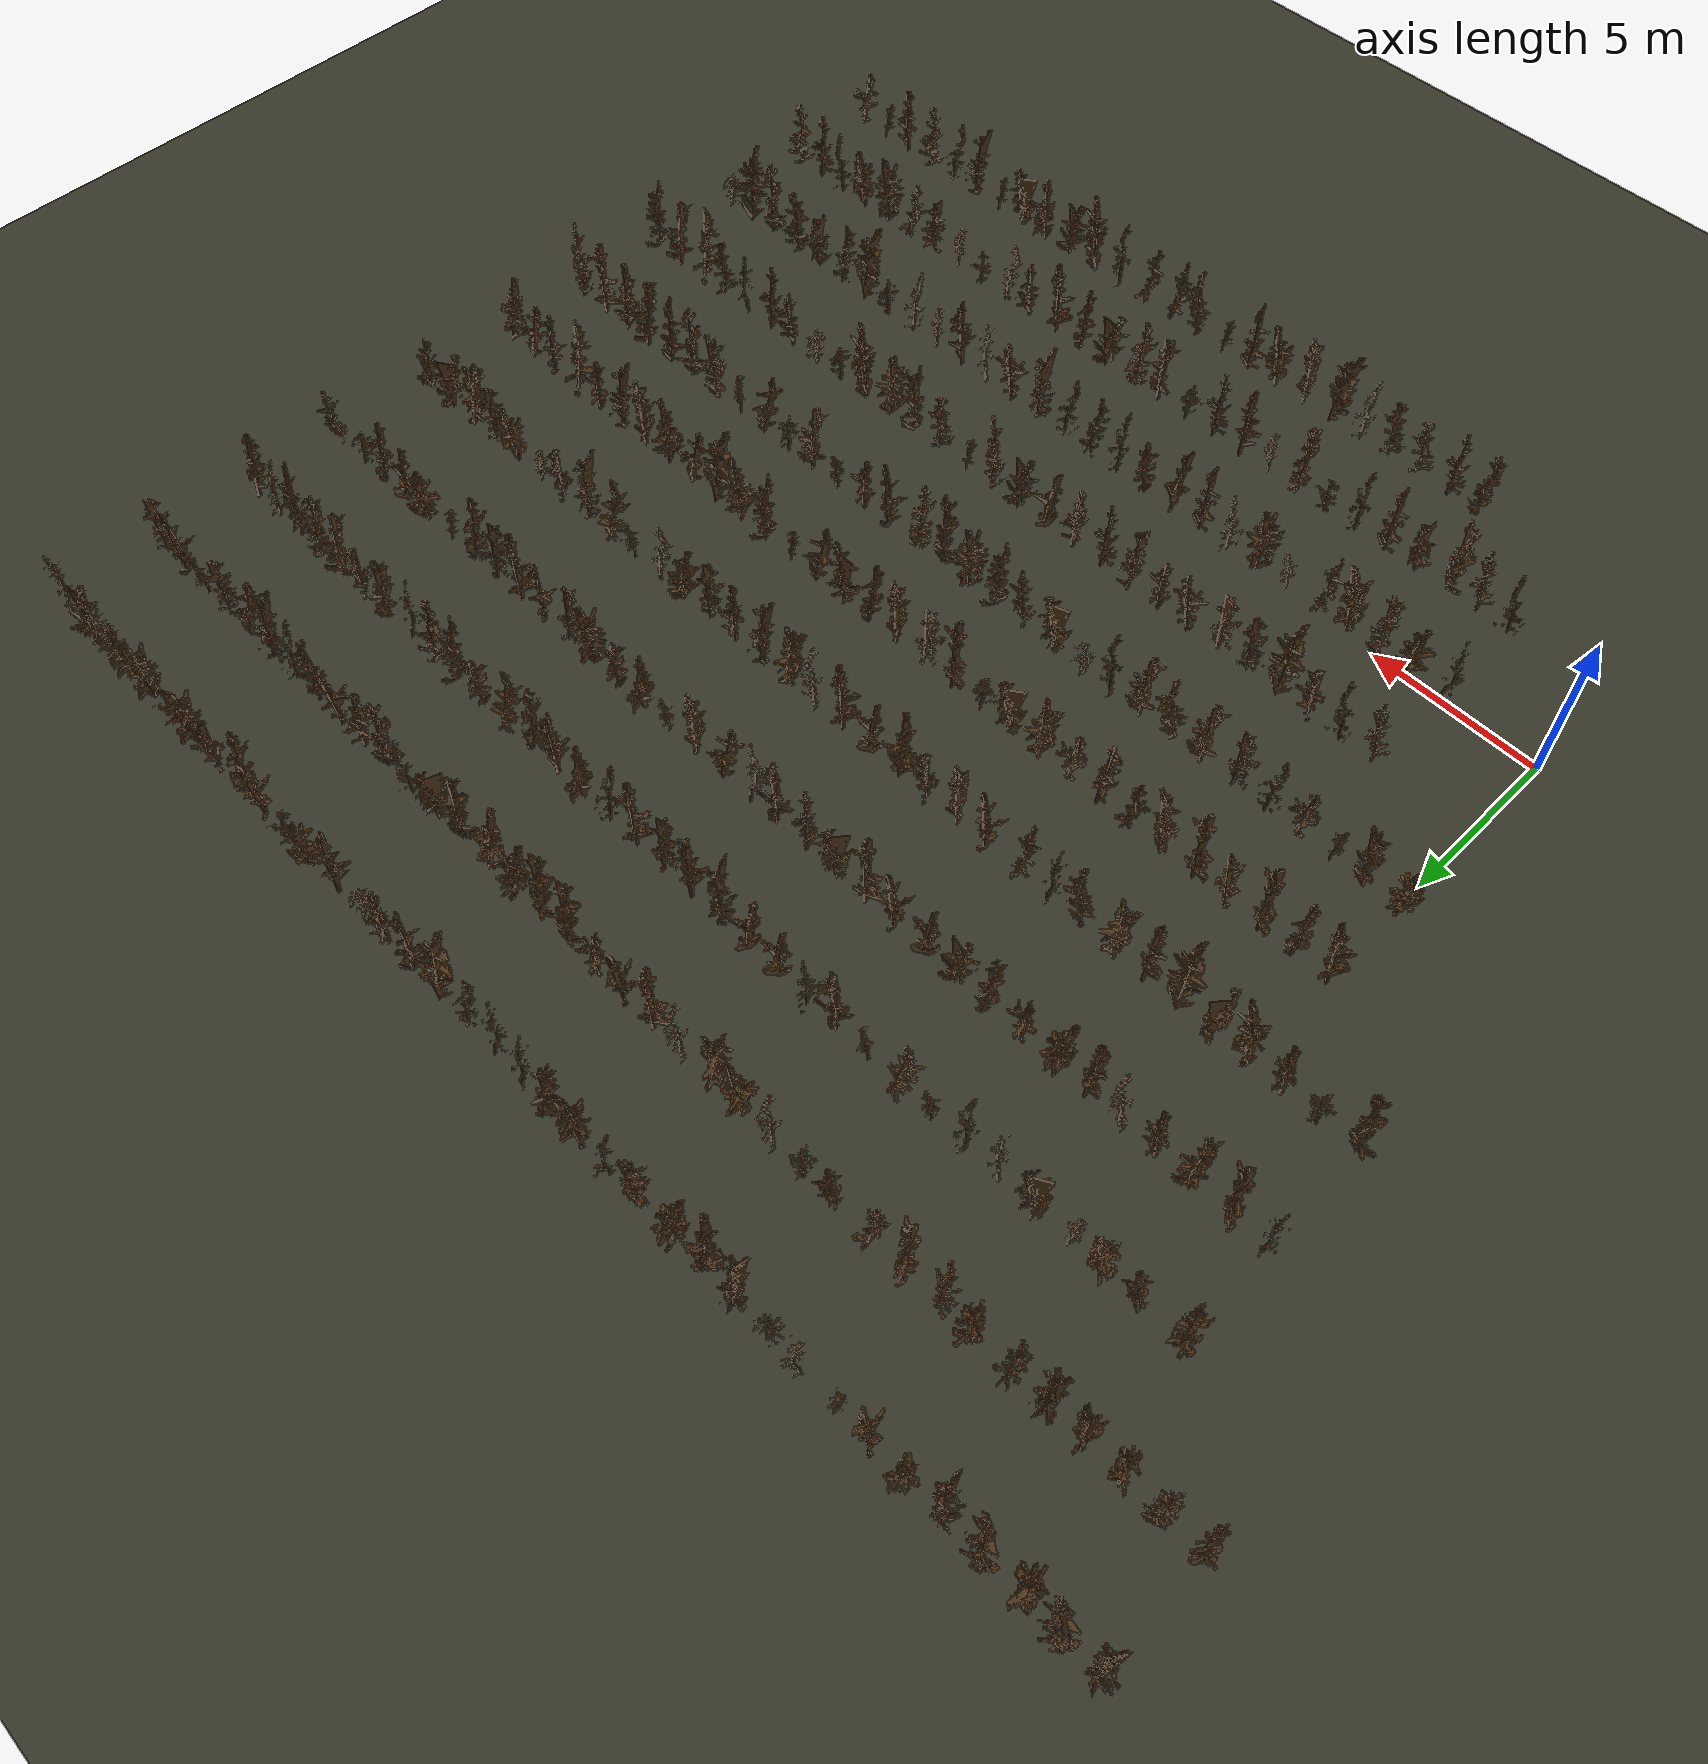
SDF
<sdf version="1.9">
 <world name="orchard_dormant_world">
  <physics name="default" type="bullet">
   <max_step_size>0.001</max_step_size>
   <real_time_factor>1.0</real_time_factor>
   <real_time_update_rate>1000</real_time_update_rate>
  </physics>
  <plugin filename="libignition-gazebo-physics-system.so" name="ignition::gazebo::systems::Physics"/>
  <plugin filename="libignition-gazebo-sensors-system.so" name="ignition::gazebo::systems::Sensors">
   <render_engine>ogre2</render_engine>
  </plugin>
  <plugin filename="libignition-gazebo-user-commands-system.so" name="ignition::gazebo::systems::UserCommands"/>
  <plugin filename="libignition-gazebo-scene-broadcaster-system.so" name="ignition::gazebo::systems::SceneBroadcaster"/>
  <light type="directional" name="sun">
   <pose>0 0 10 0 0 0</pose>
   <diffuse>0.8 0.8 0.8 1</diffuse>
   <specular>0.2 0.2 0.2 1</specular>
   <direction>-0.5 0.1 -0.9</direction>
  </light>
  <model name="ground_plane">
   <static>true</static>
   <link name="link">
    <collision name="collision">
     <geometry><plane><normal>0 0 1</normal><size>500 500</size></plane></geometry>
    </collision>
    <visual name="visual">
     <geometry><plane><normal>0 0 1</normal><size>500 500</size></plane></geometry>
     <material><ambient>0.2 0.2 0.15 1</ambient><diffuse>0.2 0.2 0.15 1</diffuse></material>
    </visual>
   </link>
  </model>
  <model name="tree1">
   <static>true</static>
   <pose>30.000 23.830 -0.1 0 0 3.291</pose>
   <link name="link">
    <collision name="collision">
     <geometry>
      <mesh>
       <uri>file:///home/administrator/ros2/orchard_navigation_rl_ws/src/orchard_worlds/models/orchard_model/tree16_collision.stl</uri>
      </mesh>
     </geometry>
    </collision>
    <visual name="visual">
     <geometry>
      <mesh>
       <uri>file:///home/administrator/ros2/orchard_navigation_rl_ws/src/orchard_worlds/models/orchard_model/tree16.stl</uri>
      </mesh>
     </geometry>
     <material><ambient>0.3 0.2 0.1 1</ambient><diffuse>0.3 0.2 0.1 1</diffuse></material>
    </visual>
   </link>
  </model>
  <model name="tree2">
   <static>true</static>
   <pose>29.000 23.830 -0.1 0 0 5.988</pose>
   <link name="link">
    <collision name="collision">
     <geometry>
      <mesh>
       <uri>file:///home/administrator/ros2/orchard_navigation_rl_ws/src/orchard_worlds/models/orchard_model/tree11_collision.stl</uri>
      </mesh>
     </geometry>
    </collision>
    <visual name="visual">
     <geometry>
      <mesh>
       <uri>file:///home/administrator/ros2/orchard_navigation_rl_ws/src/orchard_worlds/models/orchard_model/tree11.stl</uri>
      </mesh>
     </geometry>
     <material><ambient>0.3 0.2 0.1 1</ambient><diffuse>0.3 0.2 0.1 1</diffuse></material>
    </visual>
   </link>
  </model>
  <model name="tree3">
   <static>true</static>
   <pose>28.000 23.830 -0.1 0 0 3.564</pose>
   <link name="link">
    <collision name="collision">
     <geometry>
      <mesh>
       <uri>file:///home/administrator/ros2/orchard_navigation_rl_ws/src/orchard_worlds/models/orchard_model/tree10_collision.stl</uri>
      </mesh>
     </geometry>
    </collision>
    <visual name="visual">
     <geometry>
      <mesh>
       <uri>file:///home/administrator/ros2/orchard_navigation_rl_ws/src/orchard_worlds/models/orchard_model/tree10.stl</uri>
      </mesh>
     </geometry>
     <material><ambient>0.3 0.2 0.1 1</ambient><diffuse>0.3 0.2 0.1 1</diffuse></material>
    </visual>
   </link>
  </model>
  <model name="tree4">
   <static>true</static>
   <pose>27.000 23.830 -0.1 0 0 4.460</pose>
   <link name="link">
    <collision name="collision">
     <geometry>
      <mesh>
       <uri>file:///home/administrator/ros2/orchard_navigation_rl_ws/src/orchard_worlds/models/orchard_model/tree10_collision.stl</uri>
      </mesh>
     </geometry>
    </collision>
    <visual name="visual">
     <geometry>
      <mesh>
       <uri>file:///home/administrator/ros2/orchard_navigation_rl_ws/src/orchard_worlds/models/orchard_model/tree10.stl</uri>
      </mesh>
     </geometry>
     <material><ambient>0.3 0.2 0.1 1</ambient><diffuse>0.3 0.2 0.1 1</diffuse></material>
    </visual>
   </link>
  </model>
  <model name="tree5">
   <static>true</static>
   <pose>26.000 23.830 -0.1 0 0 4.465</pose>
   <link name="link">
    <collision name="collision">
     <geometry>
      <mesh>
       <uri>file:///home/administrator/ros2/orchard_navigation_rl_ws/src/orchard_worlds/models/orchard_model/tree7_collision.stl</uri>
      </mesh>
     </geometry>
    </collision>
    <visual name="visual">
     <geometry>
      <mesh>
       <uri>file:///home/administrator/ros2/orchard_navigation_rl_ws/src/orchard_worlds/models/orchard_model/tree7.stl</uri>
      </mesh>
     </geometry>
     <material><ambient>0.3 0.2 0.1 1</ambient><diffuse>0.3 0.2 0.1 1</diffuse></material>
    </visual>
   </link>
  </model>
  <model name="tree6">
   <static>true</static>
   <pose>25.000 23.830 -0.1 0 0 0.010</pose>
   <link name="link">
    <collision name="collision">
     <geometry>
      <mesh>
       <uri>file:///home/administrator/ros2/orchard_navigation_rl_ws/src/orchard_worlds/models/orchard_model/tree14_collision.stl</uri>
      </mesh>
     </geometry>
    </collision>
    <visual name="visual">
     <geometry>
      <mesh>
       <uri>file:///home/administrator/ros2/orchard_navigation_rl_ws/src/orchard_worlds/models/orchard_model/tree14.stl</uri>
      </mesh>
     </geometry>
     <material><ambient>0.3 0.2 0.1 1</ambient><diffuse>0.3 0.2 0.1 1</diffuse></material>
    </visual>
   </link>
  </model>
  <model name="tree7">
   <static>true</static>
   <pose>24.000 23.830 -0.1 0 0 4.268</pose>
   <link name="link">
    <collision name="collision">
     <geometry>
      <mesh>
       <uri>file:///home/administrator/ros2/orchard_navigation_rl_ws/src/orchard_worlds/models/orchard_model/tree7_collision.stl</uri>
      </mesh>
     </geometry>
    </collision>
    <visual name="visual">
     <geometry>
      <mesh>
       <uri>file:///home/administrator/ros2/orchard_navigation_rl_ws/src/orchard_worlds/models/orchard_model/tree7.stl</uri>
      </mesh>
     </geometry>
     <material><ambient>0.3 0.2 0.1 1</ambient><diffuse>0.3 0.2 0.1 1</diffuse></material>
    </visual>
   </link>
  </model>
  <model name="tree8">
   <static>true</static>
   <pose>23.000 23.830 -0.1 0 0 3.818</pose>
   <link name="link">
    <collision name="collision">
     <geometry>
      <mesh>
       <uri>file:///home/administrator/ros2/orchard_navigation_rl_ws/src/orchard_worlds/models/orchard_model/tree1_collision.stl</uri>
      </mesh>
     </geometry>
    </collision>
    <visual name="visual">
     <geometry>
      <mesh>
       <uri>file:///home/administrator/ros2/orchard_navigation_rl_ws/src/orchard_worlds/models/orchard_model/tree1.stl</uri>
      </mesh>
     </geometry>
     <material><ambient>0.3 0.2 0.1 1</ambient><diffuse>0.3 0.2 0.1 1</diffuse></material>
    </visual>
   </link>
  </model>
  <model name="tree9">
   <static>true</static>
   <pose>22.000 23.830 -0.1 0 0 1.025</pose>
   <link name="link">
    <collision name="collision">
     <geometry>
      <mesh>
       <uri>file:///home/administrator/ros2/orchard_navigation_rl_ws/src/orchard_worlds/models/orchard_model/tree10_collision.stl</uri>
      </mesh>
     </geometry>
    </collision>
    <visual name="visual">
     <geometry>
      <mesh>
       <uri>file:///home/administrator/ros2/orchard_navigation_rl_ws/src/orchard_worlds/models/orchard_model/tree10.stl</uri>
      </mesh>
     </geometry>
     <material><ambient>0.3 0.2 0.1 1</ambient><diffuse>0.3 0.2 0.1 1</diffuse></material>
    </visual>
   </link>
  </model>
  <model name="tree10">
   <static>true</static>
   <pose>21.000 23.830 -0.1 0 0 3.693</pose>
   <link name="link">
    <collision name="collision">
     <geometry>
      <mesh>
       <uri>file:///home/administrator/ros2/orchard_navigation_rl_ws/src/orchard_worlds/models/orchard_model/tree13_collision.stl</uri>
      </mesh>
     </geometry>
    </collision>
    <visual name="visual">
     <geometry>
      <mesh>
       <uri>file:///home/administrator/ros2/orchard_navigation_rl_ws/src/orchard_worlds/models/orchard_model/tree13.stl</uri>
      </mesh>
     </geometry>
     <material><ambient>0.3 0.2 0.1 1</ambient><diffuse>0.3 0.2 0.1 1</diffuse></material>
    </visual>
   </link>
  </model>
  <model name="tree11">
   <static>true</static>
   <pose>20.000 23.830 -0.1 0 0 0.044</pose>
   <link name="link">
    <collision name="collision">
     <geometry>
      <mesh>
       <uri>file:///home/administrator/ros2/orchard_navigation_rl_ws/src/orchard_worlds/models/orchard_model/tree14_collision.stl</uri>
      </mesh>
     </geometry>
    </collision>
    <visual name="visual">
     <geometry>
      <mesh>
       <uri>file:///home/administrator/ros2/orchard_navigation_rl_ws/src/orchard_worlds/models/orchard_model/tree14.stl</uri>
      </mesh>
     </geometry>
     <material><ambient>0.3 0.2 0.1 1</ambient><diffuse>0.3 0.2 0.1 1</diffuse></material>
    </visual>
   </link>
  </model>
  <model name="tree12">
   <static>true</static>
   <pose>19.000 23.830 -0.1 0 0 4.734</pose>
   <link name="link">
    <collision name="collision">
     <geometry>
      <mesh>
       <uri>file:///home/administrator/ros2/orchard_navigation_rl_ws/src/orchard_worlds/models/orchard_model/tree12_collision.stl</uri>
      </mesh>
     </geometry>
    </collision>
    <visual name="visual">
     <geometry>
      <mesh>
       <uri>file:///home/administrator/ros2/orchard_navigation_rl_ws/src/orchard_worlds/models/orchard_model/tree12.stl</uri>
      </mesh>
     </geometry>
     <material><ambient>0.3 0.2 0.1 1</ambient><diffuse>0.3 0.2 0.1 1</diffuse></material>
    </visual>
   </link>
  </model>
  <model name="tree13">
   <static>true</static>
   <pose>18.000 23.830 -0.1 0 0 2.517</pose>
   <link name="link">
    <collision name="collision">
     <geometry>
      <mesh>
       <uri>file:///home/administrator/ros2/orchard_navigation_rl_ws/src/orchard_worlds/models/orchard_model/tree15_collision.stl</uri>
      </mesh>
     </geometry>
    </collision>
    <visual name="visual">
     <geometry>
      <mesh>
       <uri>file:///home/administrator/ros2/orchard_navigation_rl_ws/src/orchard_worlds/models/orchard_model/tree15.stl</uri>
      </mesh>
     </geometry>
     <material><ambient>0.3 0.2 0.1 1</ambient><diffuse>0.3 0.2 0.1 1</diffuse></material>
    </visual>
   </link>
  </model>
  <model name="tree14">
   <static>true</static>
   <pose>17.000 23.830 -0.1 0 0 2.137</pose>
   <link name="link">
    <collision name="collision">
     <geometry>
      <mesh>
       <uri>file:///home/administrator/ros2/orchard_navigation_rl_ws/src/orchard_worlds/models/orchard_model/tree14_collision.stl</uri>
      </mesh>
     </geometry>
    </collision>
    <visual name="visual">
     <geometry>
      <mesh>
       <uri>file:///home/administrator/ros2/orchard_navigation_rl_ws/src/orchard_worlds/models/orchard_model/tree14.stl</uri>
      </mesh>
     </geometry>
     <material><ambient>0.3 0.2 0.1 1</ambient><diffuse>0.3 0.2 0.1 1</diffuse></material>
    </visual>
   </link>
  </model>
  <model name="tree15">
   <static>true</static>
   <pose>16.000 23.830 -0.1 0 0 5.024</pose>
   <link name="link">
    <collision name="collision">
     <geometry>
      <mesh>
       <uri>file:///home/administrator/ros2/orchard_navigation_rl_ws/src/orchard_worlds/models/orchard_model/tree15_collision.stl</uri>
      </mesh>
     </geometry>
    </collision>
    <visual name="visual">
     <geometry>
      <mesh>
       <uri>file:///home/administrator/ros2/orchard_navigation_rl_ws/src/orchard_worlds/models/orchard_model/tree15.stl</uri>
      </mesh>
     </geometry>
     <material><ambient>0.3 0.2 0.1 1</ambient><diffuse>0.3 0.2 0.1 1</diffuse></material>
    </visual>
   </link>
  </model>
  <model name="tree16">
   <static>true</static>
   <pose>15.000 23.830 -0.1 0 0 2.188</pose>
   <link name="link">
    <collision name="collision">
     <geometry>
      <mesh>
       <uri>file:///home/administrator/ros2/orchard_navigation_rl_ws/src/orchard_worlds/models/orchard_model/tree13_collision.stl</uri>
      </mesh>
     </geometry>
    </collision>
    <visual name="visual">
     <geometry>
      <mesh>
       <uri>file:///home/administrator/ros2/orchard_navigation_rl_ws/src/orchard_worlds/models/orchard_model/tree13.stl</uri>
      </mesh>
     </geometry>
     <material><ambient>0.3 0.2 0.1 1</ambient><diffuse>0.3 0.2 0.1 1</diffuse></material>
    </visual>
   </link>
  </model>
  <model name="tree17">
   <static>true</static>
   <pose>14.000 23.830 -0.1 0 0 1.109</pose>
   <link name="link">
    <collision name="collision">
     <geometry>
      <mesh>
       <uri>file:///home/administrator/ros2/orchard_navigation_rl_ws/src/orchard_worlds/models/orchard_model/tree7_collision.stl</uri>
      </mesh>
     </geometry>
    </collision>
    <visual name="visual">
     <geometry>
      <mesh>
       <uri>file:///home/administrator/ros2/orchard_navigation_rl_ws/src/orchard_worlds/models/orchard_model/tree7.stl</uri>
      </mesh>
     </geometry>
     <material><ambient>0.3 0.2 0.1 1</ambient><diffuse>0.3 0.2 0.1 1</diffuse></material>
    </visual>
   </link>
  </model>
  <model name="tree18">
   <static>true</static>
   <pose>13.000 23.830 -0.1 0 0 5.993</pose>
   <link name="link">
    <collision name="collision">
     <geometry>
      <mesh>
       <uri>file:///home/administrator/ros2/orchard_navigation_rl_ws/src/orchard_worlds/models/orchard_model/tree9_collision.stl</uri>
      </mesh>
     </geometry>
    </collision>
    <visual name="visual">
     <geometry>
      <mesh>
       <uri>file:///home/administrator/ros2/orchard_navigation_rl_ws/src/orchard_worlds/models/orchard_model/tree9.stl</uri>
      </mesh>
     </geometry>
     <material><ambient>0.3 0.2 0.1 1</ambient><diffuse>0.3 0.2 0.1 1</diffuse></material>
    </visual>
   </link>
  </model>
  <model name="tree19">
   <static>true</static>
   <pose>12.000 23.830 -0.1 0 0 1.425</pose>
   <link name="link">
    <collision name="collision">
     <geometry>
      <mesh>
       <uri>file:///home/administrator/ros2/orchard_navigation_rl_ws/src/orchard_worlds/models/orchard_model/tree16_collision.stl</uri>
      </mesh>
     </geometry>
    </collision>
    <visual name="visual">
     <geometry>
      <mesh>
       <uri>file:///home/administrator/ros2/orchard_navigation_rl_ws/src/orchard_worlds/models/orchard_model/tree16.stl</uri>
      </mesh>
     </geometry>
     <material><ambient>0.3 0.2 0.1 1</ambient><diffuse>0.3 0.2 0.1 1</diffuse></material>
    </visual>
   </link>
  </model>
  <model name="tree20">
   <static>true</static>
   <pose>11.000 23.830 -0.1 0 0 0.603</pose>
   <link name="link">
    <collision name="collision">
     <geometry>
      <mesh>
       <uri>file:///home/administrator/ros2/orchard_navigation_rl_ws/src/orchard_worlds/models/orchard_model/tree16_collision.stl</uri>
      </mesh>
     </geometry>
    </collision>
    <visual name="visual">
     <geometry>
      <mesh>
       <uri>file:///home/administrator/ros2/orchard_navigation_rl_ws/src/orchard_worlds/models/orchard_model/tree16.stl</uri>
      </mesh>
     </geometry>
     <material><ambient>0.3 0.2 0.1 1</ambient><diffuse>0.3 0.2 0.1 1</diffuse></material>
    </visual>
   </link>
  </model>
  <model name="tree21">
   <static>true</static>
   <pose>10.000 23.830 -0.1 0 0 4.419</pose>
   <link name="link">
    <collision name="collision">
     <geometry>
      <mesh>
       <uri>file:///home/administrator/ros2/orchard_navigation_rl_ws/src/orchard_worlds/models/orchard_model/tree5_collision.stl</uri>
      </mesh>
     </geometry>
    </collision>
    <visual name="visual">
     <geometry>
      <mesh>
       <uri>file:///home/administrator/ros2/orchard_navigation_rl_ws/src/orchard_worlds/models/orchard_model/tree5.stl</uri>
      </mesh>
     </geometry>
     <material><ambient>0.3 0.2 0.1 1</ambient><diffuse>0.3 0.2 0.1 1</diffuse></material>
    </visual>
   </link>
  </model>
  <model name="tree22">
   <static>true</static>
   <pose>9.000 23.830 -0.1 0 0 3.785</pose>
   <link name="link">
    <collision name="collision">
     <geometry>
      <mesh>
       <uri>file:///home/administrator/ros2/orchard_navigation_rl_ws/src/orchard_worlds/models/orchard_model/tree7_collision.stl</uri>
      </mesh>
     </geometry>
    </collision>
    <visual name="visual">
     <geometry>
      <mesh>
       <uri>file:///home/administrator/ros2/orchard_navigation_rl_ws/src/orchard_worlds/models/orchard_model/tree7.stl</uri>
      </mesh>
     </geometry>
     <material><ambient>0.3 0.2 0.1 1</ambient><diffuse>0.3 0.2 0.1 1</diffuse></material>
    </visual>
   </link>
  </model>
  <model name="tree23">
   <static>true</static>
   <pose>8.000 23.830 -0.1 0 0 5.769</pose>
   <link name="link">
    <collision name="collision">
     <geometry>
      <mesh>
       <uri>file:///home/administrator/ros2/orchard_navigation_rl_ws/src/orchard_worlds/models/orchard_model/tree16_collision.stl</uri>
      </mesh>
     </geometry>
    </collision>
    <visual name="visual">
     <geometry>
      <mesh>
       <uri>file:///home/administrator/ros2/orchard_navigation_rl_ws/src/orchard_worlds/models/orchard_model/tree16.stl</uri>
      </mesh>
     </geometry>
     <material><ambient>0.3 0.2 0.1 1</ambient><diffuse>0.3 0.2 0.1 1</diffuse></material>
    </visual>
   </link>
  </model>
  <model name="tree24">
   <static>true</static>
   <pose>7.000 23.830 -0.1 0 0 3.286</pose>
   <link name="link">
    <collision name="collision">
     <geometry>
      <mesh>
       <uri>file:///home/administrator/ros2/orchard_navigation_rl_ws/src/orchard_worlds/models/orchard_model/tree5_collision.stl</uri>
      </mesh>
     </geometry>
    </collision>
    <visual name="visual">
     <geometry>
      <mesh>
       <uri>file:///home/administrator/ros2/orchard_navigation_rl_ws/src/orchard_worlds/models/orchard_model/tree5.stl</uri>
      </mesh>
     </geometry>
     <material><ambient>0.3 0.2 0.1 1</ambient><diffuse>0.3 0.2 0.1 1</diffuse></material>
    </visual>
   </link>
  </model>
  <model name="tree25">
   <static>true</static>
   <pose>6.000 23.830 -0.1 0 0 6.239</pose>
   <link name="link">
    <collision name="collision">
     <geometry>
      <mesh>
       <uri>file:///home/administrator/ros2/orchard_navigation_rl_ws/src/orchard_worlds/models/orchard_model/tree12_collision.stl</uri>
      </mesh>
     </geometry>
    </collision>
    <visual name="visual">
     <geometry>
      <mesh>
       <uri>file:///home/administrator/ros2/orchard_navigation_rl_ws/src/orchard_worlds/models/orchard_model/tree12.stl</uri>
      </mesh>
     </geometry>
     <material><ambient>0.3 0.2 0.1 1</ambient><diffuse>0.3 0.2 0.1 1</diffuse></material>
    </visual>
   </link>
  </model>
  <model name="tree26">
   <static>true</static>
   <pose>5.000 23.830 -0.1 0 0 1.590</pose>
   <link name="link">
    <collision name="collision">
     <geometry>
      <mesh>
       <uri>file:///home/administrator/ros2/orchard_navigation_rl_ws/src/orchard_worlds/models/orchard_model/tree12_collision.stl</uri>
      </mesh>
     </geometry>
    </collision>
    <visual name="visual">
     <geometry>
      <mesh>
       <uri>file:///home/administrator/ros2/orchard_navigation_rl_ws/src/orchard_worlds/models/orchard_model/tree12.stl</uri>
      </mesh>
     </geometry>
     <material><ambient>0.3 0.2 0.1 1</ambient><diffuse>0.3 0.2 0.1 1</diffuse></material>
    </visual>
   </link>
  </model>
  <model name="tree27">
   <static>true</static>
   <pose>4.000 23.830 -0.1 0 0 6.030</pose>
   <link name="link">
    <collision name="collision">
     <geometry>
      <mesh>
       <uri>file:///home/administrator/ros2/orchard_navigation_rl_ws/src/orchard_worlds/models/orchard_model/tree5_collision.stl</uri>
      </mesh>
     </geometry>
    </collision>
    <visual name="visual">
     <geometry>
      <mesh>
       <uri>file:///home/administrator/ros2/orchard_navigation_rl_ws/src/orchard_worlds/models/orchard_model/tree5.stl</uri>
      </mesh>
     </geometry>
     <material><ambient>0.3 0.2 0.1 1</ambient><diffuse>0.3 0.2 0.1 1</diffuse></material>
    </visual>
   </link>
  </model>
  <model name="tree28">
   <static>true</static>
   <pose>3.000 23.830 -0.1 0 0 1.479</pose>
   <link name="link">
    <collision name="collision">
     <geometry>
      <mesh>
       <uri>file:///home/administrator/ros2/orchard_navigation_rl_ws/src/orchard_worlds/models/orchard_model/tree14_collision.stl</uri>
      </mesh>
     </geometry>
    </collision>
    <visual name="visual">
     <geometry>
      <mesh>
       <uri>file:///home/administrator/ros2/orchard_navigation_rl_ws/src/orchard_worlds/models/orchard_model/tree14.stl</uri>
      </mesh>
     </geometry>
     <material><ambient>0.3 0.2 0.1 1</ambient><diffuse>0.3 0.2 0.1 1</diffuse></material>
    </visual>
   </link>
  </model>
  <model name="tree29">
   <static>true</static>
   <pose>2.000 23.830 -0.1 0 0 5.065</pose>
   <link name="link">
    <collision name="collision">
     <geometry>
      <mesh>
       <uri>file:///home/administrator/ros2/orchard_navigation_rl_ws/src/orchard_worlds/models/orchard_model/tree16_collision.stl</uri>
      </mesh>
     </geometry>
    </collision>
    <visual name="visual">
     <geometry>
      <mesh>
       <uri>file:///home/administrator/ros2/orchard_navigation_rl_ws/src/orchard_worlds/models/orchard_model/tree16.stl</uri>
      </mesh>
     </geometry>
     <material><ambient>0.3 0.2 0.1 1</ambient><diffuse>0.3 0.2 0.1 1</diffuse></material>
    </visual>
   </link>
  </model>
  <model name="tree30">
   <static>true</static>
   <pose>1.000 23.830 -0.1 0 0 5.503</pose>
   <link name="link">
    <collision name="collision">
     <geometry>
      <mesh>
       <uri>file:///home/administrator/ros2/orchard_navigation_rl_ws/src/orchard_worlds/models/orchard_model/tree4_collision.stl</uri>
      </mesh>
     </geometry>
    </collision>
    <visual name="visual">
     <geometry>
      <mesh>
       <uri>file:///home/administrator/ros2/orchard_navigation_rl_ws/src/orchard_worlds/models/orchard_model/tree4.stl</uri>
      </mesh>
     </geometry>
     <material><ambient>0.3 0.2 0.1 1</ambient><diffuse>0.3 0.2 0.1 1</diffuse></material>
    </visual>
   </link>
  </model>
  <model name="tree31">
   <static>true</static>
   <pose>0.000 23.830 -0.1 0 0 3.590</pose>
   <link name="link">
    <collision name="collision">
     <geometry>
      <mesh>
       <uri>file:///home/administrator/ros2/orchard_navigation_rl_ws/src/orchard_worlds/models/orchard_model/tree13_collision.stl</uri>
      </mesh>
     </geometry>
    </collision>
    <visual name="visual">
     <geometry>
      <mesh>
       <uri>file:///home/administrator/ros2/orchard_navigation_rl_ws/src/orchard_worlds/models/orchard_model/tree13.stl</uri>
      </mesh>
     </geometry>
     <material><ambient>0.3 0.2 0.1 1</ambient><diffuse>0.3 0.2 0.1 1</diffuse></material>
    </visual>
   </link>
  </model>
  <model name="tree32">
   <static>true</static>
   <pose>-1.000 23.830 -0.1 0 0 4.396</pose>
   <link name="link">
    <collision name="collision">
     <geometry>
      <mesh>
       <uri>file:///home/administrator/ros2/orchard_navigation_rl_ws/src/orchard_worlds/models/orchard_model/tree10_collision.stl</uri>
      </mesh>
     </geometry>
    </collision>
    <visual name="visual">
     <geometry>
      <mesh>
       <uri>file:///home/administrator/ros2/orchard_navigation_rl_ws/src/orchard_worlds/models/orchard_model/tree10.stl</uri>
      </mesh>
     </geometry>
     <material><ambient>0.3 0.2 0.1 1</ambient><diffuse>0.3 0.2 0.1 1</diffuse></material>
    </visual>
   </link>
  </model>
  <model name="tree33">
   <static>true</static>
   <pose>-2.000 23.830 -0.1 0 0 0.554</pose>
   <link name="link">
    <collision name="collision">
     <geometry>
      <mesh>
       <uri>file:///home/administrator/ros2/orchard_navigation_rl_ws/src/orchard_worlds/models/orchard_model/tree5_collision.stl</uri>
      </mesh>
     </geometry>
    </collision>
    <visual name="visual">
     <geometry>
      <mesh>
       <uri>file:///home/administrator/ros2/orchard_navigation_rl_ws/src/orchard_worlds/models/orchard_model/tree5.stl</uri>
      </mesh>
     </geometry>
     <material><ambient>0.3 0.2 0.1 1</ambient><diffuse>0.3 0.2 0.1 1</diffuse></material>
    </visual>
   </link>
  </model>
  <model name="tree34">
   <static>true</static>
   <pose>-3.000 23.830 -0.1 0 0 1.792</pose>
   <link name="link">
    <collision name="collision">
     <geometry>
      <mesh>
       <uri>file:///home/administrator/ros2/orchard_navigation_rl_ws/src/orchard_worlds/models/orchard_model/tree11_collision.stl</uri>
      </mesh>
     </geometry>
    </collision>
    <visual name="visual">
     <geometry>
      <mesh>
       <uri>file:///home/administrator/ros2/orchard_navigation_rl_ws/src/orchard_worlds/models/orchard_model/tree11.stl</uri>
      </mesh>
     </geometry>
     <material><ambient>0.3 0.2 0.1 1</ambient><diffuse>0.3 0.2 0.1 1</diffuse></material>
    </visual>
   </link>
  </model>
  <model name="tree35">
   <static>true</static>
   <pose>-4.000 23.830 -0.1 0 0 5.510</pose>
   <link name="link">
    <collision name="collision">
     <geometry>
      <mesh>
       <uri>file:///home/administrator/ros2/orchard_navigation_rl_ws/src/orchard_worlds/models/orchard_model/tree7_collision.stl</uri>
      </mesh>
     </geometry>
    </collision>
    <visual name="visual">
     <geometry>
      <mesh>
       <uri>file:///home/administrator/ros2/orchard_navigation_rl_ws/src/orchard_worlds/models/orchard_model/tree7.stl</uri>
      </mesh>
     </geometry>
     <material><ambient>0.3 0.2 0.1 1</ambient><diffuse>0.3 0.2 0.1 1</diffuse></material>
    </visual>
   </link>
  </model>
  <model name="tree36">
   <static>true</static>
   <pose>-5.000 23.830 -0.1 0 0 2.146</pose>
   <link name="link">
    <collision name="collision">
     <geometry>
      <mesh>
       <uri>file:///home/administrator/ros2/orchard_navigation_rl_ws/src/orchard_worlds/models/orchard_model/tree11_collision.stl</uri>
      </mesh>
     </geometry>
    </collision>
    <visual name="visual">
     <geometry>
      <mesh>
       <uri>file:///home/administrator/ros2/orchard_navigation_rl_ws/src/orchard_worlds/models/orchard_model/tree11.stl</uri>
      </mesh>
     </geometry>
     <material><ambient>0.3 0.2 0.1 1</ambient><diffuse>0.3 0.2 0.1 1</diffuse></material>
    </visual>
   </link>
  </model>
  <model name="tree37">
   <static>true</static>
   <pose>-6.000 23.830 -0.1 0 0 6.051</pose>
   <link name="link">
    <collision name="collision">
     <geometry>
      <mesh>
       <uri>file:///home/administrator/ros2/orchard_navigation_rl_ws/src/orchard_worlds/models/orchard_model/tree5_collision.stl</uri>
      </mesh>
     </geometry>
    </collision>
    <visual name="visual">
     <geometry>
      <mesh>
       <uri>file:///home/administrator/ros2/orchard_navigation_rl_ws/src/orchard_worlds/models/orchard_model/tree5.stl</uri>
      </mesh>
     </geometry>
     <material><ambient>0.3 0.2 0.1 1</ambient><diffuse>0.3 0.2 0.1 1</diffuse></material>
    </visual>
   </link>
  </model>
  <model name="tree38">
   <static>true</static>
   <pose>30.000 20.800 -0.1 0 0 1.785</pose>
   <link name="link">
    <collision name="collision">
     <geometry>
      <mesh>
       <uri>file:///home/administrator/ros2/orchard_navigation_rl_ws/src/orchard_worlds/models/orchard_model/tree1_collision.stl</uri>
      </mesh>
     </geometry>
    </collision>
    <visual name="visual">
     <geometry>
      <mesh>
       <uri>file:///home/administrator/ros2/orchard_navigation_rl_ws/src/orchard_worlds/models/orchard_model/tree1.stl</uri>
      </mesh>
     </geometry>
     <material><ambient>0.3 0.2 0.1 1</ambient><diffuse>0.3 0.2 0.1 1</diffuse></material>
    </visual>
   </link>
  </model>
  <model name="tree39">
   <static>true</static>
   <pose>29.000 20.800 -0.1 0 0 3.248</pose>
   <link name="link">
    <collision name="collision">
     <geometry>
      <mesh>
       <uri>file:///home/administrator/ros2/orchard_navigation_rl_ws/src/orchard_worlds/models/orchard_model/tree13_collision.stl</uri>
      </mesh>
     </geometry>
    </collision>
    <visual name="visual">
     <geometry>
      <mesh>
       <uri>file:///home/administrator/ros2/orchard_navigation_rl_ws/src/orchard_worlds/models/orchard_model/tree13.stl</uri>
      </mesh>
     </geometry>
     <material><ambient>0.3 0.2 0.1 1</ambient><diffuse>0.3 0.2 0.1 1</diffuse></material>
    </visual>
   </link>
  </model>
  <model name="tree40">
   <static>true</static>
   <pose>28.000 20.800 -0.1 0 0 3.781</pose>
   <link name="link">
    <collision name="collision">
     <geometry>
      <mesh>
       <uri>file:///home/administrator/ros2/orchard_navigation_rl_ws/src/orchard_worlds/models/orchard_model/tree4_collision.stl</uri>
      </mesh>
     </geometry>
    </collision>
    <visual name="visual">
     <geometry>
      <mesh>
       <uri>file:///home/administrator/ros2/orchard_navigation_rl_ws/src/orchard_worlds/models/orchard_model/tree4.stl</uri>
      </mesh>
     </geometry>
     <material><ambient>0.3 0.2 0.1 1</ambient><diffuse>0.3 0.2 0.1 1</diffuse></material>
    </visual>
   </link>
  </model>
  <model name="tree41">
   <static>true</static>
   <pose>27.000 20.800 -0.1 0 0 1.872</pose>
   <link name="link">
    <collision name="collision">
     <geometry>
      <mesh>
       <uri>file:///home/administrator/ros2/orchard_navigation_rl_ws/src/orchard_worlds/models/orchard_model/tree1_collision.stl</uri>
      </mesh>
     </geometry>
    </collision>
    <visual name="visual">
     <geometry>
      <mesh>
       <uri>file:///home/administrator/ros2/orchard_navigation_rl_ws/src/orchard_worlds/models/orchard_model/tree1.stl</uri>
      </mesh>
     </geometry>
     <material><ambient>0.3 0.2 0.1 1</ambient><diffuse>0.3 0.2 0.1 1</diffuse></material>
    </visual>
   </link>
  </model>
  <model name="tree42">
   <static>true</static>
   <pose>26.000 20.800 -0.1 0 0 0.175</pose>
   <link name="link">
    <collision name="collision">
     <geometry>
      <mesh>
       <uri>file:///home/administrator/ros2/orchard_navigation_rl_ws/src/orchard_worlds/models/orchard_model/tree8_collision.stl</uri>
      </mesh>
     </geometry>
    </collision>
    <visual name="visual">
     <geometry>
      <mesh>
       <uri>file:///home/administrator/ros2/orchard_navigation_rl_ws/src/orchard_worlds/models/orchard_model/tree8.stl</uri>
      </mesh>
     </geometry>
     <material><ambient>0.3 0.2 0.1 1</ambient><diffuse>0.3 0.2 0.1 1</diffuse></material>
    </visual>
   </link>
  </model>
  <model name="tree43">
   <static>true</static>
   <pose>25.000 20.800 -0.1 0 0 6.215</pose>
   <link name="link">
    <collision name="collision">
     <geometry>
      <mesh>
       <uri>file:///home/administrator/ros2/orchard_navigation_rl_ws/src/orchard_worlds/models/orchard_model/tree5_collision.stl</uri>
      </mesh>
     </geometry>
    </collision>
    <visual name="visual">
     <geometry>
      <mesh>
       <uri>file:///home/administrator/ros2/orchard_navigation_rl_ws/src/orchard_worlds/models/orchard_model/tree5.stl</uri>
      </mesh>
     </geometry>
     <material><ambient>0.3 0.2 0.1 1</ambient><diffuse>0.3 0.2 0.1 1</diffuse></material>
    </visual>
   </link>
  </model>
  <model name="tree44">
   <static>true</static>
   <pose>24.000 20.800 -0.1 0 0 1.127</pose>
   <link name="link">
    <collision name="collision">
     <geometry>
      <mesh>
       <uri>file:///home/administrator/ros2/orchard_navigation_rl_ws/src/orchard_worlds/models/orchard_model/tree9_collision.stl</uri>
      </mesh>
     </geometry>
    </collision>
    <visual name="visual">
     <geometry>
      <mesh>
       <uri>file:///home/administrator/ros2/orchard_navigation_rl_ws/src/orchard_worlds/models/orchard_model/tree9.stl</uri>
      </mesh>
     </geometry>
     <material><ambient>0.3 0.2 0.1 1</ambient><diffuse>0.3 0.2 0.1 1</diffuse></material>
    </visual>
   </link>
  </model>
  <model name="tree45">
   <static>true</static>
   <pose>23.000 20.800 -0.1 0 0 2.285</pose>
   <link name="link">
    <collision name="collision">
     <geometry>
      <mesh>
       <uri>file:///home/administrator/ros2/orchard_navigation_rl_ws/src/orchard_worlds/models/orchard_model/tree10_collision.stl</uri>
      </mesh>
     </geometry>
    </collision>
    <visual name="visual">
     <geometry>
      <mesh>
       <uri>file:///home/administrator/ros2/orchard_navigation_rl_ws/src/orchard_worlds/models/orchard_model/tree10.stl</uri>
      </mesh>
     </geometry>
     <material><ambient>0.3 0.2 0.1 1</ambient><diffuse>0.3 0.2 0.1 1</diffuse></material>
    </visual>
   </link>
  </model>
  <model name="tree46">
   <static>true</static>
   <pose>22.000 20.800 -0.1 0 0 2.798</pose>
   <link name="link">
    <collision name="collision">
     <geometry>
      <mesh>
       <uri>file:///home/administrator/ros2/orchard_navigation_rl_ws/src/orchard_worlds/models/orchard_model/tree8_collision.stl</uri>
      </mesh>
     </geometry>
    </collision>
    <visual name="visual">
     <geometry>
      <mesh>
       <uri>file:///home/administrator/ros2/orchard_navigation_rl_ws/src/orchard_worlds/models/orchard_model/tree8.stl</uri>
      </mesh>
     </geometry>
     <material><ambient>0.3 0.2 0.1 1</ambient><diffuse>0.3 0.2 0.1 1</diffuse></material>
    </visual>
   </link>
  </model>
  <model name="tree47">
   <static>true</static>
   <pose>21.000 20.800 -0.1 0 0 5.839</pose>
   <link name="link">
    <collision name="collision">
     <geometry>
      <mesh>
       <uri>file:///home/administrator/ros2/orchard_navigation_rl_ws/src/orchard_worlds/models/orchard_model/tree15_collision.stl</uri>
      </mesh>
     </geometry>
    </collision>
    <visual name="visual">
     <geometry>
      <mesh>
       <uri>file:///home/administrator/ros2/orchard_navigation_rl_ws/src/orchard_worlds/models/orchard_model/tree15.stl</uri>
      </mesh>
     </geometry>
     <material><ambient>0.3 0.2 0.1 1</ambient><diffuse>0.3 0.2 0.1 1</diffuse></material>
    </visual>
   </link>
  </model>
  <model name="tree48">
   <static>true</static>
   <pose>20.000 20.800 -0.1 0 0 1.792</pose>
   <link name="link">
    <collision name="collision">
     <geometry>
      <mesh>
       <uri>file:///home/administrator/ros2/orchard_navigation_rl_ws/src/orchard_worlds/models/orchard_model/tree3_collision.stl</uri>
      </mesh>
     </geometry>
    </collision>
    <visual name="visual">
     <geometry>
      <mesh>
       <uri>file:///home/administrator/ros2/orchard_navigation_rl_ws/src/orchard_worlds/models/orchard_model/tree3.stl</uri>
      </mesh>
     </geometry>
     <material><ambient>0.3 0.2 0.1 1</ambient><diffuse>0.3 0.2 0.1 1</diffuse></material>
    </visual>
   </link>
  </model>
  <model name="tree49">
   <static>true</static>
   <pose>19.000 20.800 -0.1 0 0 2.987</pose>
   <link name="link">
    <collision name="collision">
     <geometry>
      <mesh>
       <uri>file:///home/administrator/ros2/orchard_navigation_rl_ws/src/orchard_worlds/models/orchard_model/tree9_collision.stl</uri>
      </mesh>
     </geometry>
    </collision>
    <visual name="visual">
     <geometry>
      <mesh>
       <uri>file:///home/administrator/ros2/orchard_navigation_rl_ws/src/orchard_worlds/models/orchard_model/tree9.stl</uri>
      </mesh>
     </geometry>
     <material><ambient>0.3 0.2 0.1 1</ambient><diffuse>0.3 0.2 0.1 1</diffuse></material>
    </visual>
   </link>
  </model>
  <model name="tree50">
   <static>true</static>
   <pose>18.000 20.800 -0.1 0 0 3.843</pose>
   <link name="link">
    <collision name="collision">
     <geometry>
      <mesh>
       <uri>file:///home/administrator/ros2/orchard_navigation_rl_ws/src/orchard_worlds/models/orchard_model/tree11_collision.stl</uri>
      </mesh>
     </geometry>
    </collision>
    <visual name="visual">
     <geometry>
      <mesh>
       <uri>file:///home/administrator/ros2/orchard_navigation_rl_ws/src/orchard_worlds/models/orchard_model/tree11.stl</uri>
      </mesh>
     </geometry>
     <material><ambient>0.3 0.2 0.1 1</ambient><diffuse>0.3 0.2 0.1 1</diffuse></material>
    </visual>
   </link>
  </model>
  <model name="tree51">
   <static>true</static>
   <pose>17.000 20.800 -0.1 0 0 1.557</pose>
   <link name="link">
    <collision name="collision">
     <geometry>
      <mesh>
       <uri>file:///home/administrator/ros2/orchard_navigation_rl_ws/src/orchard_worlds/models/orchard_model/tree3_collision.stl</uri>
      </mesh>
     </geometry>
    </collision>
    <visual name="visual">
     <geometry>
      <mesh>
       <uri>file:///home/administrator/ros2/orchard_navigation_rl_ws/src/orchard_worlds/models/orchard_model/tree3.stl</uri>
      </mesh>
     </geometry>
     <material><ambient>0.3 0.2 0.1 1</ambient><diffuse>0.3 0.2 0.1 1</diffuse></material>
    </visual>
   </link>
  </model>
  <model name="tree52">
   <static>true</static>
   <pose>16.000 20.800 -0.1 0 0 1.061</pose>
   <link name="link">
    <collision name="collision">
     <geometry>
      <mesh>
       <uri>file:///home/administrator/ros2/orchard_navigation_rl_ws/src/orchard_worlds/models/orchard_model/tree12_collision.stl</uri>
      </mesh>
     </geometry>
    </collision>
    <visual name="visual">
     <geometry>
      <mesh>
       <uri>file:///home/administrator/ros2/orchard_navigation_rl_ws/src/orchard_worlds/models/orchard_model/tree12.stl</uri>
      </mesh>
     </geometry>
     <material><ambient>0.3 0.2 0.1 1</ambient><diffuse>0.3 0.2 0.1 1</diffuse></material>
    </visual>
   </link>
  </model>
  <model name="tree53">
   <static>true</static>
   <pose>15.000 20.800 -0.1 0 0 0.024</pose>
   <link name="link">
    <collision name="collision">
     <geometry>
      <mesh>
       <uri>file:///home/administrator/ros2/orchard_navigation_rl_ws/src/orchard_worlds/models/orchard_model/tree12_collision.stl</uri>
      </mesh>
     </geometry>
    </collision>
    <visual name="visual">
     <geometry>
      <mesh>
       <uri>file:///home/administrator/ros2/orchard_navigation_rl_ws/src/orchard_worlds/models/orchard_model/tree12.stl</uri>
      </mesh>
     </geometry>
     <material><ambient>0.3 0.2 0.1 1</ambient><diffuse>0.3 0.2 0.1 1</diffuse></material>
    </visual>
   </link>
  </model>
  <model name="tree54">
   <static>true</static>
   <pose>14.000 20.800 -0.1 0 0 0.943</pose>
   <link name="link">
    <collision name="collision">
     <geometry>
      <mesh>
       <uri>file:///home/administrator/ros2/orchard_navigation_rl_ws/src/orchard_worlds/models/orchard_model/tree3_collision.stl</uri>
      </mesh>
     </geometry>
    </collision>
    <visual name="visual">
     <geometry>
      <mesh>
       <uri>file:///home/administrator/ros2/orchard_navigation_rl_ws/src/orchard_worlds/models/orchard_model/tree3.stl</uri>
      </mesh>
     </geometry>
     <material><ambient>0.3 0.2 0.1 1</ambient><diffuse>0.3 0.2 0.1 1</diffuse></material>
    </visual>
   </link>
  </model>
  <model name="tree55">
   <static>true</static>
   <pose>13.000 20.800 -0.1 0 0 1.076</pose>
   <link name="link">
    <collision name="collision">
     <geometry>
      <mesh>
       <uri>file:///home/administrator/ros2/orchard_navigation_rl_ws/src/orchard_worlds/models/orchard_model/tree3_collision.stl</uri>
      </mesh>
     </geometry>
    </collision>
    <visual name="visual">
     <geometry>
      <mesh>
       <uri>file:///home/administrator/ros2/orchard_navigation_rl_ws/src/orchard_worlds/models/orchard_model/tree3.stl</uri>
      </mesh>
     </geometry>
     <material><ambient>0.3 0.2 0.1 1</ambient><diffuse>0.3 0.2 0.1 1</diffuse></material>
    </visual>
   </link>
  </model>
  <model name="tree56">
   <static>true</static>
   <pose>12.000 20.800 -0.1 0 0 5.086</pose>
   <link name="link">
    <collision name="collision">
     <geometry>
      <mesh>
       <uri>file:///home/administrator/ros2/orchard_navigation_rl_ws/src/orchard_worlds/models/orchard_model/tree8_collision.stl</uri>
      </mesh>
     </geometry>
    </collision>
    <visual name="visual">
     <geometry>
      <mesh>
       <uri>file:///home/administrator/ros2/orchard_navigation_rl_ws/src/orchard_worlds/models/orchard_model/tree8.stl</uri>
      </mesh>
     </geometry>
     <material><ambient>0.3 0.2 0.1 1</ambient><diffuse>0.3 0.2 0.1 1</diffuse></material>
    </visual>
   </link>
  </model>
  <model name="tree57">
   <static>true</static>
   <pose>11.000 20.800 -0.1 0 0 3.767</pose>
   <link name="link">
    <collision name="collision">
     <geometry>
      <mesh>
       <uri>file:///home/administrator/ros2/orchard_navigation_rl_ws/src/orchard_worlds/models/orchard_model/tree13_collision.stl</uri>
      </mesh>
     </geometry>
    </collision>
    <visual name="visual">
     <geometry>
      <mesh>
       <uri>file:///home/administrator/ros2/orchard_navigation_rl_ws/src/orchard_worlds/models/orchard_model/tree13.stl</uri>
      </mesh>
     </geometry>
     <material><ambient>0.3 0.2 0.1 1</ambient><diffuse>0.3 0.2 0.1 1</diffuse></material>
    </visual>
   </link>
  </model>
  <model name="tree58">
   <static>true</static>
   <pose>10.000 20.800 -0.1 0 0 2.060</pose>
   <link name="link">
    <collision name="collision">
     <geometry>
      <mesh>
       <uri>file:///home/administrator/ros2/orchard_navigation_rl_ws/src/orchard_worlds/models/orchard_model/tree6_collision.stl</uri>
      </mesh>
     </geometry>
    </collision>
    <visual name="visual">
     <geometry>
      <mesh>
       <uri>file:///home/administrator/ros2/orchard_navigation_rl_ws/src/orchard_worlds/models/orchard_model/tree6.stl</uri>
      </mesh>
     </geometry>
     <material><ambient>0.3 0.2 0.1 1</ambient><diffuse>0.3 0.2 0.1 1</diffuse></material>
    </visual>
   </link>
  </model>
  <model name="tree59">
   <static>true</static>
   <pose>9.000 20.800 -0.1 0 0 2.069</pose>
   <link name="link">
    <collision name="collision">
     <geometry>
      <mesh>
       <uri>file:///home/administrator/ros2/orchard_navigation_rl_ws/src/orchard_worlds/models/orchard_model/tree9_collision.stl</uri>
      </mesh>
     </geometry>
    </collision>
    <visual name="visual">
     <geometry>
      <mesh>
       <uri>file:///home/administrator/ros2/orchard_navigation_rl_ws/src/orchard_worlds/models/orchard_model/tree9.stl</uri>
      </mesh>
     </geometry>
     <material><ambient>0.3 0.2 0.1 1</ambient><diffuse>0.3 0.2 0.1 1</diffuse></material>
    </visual>
   </link>
  </model>
  <model name="tree60">
   <static>true</static>
   <pose>8.000 20.800 -0.1 0 0 5.929</pose>
   <link name="link">
    <collision name="collision">
     <geometry>
      <mesh>
       <uri>file:///home/administrator/ros2/orchard_navigation_rl_ws/src/orchard_worlds/models/orchard_model/tree7_collision.stl</uri>
      </mesh>
     </geometry>
    </collision>
    <visual name="visual">
     <geometry>
      <mesh>
       <uri>file:///home/administrator/ros2/orchard_navigation_rl_ws/src/orchard_worlds/models/orchard_model/tree7.stl</uri>
      </mesh>
     </geometry>
     <material><ambient>0.3 0.2 0.1 1</ambient><diffuse>0.3 0.2 0.1 1</diffuse></material>
    </visual>
   </link>
  </model>
  <model name="tree61">
   <static>true</static>
   <pose>7.000 20.800 -0.1 0 0 3.069</pose>
   <link name="link">
    <collision name="collision">
     <geometry>
      <mesh>
       <uri>file:///home/administrator/ros2/orchard_navigation_rl_ws/src/orchard_worlds/models/orchard_model/tree12_collision.stl</uri>
      </mesh>
     </geometry>
    </collision>
    <visual name="visual">
     <geometry>
      <mesh>
       <uri>file:///home/administrator/ros2/orchard_navigation_rl_ws/src/orchard_worlds/models/orchard_model/tree12.stl</uri>
      </mesh>
     </geometry>
     <material><ambient>0.3 0.2 0.1 1</ambient><diffuse>0.3 0.2 0.1 1</diffuse></material>
    </visual>
   </link>
  </model>
  <model name="tree62">
   <static>true</static>
   <pose>6.000 20.800 -0.1 0 0 1.825</pose>
   <link name="link">
    <collision name="collision">
     <geometry>
      <mesh>
       <uri>file:///home/administrator/ros2/orchard_navigation_rl_ws/src/orchard_worlds/models/orchard_model/tree9_collision.stl</uri>
      </mesh>
     </geometry>
    </collision>
    <visual name="visual">
     <geometry>
      <mesh>
       <uri>file:///home/administrator/ros2/orchard_navigation_rl_ws/src/orchard_worlds/models/orchard_model/tree9.stl</uri>
      </mesh>
     </geometry>
     <material><ambient>0.3 0.2 0.1 1</ambient><diffuse>0.3 0.2 0.1 1</diffuse></material>
    </visual>
   </link>
  </model>
  <model name="tree63">
   <static>true</static>
   <pose>5.000 20.800 -0.1 0 0 4.355</pose>
   <link name="link">
    <collision name="collision">
     <geometry>
      <mesh>
       <uri>file:///home/administrator/ros2/orchard_navigation_rl_ws/src/orchard_worlds/models/orchard_model/tree14_collision.stl</uri>
      </mesh>
     </geometry>
    </collision>
    <visual name="visual">
     <geometry>
      <mesh>
       <uri>file:///home/administrator/ros2/orchard_navigation_rl_ws/src/orchard_worlds/models/orchard_model/tree14.stl</uri>
      </mesh>
     </geometry>
     <material><ambient>0.3 0.2 0.1 1</ambient><diffuse>0.3 0.2 0.1 1</diffuse></material>
    </visual>
   </link>
  </model>
  <model name="tree64">
   <static>true</static>
   <pose>4.000 20.800 -0.1 0 0 3.240</pose>
   <link name="link">
    <collision name="collision">
     <geometry>
      <mesh>
       <uri>file:///home/administrator/ros2/orchard_navigation_rl_ws/src/orchard_worlds/models/orchard_model/tree2_collision.stl</uri>
      </mesh>
     </geometry>
    </collision>
    <visual name="visual">
     <geometry>
      <mesh>
       <uri>file:///home/administrator/ros2/orchard_navigation_rl_ws/src/orchard_worlds/models/orchard_model/tree2.stl</uri>
      </mesh>
     </geometry>
     <material><ambient>0.3 0.2 0.1 1</ambient><diffuse>0.3 0.2 0.1 1</diffuse></material>
    </visual>
   </link>
  </model>
  <model name="tree65">
   <static>true</static>
   <pose>3.000 20.800 -0.1 0 0 5.099</pose>
   <link name="link">
    <collision name="collision">
     <geometry>
      <mesh>
       <uri>file:///home/administrator/ros2/orchard_navigation_rl_ws/src/orchard_worlds/models/orchard_model/tree2_collision.stl</uri>
      </mesh>
     </geometry>
    </collision>
    <visual name="visual">
     <geometry>
      <mesh>
       <uri>file:///home/administrator/ros2/orchard_navigation_rl_ws/src/orchard_worlds/models/orchard_model/tree2.stl</uri>
      </mesh>
     </geometry>
     <material><ambient>0.3 0.2 0.1 1</ambient><diffuse>0.3 0.2 0.1 1</diffuse></material>
    </visual>
   </link>
  </model>
  <model name="tree66">
   <static>true</static>
   <pose>2.000 20.800 -0.1 0 0 0.554</pose>
   <link name="link">
    <collision name="collision">
     <geometry>
      <mesh>
       <uri>file:///home/administrator/ros2/orchard_navigation_rl_ws/src/orchard_worlds/models/orchard_model/tree6_collision.stl</uri>
      </mesh>
     </geometry>
    </collision>
    <visual name="visual">
     <geometry>
      <mesh>
       <uri>file:///home/administrator/ros2/orchard_navigation_rl_ws/src/orchard_worlds/models/orchard_model/tree6.stl</uri>
      </mesh>
     </geometry>
     <material><ambient>0.3 0.2 0.1 1</ambient><diffuse>0.3 0.2 0.1 1</diffuse></material>
    </visual>
   </link>
  </model>
  <model name="tree67">
   <static>true</static>
   <pose>1.000 20.800 -0.1 0 0 0.568</pose>
   <link name="link">
    <collision name="collision">
     <geometry>
      <mesh>
       <uri>file:///home/administrator/ros2/orchard_navigation_rl_ws/src/orchard_worlds/models/orchard_model/tree2_collision.stl</uri>
      </mesh>
     </geometry>
    </collision>
    <visual name="visual">
     <geometry>
      <mesh>
       <uri>file:///home/administrator/ros2/orchard_navigation_rl_ws/src/orchard_worlds/models/orchard_model/tree2.stl</uri>
      </mesh>
     </geometry>
     <material><ambient>0.3 0.2 0.1 1</ambient><diffuse>0.3 0.2 0.1 1</diffuse></material>
    </visual>
   </link>
  </model>
  <model name="tree68">
   <static>true</static>
   <pose>0.000 20.800 -0.1 0 0 3.835</pose>
   <link name="link">
    <collision name="collision">
     <geometry>
      <mesh>
       <uri>file:///home/administrator/ros2/orchard_navigation_rl_ws/src/orchard_worlds/models/orchard_model/tree3_collision.stl</uri>
      </mesh>
     </geometry>
    </collision>
    <visual name="visual">
     <geometry>
      <mesh>
       <uri>file:///home/administrator/ros2/orchard_navigation_rl_ws/src/orchard_worlds/models/orchard_model/tree3.stl</uri>
      </mesh>
     </geometry>
     <material><ambient>0.3 0.2 0.1 1</ambient><diffuse>0.3 0.2 0.1 1</diffuse></material>
    </visual>
   </link>
  </model>
  <model name="tree69">
   <static>true</static>
   <pose>-1.000 20.800 -0.1 0 0 5.362</pose>
   <link name="link">
    <collision name="collision">
     <geometry>
      <mesh>
       <uri>file:///home/administrator/ros2/orchard_navigation_rl_ws/src/orchard_worlds/models/orchard_model/tree1_collision.stl</uri>
      </mesh>
     </geometry>
    </collision>
    <visual name="visual">
     <geometry>
      <mesh>
       <uri>file:///home/administrator/ros2/orchard_navigation_rl_ws/src/orchard_worlds/models/orchard_model/tree1.stl</uri>
      </mesh>
     </geometry>
     <material><ambient>0.3 0.2 0.1 1</ambient><diffuse>0.3 0.2 0.1 1</diffuse></material>
    </visual>
   </link>
  </model>
  <model name="tree70">
   <static>true</static>
   <pose>-2.000 20.800 -0.1 0 0 5.466</pose>
   <link name="link">
    <collision name="collision">
     <geometry>
      <mesh>
       <uri>file:///home/administrator/ros2/orchard_navigation_rl_ws/src/orchard_worlds/models/orchard_model/tree5_collision.stl</uri>
      </mesh>
     </geometry>
    </collision>
    <visual name="visual">
     <geometry>
      <mesh>
       <uri>file:///home/administrator/ros2/orchard_navigation_rl_ws/src/orchard_worlds/models/orchard_model/tree5.stl</uri>
      </mesh>
     </geometry>
     <material><ambient>0.3 0.2 0.1 1</ambient><diffuse>0.3 0.2 0.1 1</diffuse></material>
    </visual>
   </link>
  </model>
  <model name="tree71">
   <static>true</static>
   <pose>-3.000 20.800 -0.1 0 0 2.984</pose>
   <link name="link">
    <collision name="collision">
     <geometry>
      <mesh>
       <uri>file:///home/administrator/ros2/orchard_navigation_rl_ws/src/orchard_worlds/models/orchard_model/tree6_collision.stl</uri>
      </mesh>
     </geometry>
    </collision>
    <visual name="visual">
     <geometry>
      <mesh>
       <uri>file:///home/administrator/ros2/orchard_navigation_rl_ws/src/orchard_worlds/models/orchard_model/tree6.stl</uri>
      </mesh>
     </geometry>
     <material><ambient>0.3 0.2 0.1 1</ambient><diffuse>0.3 0.2 0.1 1</diffuse></material>
    </visual>
   </link>
  </model>
  <model name="tree72">
   <static>true</static>
   <pose>-4.000 20.800 -0.1 0 0 3.839</pose>
   <link name="link">
    <collision name="collision">
     <geometry>
      <mesh>
       <uri>file:///home/administrator/ros2/orchard_navigation_rl_ws/src/orchard_worlds/models/orchard_model/tree6_collision.stl</uri>
      </mesh>
     </geometry>
    </collision>
    <visual name="visual">
     <geometry>
      <mesh>
       <uri>file:///home/administrator/ros2/orchard_navigation_rl_ws/src/orchard_worlds/models/orchard_model/tree6.stl</uri>
      </mesh>
     </geometry>
     <material><ambient>0.3 0.2 0.1 1</ambient><diffuse>0.3 0.2 0.1 1</diffuse></material>
    </visual>
   </link>
  </model>
  <model name="tree73">
   <static>true</static>
   <pose>-5.000 20.800 -0.1 0 0 3.483</pose>
   <link name="link">
    <collision name="collision">
     <geometry>
      <mesh>
       <uri>file:///home/administrator/ros2/orchard_navigation_rl_ws/src/orchard_worlds/models/orchard_model/tree5_collision.stl</uri>
      </mesh>
     </geometry>
    </collision>
    <visual name="visual">
     <geometry>
      <mesh>
       <uri>file:///home/administrator/ros2/orchard_navigation_rl_ws/src/orchard_worlds/models/orchard_model/tree5.stl</uri>
      </mesh>
     </geometry>
     <material><ambient>0.3 0.2 0.1 1</ambient><diffuse>0.3 0.2 0.1 1</diffuse></material>
    </visual>
   </link>
  </model>
  <model name="tree74">
   <static>true</static>
   <pose>-6.000 20.800 -0.1 0 0 0.524</pose>
   <link name="link">
    <collision name="collision">
     <geometry>
      <mesh>
       <uri>file:///home/administrator/ros2/orchard_navigation_rl_ws/src/orchard_worlds/models/orchard_model/tree8_collision.stl</uri>
      </mesh>
     </geometry>
    </collision>
    <visual name="visual">
     <geometry>
      <mesh>
       <uri>file:///home/administrator/ros2/orchard_navigation_rl_ws/src/orchard_worlds/models/orchard_model/tree8.stl</uri>
      </mesh>
     </geometry>
     <material><ambient>0.3 0.2 0.1 1</ambient><diffuse>0.3 0.2 0.1 1</diffuse></material>
    </visual>
   </link>
  </model>
  <model name="tree75">
   <static>true</static>
   <pose>30.000 17.800 -0.1 0 0 1.392</pose>
   <link name="link">
    <collision name="collision">
     <geometry>
      <mesh>
       <uri>file:///home/administrator/ros2/orchard_navigation_rl_ws/src/orchard_worlds/models/orchard_model/tree15_collision.stl</uri>
      </mesh>
     </geometry>
    </collision>
    <visual name="visual">
     <geometry>
      <mesh>
       <uri>file:///home/administrator/ros2/orchard_navigation_rl_ws/src/orchard_worlds/models/orchard_model/tree15.stl</uri>
      </mesh>
     </geometry>
     <material><ambient>0.3 0.2 0.1 1</ambient><diffuse>0.3 0.2 0.1 1</diffuse></material>
    </visual>
   </link>
  </model>
  <model name="tree76">
   <static>true</static>
   <pose>29.000 17.800 -0.1 0 0 0.186</pose>
   <link name="link">
    <collision name="collision">
     <geometry>
      <mesh>
       <uri>file:///home/administrator/ros2/orchard_navigation_rl_ws/src/orchard_worlds/models/orchard_model/tree16_collision.stl</uri>
      </mesh>
     </geometry>
    </collision>
    <visual name="visual">
     <geometry>
      <mesh>
       <uri>file:///home/administrator/ros2/orchard_navigation_rl_ws/src/orchard_worlds/models/orchard_model/tree16.stl</uri>
      </mesh>
     </geometry>
     <material><ambient>0.3 0.2 0.1 1</ambient><diffuse>0.3 0.2 0.1 1</diffuse></material>
    </visual>
   </link>
  </model>
  <model name="tree77">
   <static>true</static>
   <pose>28.000 17.800 -0.1 0 0 1.466</pose>
   <link name="link">
    <collision name="collision">
     <geometry>
      <mesh>
       <uri>file:///home/administrator/ros2/orchard_navigation_rl_ws/src/orchard_worlds/models/orchard_model/tree5_collision.stl</uri>
      </mesh>
     </geometry>
    </collision>
    <visual name="visual">
     <geometry>
      <mesh>
       <uri>file:///home/administrator/ros2/orchard_navigation_rl_ws/src/orchard_worlds/models/orchard_model/tree5.stl</uri>
      </mesh>
     </geometry>
     <material><ambient>0.3 0.2 0.1 1</ambient><diffuse>0.3 0.2 0.1 1</diffuse></material>
    </visual>
   </link>
  </model>
  <model name="tree78">
   <static>true</static>
   <pose>27.000 17.800 -0.1 0 0 4.894</pose>
   <link name="link">
    <collision name="collision">
     <geometry>
      <mesh>
       <uri>file:///home/administrator/ros2/orchard_navigation_rl_ws/src/orchard_worlds/models/orchard_model/tree5_collision.stl</uri>
      </mesh>
     </geometry>
    </collision>
    <visual name="visual">
     <geometry>
      <mesh>
       <uri>file:///home/administrator/ros2/orchard_navigation_rl_ws/src/orchard_worlds/models/orchard_model/tree5.stl</uri>
      </mesh>
     </geometry>
     <material><ambient>0.3 0.2 0.1 1</ambient><diffuse>0.3 0.2 0.1 1</diffuse></material>
    </visual>
   </link>
  </model>
  <model name="tree79">
   <static>true</static>
   <pose>26.000 17.800 -0.1 0 0 5.869</pose>
   <link name="link">
    <collision name="collision">
     <geometry>
      <mesh>
       <uri>file:///home/administrator/ros2/orchard_navigation_rl_ws/src/orchard_worlds/models/orchard_model/tree6_collision.stl</uri>
      </mesh>
     </geometry>
    </collision>
    <visual name="visual">
     <geometry>
      <mesh>
       <uri>file:///home/administrator/ros2/orchard_navigation_rl_ws/src/orchard_worlds/models/orchard_model/tree6.stl</uri>
      </mesh>
     </geometry>
     <material><ambient>0.3 0.2 0.1 1</ambient><diffuse>0.3 0.2 0.1 1</diffuse></material>
    </visual>
   </link>
  </model>
  <model name="tree80">
   <static>true</static>
   <pose>25.000 17.800 -0.1 0 0 3.577</pose>
   <link name="link">
    <collision name="collision">
     <geometry>
      <mesh>
       <uri>file:///home/administrator/ros2/orchard_navigation_rl_ws/src/orchard_worlds/models/orchard_model/tree1_collision.stl</uri>
      </mesh>
     </geometry>
    </collision>
    <visual name="visual">
     <geometry>
      <mesh>
       <uri>file:///home/administrator/ros2/orchard_navigation_rl_ws/src/orchard_worlds/models/orchard_model/tree1.stl</uri>
      </mesh>
     </geometry>
     <material><ambient>0.3 0.2 0.1 1</ambient><diffuse>0.3 0.2 0.1 1</diffuse></material>
    </visual>
   </link>
  </model>
  <model name="tree81">
   <static>true</static>
   <pose>24.000 17.800 -0.1 0 0 4.317</pose>
   <link name="link">
    <collision name="collision">
     <geometry>
      <mesh>
       <uri>file:///home/administrator/ros2/orchard_navigation_rl_ws/src/orchard_worlds/models/orchard_model/tree5_collision.stl</uri>
      </mesh>
     </geometry>
    </collision>
    <visual name="visual">
     <geometry>
      <mesh>
       <uri>file:///home/administrator/ros2/orchard_navigation_rl_ws/src/orchard_worlds/models/orchard_model/tree5.stl</uri>
      </mesh>
     </geometry>
     <material><ambient>0.3 0.2 0.1 1</ambient><diffuse>0.3 0.2 0.1 1</diffuse></material>
    </visual>
   </link>
  </model>
  <model name="tree82">
   <static>true</static>
   <pose>23.000 17.800 -0.1 0 0 0.996</pose>
   <link name="link">
    <collision name="collision">
     <geometry>
      <mesh>
       <uri>file:///home/administrator/ros2/orchard_navigation_rl_ws/src/orchard_worlds/models/orchard_model/tree16_collision.stl</uri>
      </mesh>
     </geometry>
    </collision>
    <visual name="visual">
     <geometry>
      <mesh>
       <uri>file:///home/administrator/ros2/orchard_navigation_rl_ws/src/orchard_worlds/models/orchard_model/tree16.stl</uri>
      </mesh>
     </geometry>
     <material><ambient>0.3 0.2 0.1 1</ambient><diffuse>0.3 0.2 0.1 1</diffuse></material>
    </visual>
   </link>
  </model>
  <model name="tree83">
   <static>true</static>
   <pose>22.000 17.800 -0.1 0 0 2.015</pose>
   <link name="link">
    <collision name="collision">
     <geometry>
      <mesh>
       <uri>file:///home/administrator/ros2/orchard_navigation_rl_ws/src/orchard_worlds/models/orchard_model/tree11_collision.stl</uri>
      </mesh>
     </geometry>
    </collision>
    <visual name="visual">
     <geometry>
      <mesh>
       <uri>file:///home/administrator/ros2/orchard_navigation_rl_ws/src/orchard_worlds/models/orchard_model/tree11.stl</uri>
      </mesh>
     </geometry>
     <material><ambient>0.3 0.2 0.1 1</ambient><diffuse>0.3 0.2 0.1 1</diffuse></material>
    </visual>
   </link>
  </model>
  <model name="tree84">
   <static>true</static>
   <pose>21.000 17.800 -0.1 0 0 4.747</pose>
   <link name="link">
    <collision name="collision">
     <geometry>
      <mesh>
       <uri>file:///home/administrator/ros2/orchard_navigation_rl_ws/src/orchard_worlds/models/orchard_model/tree3_collision.stl</uri>
      </mesh>
     </geometry>
    </collision>
    <visual name="visual">
     <geometry>
      <mesh>
       <uri>file:///home/administrator/ros2/orchard_navigation_rl_ws/src/orchard_worlds/models/orchard_model/tree3.stl</uri>
      </mesh>
     </geometry>
     <material><ambient>0.3 0.2 0.1 1</ambient><diffuse>0.3 0.2 0.1 1</diffuse></material>
    </visual>
   </link>
  </model>
  <model name="tree85">
   <static>true</static>
   <pose>20.000 17.800 -0.1 0 0 4.273</pose>
   <link name="link">
    <collision name="collision">
     <geometry>
      <mesh>
       <uri>file:///home/administrator/ros2/orchard_navigation_rl_ws/src/orchard_worlds/models/orchard_model/tree8_collision.stl</uri>
      </mesh>
     </geometry>
    </collision>
    <visual name="visual">
     <geometry>
      <mesh>
       <uri>file:///home/administrator/ros2/orchard_navigation_rl_ws/src/orchard_worlds/models/orchard_model/tree8.stl</uri>
      </mesh>
     </geometry>
     <material><ambient>0.3 0.2 0.1 1</ambient><diffuse>0.3 0.2 0.1 1</diffuse></material>
    </visual>
   </link>
  </model>
  <model name="tree86">
   <static>true</static>
   <pose>19.000 17.800 -0.1 0 0 5.819</pose>
   <link name="link">
    <collision name="collision">
     <geometry>
      <mesh>
       <uri>file:///home/administrator/ros2/orchard_navigation_rl_ws/src/orchard_worlds/models/orchard_model/tree10_collision.stl</uri>
      </mesh>
     </geometry>
    </collision>
    <visual name="visual">
     <geometry>
      <mesh>
       <uri>file:///home/administrator/ros2/orchard_navigation_rl_ws/src/orchard_worlds/models/orchard_model/tree10.stl</uri>
      </mesh>
     </geometry>
     <material><ambient>0.3 0.2 0.1 1</ambient><diffuse>0.3 0.2 0.1 1</diffuse></material>
    </visual>
   </link>
  </model>
  <model name="tree87">
   <static>true</static>
   <pose>18.000 17.800 -0.1 0 0 1.104</pose>
   <link name="link">
    <collision name="collision">
     <geometry>
      <mesh>
       <uri>file:///home/administrator/ros2/orchard_navigation_rl_ws/src/orchard_worlds/models/orchard_model/tree10_collision.stl</uri>
      </mesh>
     </geometry>
    </collision>
    <visual name="visual">
     <geometry>
      <mesh>
       <uri>file:///home/administrator/ros2/orchard_navigation_rl_ws/src/orchard_worlds/models/orchard_model/tree10.stl</uri>
      </mesh>
     </geometry>
     <material><ambient>0.3 0.2 0.1 1</ambient><diffuse>0.3 0.2 0.1 1</diffuse></material>
    </visual>
   </link>
  </model>
  <model name="tree88">
   <static>true</static>
   <pose>17.000 17.800 -0.1 0 0 2.852</pose>
   <link name="link">
    <collision name="collision">
     <geometry>
      <mesh>
       <uri>file:///home/administrator/ros2/orchard_navigation_rl_ws/src/orchard_worlds/models/orchard_model/tree15_collision.stl</uri>
      </mesh>
     </geometry>
    </collision>
    <visual name="visual">
     <geometry>
      <mesh>
       <uri>file:///home/administrator/ros2/orchard_navigation_rl_ws/src/orchard_worlds/models/orchard_model/tree15.stl</uri>
      </mesh>
     </geometry>
     <material><ambient>0.3 0.2 0.1 1</ambient><diffuse>0.3 0.2 0.1 1</diffuse></material>
    </visual>
   </link>
  </model>
  <model name="tree89">
   <static>true</static>
   <pose>16.000 17.800 -0.1 0 0 4.731</pose>
   <link name="link">
    <collision name="collision">
     <geometry>
      <mesh>
       <uri>file:///home/administrator/ros2/orchard_navigation_rl_ws/src/orchard_worlds/models/orchard_model/tree10_collision.stl</uri>
      </mesh>
     </geometry>
    </collision>
    <visual name="visual">
     <geometry>
      <mesh>
       <uri>file:///home/administrator/ros2/orchard_navigation_rl_ws/src/orchard_worlds/models/orchard_model/tree10.stl</uri>
      </mesh>
     </geometry>
     <material><ambient>0.3 0.2 0.1 1</ambient><diffuse>0.3 0.2 0.1 1</diffuse></material>
    </visual>
   </link>
  </model>
  <model name="tree90">
   <static>true</static>
   <pose>15.000 17.800 -0.1 0 0 0.616</pose>
   <link name="link">
    <collision name="collision">
     <geometry>
      <mesh>
       <uri>file:///home/administrator/ros2/orchard_navigation_rl_ws/src/orchard_worlds/models/orchard_model/tree9_collision.stl</uri>
      </mesh>
     </geometry>
    </collision>
    <visual name="visual">
     <geometry>
      <mesh>
       <uri>file:///home/administrator/ros2/orchard_navigation_rl_ws/src/orchard_worlds/models/orchard_model/tree9.stl</uri>
      </mesh>
     </geometry>
     <material><ambient>0.3 0.2 0.1 1</ambient><diffuse>0.3 0.2 0.1 1</diffuse></material>
    </visual>
   </link>
  </model>
  <model name="tree91">
   <static>true</static>
   <pose>14.000 17.800 -0.1 0 0 2.583</pose>
   <link name="link">
    <collision name="collision">
     <geometry>
      <mesh>
       <uri>file:///home/administrator/ros2/orchard_navigation_rl_ws/src/orchard_worlds/models/orchard_model/tree6_collision.stl</uri>
      </mesh>
     </geometry>
    </collision>
    <visual name="visual">
     <geometry>
      <mesh>
       <uri>file:///home/administrator/ros2/orchard_navigation_rl_ws/src/orchard_worlds/models/orchard_model/tree6.stl</uri>
      </mesh>
     </geometry>
     <material><ambient>0.3 0.2 0.1 1</ambient><diffuse>0.3 0.2 0.1 1</diffuse></material>
    </visual>
   </link>
  </model>
  <model name="tree92">
   <static>true</static>
   <pose>13.000 17.800 -0.1 0 0 0.845</pose>
   <link name="link">
    <collision name="collision">
     <geometry>
      <mesh>
       <uri>file:///home/administrator/ros2/orchard_navigation_rl_ws/src/orchard_worlds/models/orchard_model/tree1_collision.stl</uri>
      </mesh>
     </geometry>
    </collision>
    <visual name="visual">
     <geometry>
      <mesh>
       <uri>file:///home/administrator/ros2/orchard_navigation_rl_ws/src/orchard_worlds/models/orchard_model/tree1.stl</uri>
      </mesh>
     </geometry>
     <material><ambient>0.3 0.2 0.1 1</ambient><diffuse>0.3 0.2 0.1 1</diffuse></material>
    </visual>
   </link>
  </model>
  <model name="tree93">
   <static>true</static>
   <pose>12.000 17.800 -0.1 0 0 2.415</pose>
   <link name="link">
    <collision name="collision">
     <geometry>
      <mesh>
       <uri>file:///home/administrator/ros2/orchard_navigation_rl_ws/src/orchard_worlds/models/orchard_model/tree15_collision.stl</uri>
      </mesh>
     </geometry>
    </collision>
    <visual name="visual">
     <geometry>
      <mesh>
       <uri>file:///home/administrator/ros2/orchard_navigation_rl_ws/src/orchard_worlds/models/orchard_model/tree15.stl</uri>
      </mesh>
     </geometry>
     <material><ambient>0.3 0.2 0.1 1</ambient><diffuse>0.3 0.2 0.1 1</diffuse></material>
    </visual>
   </link>
  </model>
  <model name="tree94">
   <static>true</static>
   <pose>11.000 17.800 -0.1 0 0 0.701</pose>
   <link name="link">
    <collision name="collision">
     <geometry>
      <mesh>
       <uri>file:///home/administrator/ros2/orchard_navigation_rl_ws/src/orchard_worlds/models/orchard_model/tree5_collision.stl</uri>
      </mesh>
     </geometry>
    </collision>
    <visual name="visual">
     <geometry>
      <mesh>
       <uri>file:///home/administrator/ros2/orchard_navigation_rl_ws/src/orchard_worlds/models/orchard_model/tree5.stl</uri>
      </mesh>
     </geometry>
     <material><ambient>0.3 0.2 0.1 1</ambient><diffuse>0.3 0.2 0.1 1</diffuse></material>
    </visual>
   </link>
  </model>
  <model name="tree95">
   <static>true</static>
   <pose>10.000 17.800 -0.1 0 0 5.638</pose>
   <link name="link">
    <collision name="collision">
     <geometry>
      <mesh>
       <uri>file:///home/administrator/ros2/orchard_navigation_rl_ws/src/orchard_worlds/models/orchard_model/tree13_collision.stl</uri>
      </mesh>
     </geometry>
    </collision>
    <visual name="visual">
     <geometry>
      <mesh>
       <uri>file:///home/administrator/ros2/orchard_navigation_rl_ws/src/orchard_worlds/models/orchard_model/tree13.stl</uri>
      </mesh>
     </geometry>
     <material><ambient>0.3 0.2 0.1 1</ambient><diffuse>0.3 0.2 0.1 1</diffuse></material>
    </visual>
   </link>
  </model>
  <model name="tree96">
   <static>true</static>
   <pose>9.000 17.800 -0.1 0 0 5.226</pose>
   <link name="link">
    <collision name="collision">
     <geometry>
      <mesh>
       <uri>file:///home/administrator/ros2/orchard_navigation_rl_ws/src/orchard_worlds/models/orchard_model/tree13_collision.stl</uri>
      </mesh>
     </geometry>
    </collision>
    <visual name="visual">
     <geometry>
      <mesh>
       <uri>file:///home/administrator/ros2/orchard_navigation_rl_ws/src/orchard_worlds/models/orchard_model/tree13.stl</uri>
      </mesh>
     </geometry>
     <material><ambient>0.3 0.2 0.1 1</ambient><diffuse>0.3 0.2 0.1 1</diffuse></material>
    </visual>
   </link>
  </model>
  <model name="tree97">
   <static>true</static>
   <pose>8.000 17.800 -0.1 0 0 3.944</pose>
   <link name="link">
    <collision name="collision">
     <geometry>
      <mesh>
       <uri>file:///home/administrator/ros2/orchard_navigation_rl_ws/src/orchard_worlds/models/orchard_model/tree9_collision.stl</uri>
      </mesh>
     </geometry>
    </collision>
    <visual name="visual">
     <geometry>
      <mesh>
       <uri>file:///home/administrator/ros2/orchard_navigation_rl_ws/src/orchard_worlds/models/orchard_model/tree9.stl</uri>
      </mesh>
     </geometry>
     <material><ambient>0.3 0.2 0.1 1</ambient><diffuse>0.3 0.2 0.1 1</diffuse></material>
    </visual>
   </link>
  </model>
  <model name="tree98">
   <static>true</static>
   <pose>7.000 17.800 -0.1 0 0 2.585</pose>
   <link name="link">
    <collision name="collision">
     <geometry>
      <mesh>
       <uri>file:///home/administrator/ros2/orchard_navigation_rl_ws/src/orchard_worlds/models/orchard_model/tree3_collision.stl</uri>
      </mesh>
     </geometry>
    </collision>
    <visual name="visual">
     <geometry>
      <mesh>
       <uri>file:///home/administrator/ros2/orchard_navigation_rl_ws/src/orchard_worlds/models/orchard_model/tree3.stl</uri>
      </mesh>
     </geometry>
     <material><ambient>0.3 0.2 0.1 1</ambient><diffuse>0.3 0.2 0.1 1</diffuse></material>
    </visual>
   </link>
  </model>
  <model name="tree99">
   <static>true</static>
   <pose>6.000 17.800 -0.1 0 0 3.173</pose>
   <link name="link">
    <collision name="collision">
     <geometry>
      <mesh>
       <uri>file:///home/administrator/ros2/orchard_navigation_rl_ws/src/orchard_worlds/models/orchard_model/tree4_collision.stl</uri>
      </mesh>
     </geometry>
    </collision>
    <visual name="visual">
     <geometry>
      <mesh>
       <uri>file:///home/administrator/ros2/orchard_navigation_rl_ws/src/orchard_worlds/models/orchard_model/tree4.stl</uri>
      </mesh>
     </geometry>
     <material><ambient>0.3 0.2 0.1 1</ambient><diffuse>0.3 0.2 0.1 1</diffuse></material>
    </visual>
   </link>
  </model>
  <model name="tree100">
   <static>true</static>
   <pose>5.000 17.800 -0.1 0 0 5.185</pose>
   <link name="link">
    <collision name="collision">
     <geometry>
      <mesh>
       <uri>file:///home/administrator/ros2/orchard_navigation_rl_ws/src/orchard_worlds/models/orchard_model/tree10_collision.stl</uri>
      </mesh>
     </geometry>
    </collision>
    <visual name="visual">
     <geometry>
      <mesh>
       <uri>file:///home/administrator/ros2/orchard_navigation_rl_ws/src/orchard_worlds/models/orchard_model/tree10.stl</uri>
      </mesh>
     </geometry>
     <material><ambient>0.3 0.2 0.1 1</ambient><diffuse>0.3 0.2 0.1 1</diffuse></material>
    </visual>
   </link>
  </model>
  <model name="tree101">
   <static>true</static>
   <pose>4.000 17.800 -0.1 0 0 3.906</pose>
   <link name="link">
    <collision name="collision">
     <geometry>
      <mesh>
       <uri>file:///home/administrator/ros2/orchard_navigation_rl_ws/src/orchard_worlds/models/orchard_model/tree4_collision.stl</uri>
      </mesh>
     </geometry>
    </collision>
    <visual name="visual">
     <geometry>
      <mesh>
       <uri>file:///home/administrator/ros2/orchard_navigation_rl_ws/src/orchard_worlds/models/orchard_model/tree4.stl</uri>
      </mesh>
     </geometry>
     <material><ambient>0.3 0.2 0.1 1</ambient><diffuse>0.3 0.2 0.1 1</diffuse></material>
    </visual>
   </link>
  </model>
  <model name="tree102">
   <static>true</static>
   <pose>3.000 17.800 -0.1 0 0 1.050</pose>
   <link name="link">
    <collision name="collision">
     <geometry>
      <mesh>
       <uri>file:///home/administrator/ros2/orchard_navigation_rl_ws/src/orchard_worlds/models/orchard_model/tree9_collision.stl</uri>
      </mesh>
     </geometry>
    </collision>
    <visual name="visual">
     <geometry>
      <mesh>
       <uri>file:///home/administrator/ros2/orchard_navigation_rl_ws/src/orchard_worlds/models/orchard_model/tree9.stl</uri>
      </mesh>
     </geometry>
     <material><ambient>0.3 0.2 0.1 1</ambient><diffuse>0.3 0.2 0.1 1</diffuse></material>
    </visual>
   </link>
  </model>
  <model name="tree103">
   <static>true</static>
   <pose>2.000 17.800 -0.1 0 0 3.516</pose>
   <link name="link">
    <collision name="collision">
     <geometry>
      <mesh>
       <uri>file:///home/administrator/ros2/orchard_navigation_rl_ws/src/orchard_worlds/models/orchard_model/tree16_collision.stl</uri>
      </mesh>
     </geometry>
    </collision>
    <visual name="visual">
     <geometry>
      <mesh>
       <uri>file:///home/administrator/ros2/orchard_navigation_rl_ws/src/orchard_worlds/models/orchard_model/tree16.stl</uri>
      </mesh>
     </geometry>
     <material><ambient>0.3 0.2 0.1 1</ambient><diffuse>0.3 0.2 0.1 1</diffuse></material>
    </visual>
   </link>
  </model>
  <model name="tree104">
   <static>true</static>
   <pose>1.000 17.800 -0.1 0 0 3.187</pose>
   <link name="link">
    <collision name="collision">
     <geometry>
      <mesh>
       <uri>file:///home/administrator/ros2/orchard_navigation_rl_ws/src/orchard_worlds/models/orchard_model/tree11_collision.stl</uri>
      </mesh>
     </geometry>
    </collision>
    <visual name="visual">
     <geometry>
      <mesh>
       <uri>file:///home/administrator/ros2/orchard_navigation_rl_ws/src/orchard_worlds/models/orchard_model/tree11.stl</uri>
      </mesh>
     </geometry>
     <material><ambient>0.3 0.2 0.1 1</ambient><diffuse>0.3 0.2 0.1 1</diffuse></material>
    </visual>
   </link>
  </model>
  <model name="tree105">
   <static>true</static>
   <pose>0.000 17.800 -0.1 0 0 0.203</pose>
   <link name="link">
    <collision name="collision">
     <geometry>
      <mesh>
       <uri>file:///home/administrator/ros2/orchard_navigation_rl_ws/src/orchard_worlds/models/orchard_model/tree4_collision.stl</uri>
      </mesh>
     </geometry>
    </collision>
    <visual name="visual">
     <geometry>
      <mesh>
       <uri>file:///home/administrator/ros2/orchard_navigation_rl_ws/src/orchard_worlds/models/orchard_model/tree4.stl</uri>
      </mesh>
     </geometry>
     <material><ambient>0.3 0.2 0.1 1</ambient><diffuse>0.3 0.2 0.1 1</diffuse></material>
    </visual>
   </link>
  </model>
  <model name="tree106">
   <static>true</static>
   <pose>-1.000 17.800 -0.1 0 0 3.506</pose>
   <link name="link">
    <collision name="collision">
     <geometry>
      <mesh>
       <uri>file:///home/administrator/ros2/orchard_navigation_rl_ws/src/orchard_worlds/models/orchard_model/tree12_collision.stl</uri>
      </mesh>
     </geometry>
    </collision>
    <visual name="visual">
     <geometry>
      <mesh>
       <uri>file:///home/administrator/ros2/orchard_navigation_rl_ws/src/orchard_worlds/models/orchard_model/tree12.stl</uri>
      </mesh>
     </geometry>
     <material><ambient>0.3 0.2 0.1 1</ambient><diffuse>0.3 0.2 0.1 1</diffuse></material>
    </visual>
   </link>
  </model>
  <model name="tree107">
   <static>true</static>
   <pose>-2.000 17.800 -0.1 0 0 2.979</pose>
   <link name="link">
    <collision name="collision">
     <geometry>
      <mesh>
       <uri>file:///home/administrator/ros2/orchard_navigation_rl_ws/src/orchard_worlds/models/orchard_model/tree2_collision.stl</uri>
      </mesh>
     </geometry>
    </collision>
    <visual name="visual">
     <geometry>
      <mesh>
       <uri>file:///home/administrator/ros2/orchard_navigation_rl_ws/src/orchard_worlds/models/orchard_model/tree2.stl</uri>
      </mesh>
     </geometry>
     <material><ambient>0.3 0.2 0.1 1</ambient><diffuse>0.3 0.2 0.1 1</diffuse></material>
    </visual>
   </link>
  </model>
  <model name="tree108">
   <static>true</static>
   <pose>-3.000 17.800 -0.1 0 0 0.058</pose>
   <link name="link">
    <collision name="collision">
     <geometry>
      <mesh>
       <uri>file:///home/administrator/ros2/orchard_navigation_rl_ws/src/orchard_worlds/models/orchard_model/tree10_collision.stl</uri>
      </mesh>
     </geometry>
    </collision>
    <visual name="visual">
     <geometry>
      <mesh>
       <uri>file:///home/administrator/ros2/orchard_navigation_rl_ws/src/orchard_worlds/models/orchard_model/tree10.stl</uri>
      </mesh>
     </geometry>
     <material><ambient>0.3 0.2 0.1 1</ambient><diffuse>0.3 0.2 0.1 1</diffuse></material>
    </visual>
   </link>
  </model>
  <model name="tree109">
   <static>true</static>
   <pose>30.000 14.900 -0.1 0 0 3.409</pose>
   <link name="link">
    <collision name="collision">
     <geometry>
      <mesh>
       <uri>file:///home/administrator/ros2/orchard_navigation_rl_ws/src/orchard_worlds/models/orchard_model/tree2_collision.stl</uri>
      </mesh>
     </geometry>
    </collision>
    <visual name="visual">
     <geometry>
      <mesh>
       <uri>file:///home/administrator/ros2/orchard_navigation_rl_ws/src/orchard_worlds/models/orchard_model/tree2.stl</uri>
      </mesh>
     </geometry>
     <material><ambient>0.3 0.2 0.1 1</ambient><diffuse>0.3 0.2 0.1 1</diffuse></material>
    </visual>
   </link>
  </model>
  <model name="tree110">
   <static>true</static>
   <pose>29.000 14.900 -0.1 0 0 1.664</pose>
   <link name="link">
    <collision name="collision">
     <geometry>
      <mesh>
       <uri>file:///home/administrator/ros2/orchard_navigation_rl_ws/src/orchard_worlds/models/orchard_model/tree14_collision.stl</uri>
      </mesh>
     </geometry>
    </collision>
    <visual name="visual">
     <geometry>
      <mesh>
       <uri>file:///home/administrator/ros2/orchard_navigation_rl_ws/src/orchard_worlds/models/orchard_model/tree14.stl</uri>
      </mesh>
     </geometry>
     <material><ambient>0.3 0.2 0.1 1</ambient><diffuse>0.3 0.2 0.1 1</diffuse></material>
    </visual>
   </link>
  </model>
  <model name="tree111">
   <static>true</static>
   <pose>28.000 14.900 -0.1 0 0 1.412</pose>
   <link name="link">
    <collision name="collision">
     <geometry>
      <mesh>
       <uri>file:///home/administrator/ros2/orchard_navigation_rl_ws/src/orchard_worlds/models/orchard_model/tree8_collision.stl</uri>
      </mesh>
     </geometry>
    </collision>
    <visual name="visual">
     <geometry>
      <mesh>
       <uri>file:///home/administrator/ros2/orchard_navigation_rl_ws/src/orchard_worlds/models/orchard_model/tree8.stl</uri>
      </mesh>
     </geometry>
     <material><ambient>0.3 0.2 0.1 1</ambient><diffuse>0.3 0.2 0.1 1</diffuse></material>
    </visual>
   </link>
  </model>
  <model name="tree112">
   <static>true</static>
   <pose>27.000 14.900 -0.1 0 0 5.194</pose>
   <link name="link">
    <collision name="collision">
     <geometry>
      <mesh>
       <uri>file:///home/administrator/ros2/orchard_navigation_rl_ws/src/orchard_worlds/models/orchard_model/tree13_collision.stl</uri>
      </mesh>
     </geometry>
    </collision>
    <visual name="visual">
     <geometry>
      <mesh>
       <uri>file:///home/administrator/ros2/orchard_navigation_rl_ws/src/orchard_worlds/models/orchard_model/tree13.stl</uri>
      </mesh>
     </geometry>
     <material><ambient>0.3 0.2 0.1 1</ambient><diffuse>0.3 0.2 0.1 1</diffuse></material>
    </visual>
   </link>
  </model>
  <model name="tree113">
   <static>true</static>
   <pose>26.000 14.900 -0.1 0 0 4.820</pose>
   <link name="link">
    <collision name="collision">
     <geometry>
      <mesh>
       <uri>file:///home/administrator/ros2/orchard_navigation_rl_ws/src/orchard_worlds/models/orchard_model/tree12_collision.stl</uri>
      </mesh>
     </geometry>
    </collision>
    <visual name="visual">
     <geometry>
      <mesh>
       <uri>file:///home/administrator/ros2/orchard_navigation_rl_ws/src/orchard_worlds/models/orchard_model/tree12.stl</uri>
      </mesh>
     </geometry>
     <material><ambient>0.3 0.2 0.1 1</ambient><diffuse>0.3 0.2 0.1 1</diffuse></material>
    </visual>
   </link>
  </model>
  <model name="tree114">
   <static>true</static>
   <pose>25.000 14.900 -0.1 0 0 5.749</pose>
   <link name="link">
    <collision name="collision">
     <geometry>
      <mesh>
       <uri>file:///home/administrator/ros2/orchard_navigation_rl_ws/src/orchard_worlds/models/orchard_model/tree4_collision.stl</uri>
      </mesh>
     </geometry>
    </collision>
    <visual name="visual">
     <geometry>
      <mesh>
       <uri>file:///home/administrator/ros2/orchard_navigation_rl_ws/src/orchard_worlds/models/orchard_model/tree4.stl</uri>
      </mesh>
     </geometry>
     <material><ambient>0.3 0.2 0.1 1</ambient><diffuse>0.3 0.2 0.1 1</diffuse></material>
    </visual>
   </link>
  </model>
  <model name="tree115">
   <static>true</static>
   <pose>24.000 14.900 -0.1 0 0 0.817</pose>
   <link name="link">
    <collision name="collision">
     <geometry>
      <mesh>
       <uri>file:///home/administrator/ros2/orchard_navigation_rl_ws/src/orchard_worlds/models/orchard_model/tree10_collision.stl</uri>
      </mesh>
     </geometry>
    </collision>
    <visual name="visual">
     <geometry>
      <mesh>
       <uri>file:///home/administrator/ros2/orchard_navigation_rl_ws/src/orchard_worlds/models/orchard_model/tree10.stl</uri>
      </mesh>
     </geometry>
     <material><ambient>0.3 0.2 0.1 1</ambient><diffuse>0.3 0.2 0.1 1</diffuse></material>
    </visual>
   </link>
  </model>
  <model name="tree116">
   <static>true</static>
   <pose>23.000 14.900 -0.1 0 0 0.738</pose>
   <link name="link">
    <collision name="collision">
     <geometry>
      <mesh>
       <uri>file:///home/administrator/ros2/orchard_navigation_rl_ws/src/orchard_worlds/models/orchard_model/tree1_collision.stl</uri>
      </mesh>
     </geometry>
    </collision>
    <visual name="visual">
     <geometry>
      <mesh>
       <uri>file:///home/administrator/ros2/orchard_navigation_rl_ws/src/orchard_worlds/models/orchard_model/tree1.stl</uri>
      </mesh>
     </geometry>
     <material><ambient>0.3 0.2 0.1 1</ambient><diffuse>0.3 0.2 0.1 1</diffuse></material>
    </visual>
   </link>
  </model>
  <model name="tree117">
   <static>true</static>
   <pose>22.000 14.900 -0.1 0 0 2.674</pose>
   <link name="link">
    <collision name="collision">
     <geometry>
      <mesh>
       <uri>file:///home/administrator/ros2/orchard_navigation_rl_ws/src/orchard_worlds/models/orchard_model/tree6_collision.stl</uri>
      </mesh>
     </geometry>
    </collision>
    <visual name="visual">
     <geometry>
      <mesh>
       <uri>file:///home/administrator/ros2/orchard_navigation_rl_ws/src/orchard_worlds/models/orchard_model/tree6.stl</uri>
      </mesh>
     </geometry>
     <material><ambient>0.3 0.2 0.1 1</ambient><diffuse>0.3 0.2 0.1 1</diffuse></material>
    </visual>
   </link>
  </model>
  <model name="tree118">
   <static>true</static>
   <pose>21.000 14.900 -0.1 0 0 2.108</pose>
   <link name="link">
    <collision name="collision">
     <geometry>
      <mesh>
       <uri>file:///home/administrator/ros2/orchard_navigation_rl_ws/src/orchard_worlds/models/orchard_model/tree8_collision.stl</uri>
      </mesh>
     </geometry>
    </collision>
    <visual name="visual">
     <geometry>
      <mesh>
       <uri>file:///home/administrator/ros2/orchard_navigation_rl_ws/src/orchard_worlds/models/orchard_model/tree8.stl</uri>
      </mesh>
     </geometry>
     <material><ambient>0.3 0.2 0.1 1</ambient><diffuse>0.3 0.2 0.1 1</diffuse></material>
    </visual>
   </link>
  </model>
  <model name="tree119">
   <static>true</static>
   <pose>20.000 14.900 -0.1 0 0 0.393</pose>
   <link name="link">
    <collision name="collision">
     <geometry>
      <mesh>
       <uri>file:///home/administrator/ros2/orchard_navigation_rl_ws/src/orchard_worlds/models/orchard_model/tree1_collision.stl</uri>
      </mesh>
     </geometry>
    </collision>
    <visual name="visual">
     <geometry>
      <mesh>
       <uri>file:///home/administrator/ros2/orchard_navigation_rl_ws/src/orchard_worlds/models/orchard_model/tree1.stl</uri>
      </mesh>
     </geometry>
     <material><ambient>0.3 0.2 0.1 1</ambient><diffuse>0.3 0.2 0.1 1</diffuse></material>
    </visual>
   </link>
  </model>
  <model name="tree120">
   <static>true</static>
   <pose>19.000 14.900 -0.1 0 0 4.306</pose>
   <link name="link">
    <collision name="collision">
     <geometry>
      <mesh>
       <uri>file:///home/administrator/ros2/orchard_navigation_rl_ws/src/orchard_worlds/models/orchard_model/tree7_collision.stl</uri>
      </mesh>
     </geometry>
    </collision>
    <visual name="visual">
     <geometry>
      <mesh>
       <uri>file:///home/administrator/ros2/orchard_navigation_rl_ws/src/orchard_worlds/models/orchard_model/tree7.stl</uri>
      </mesh>
     </geometry>
     <material><ambient>0.3 0.2 0.1 1</ambient><diffuse>0.3 0.2 0.1 1</diffuse></material>
    </visual>
   </link>
  </model>
  <model name="tree121">
   <static>true</static>
   <pose>18.000 14.900 -0.1 0 0 4.327</pose>
   <link name="link">
    <collision name="collision">
     <geometry>
      <mesh>
       <uri>file:///home/administrator/ros2/orchard_navigation_rl_ws/src/orchard_worlds/models/orchard_model/tree8_collision.stl</uri>
      </mesh>
     </geometry>
    </collision>
    <visual name="visual">
     <geometry>
      <mesh>
       <uri>file:///home/administrator/ros2/orchard_navigation_rl_ws/src/orchard_worlds/models/orchard_model/tree8.stl</uri>
      </mesh>
     </geometry>
     <material><ambient>0.3 0.2 0.1 1</ambient><diffuse>0.3 0.2 0.1 1</diffuse></material>
    </visual>
   </link>
  </model>
  <model name="tree122">
   <static>true</static>
   <pose>17.000 14.900 -0.1 0 0 4.695</pose>
   <link name="link">
    <collision name="collision">
     <geometry>
      <mesh>
       <uri>file:///home/administrator/ros2/orchard_navigation_rl_ws/src/orchard_worlds/models/orchard_model/tree10_collision.stl</uri>
      </mesh>
     </geometry>
    </collision>
    <visual name="visual">
     <geometry>
      <mesh>
       <uri>file:///home/administrator/ros2/orchard_navigation_rl_ws/src/orchard_worlds/models/orchard_model/tree10.stl</uri>
      </mesh>
     </geometry>
     <material><ambient>0.3 0.2 0.1 1</ambient><diffuse>0.3 0.2 0.1 1</diffuse></material>
    </visual>
   </link>
  </model>
  <model name="tree123">
   <static>true</static>
   <pose>16.000 14.900 -0.1 0 0 4.043</pose>
   <link name="link">
    <collision name="collision">
     <geometry>
      <mesh>
       <uri>file:///home/administrator/ros2/orchard_navigation_rl_ws/src/orchard_worlds/models/orchard_model/tree4_collision.stl</uri>
      </mesh>
     </geometry>
    </collision>
    <visual name="visual">
     <geometry>
      <mesh>
       <uri>file:///home/administrator/ros2/orchard_navigation_rl_ws/src/orchard_worlds/models/orchard_model/tree4.stl</uri>
      </mesh>
     </geometry>
     <material><ambient>0.3 0.2 0.1 1</ambient><diffuse>0.3 0.2 0.1 1</diffuse></material>
    </visual>
   </link>
  </model>
  <model name="tree124">
   <static>true</static>
   <pose>15.000 14.900 -0.1 0 0 3.682</pose>
   <link name="link">
    <collision name="collision">
     <geometry>
      <mesh>
       <uri>file:///home/administrator/ros2/orchard_navigation_rl_ws/src/orchard_worlds/models/orchard_model/tree6_collision.stl</uri>
      </mesh>
     </geometry>
    </collision>
    <visual name="visual">
     <geometry>
      <mesh>
       <uri>file:///home/administrator/ros2/orchard_navigation_rl_ws/src/orchard_worlds/models/orchard_model/tree6.stl</uri>
      </mesh>
     </geometry>
     <material><ambient>0.3 0.2 0.1 1</ambient><diffuse>0.3 0.2 0.1 1</diffuse></material>
    </visual>
   </link>
  </model>
  <model name="tree125">
   <static>true</static>
   <pose>14.000 14.900 -0.1 0 0 6.033</pose>
   <link name="link">
    <collision name="collision">
     <geometry>
      <mesh>
       <uri>file:///home/administrator/ros2/orchard_navigation_rl_ws/src/orchard_worlds/models/orchard_model/tree8_collision.stl</uri>
      </mesh>
     </geometry>
    </collision>
    <visual name="visual">
     <geometry>
      <mesh>
       <uri>file:///home/administrator/ros2/orchard_navigation_rl_ws/src/orchard_worlds/models/orchard_model/tree8.stl</uri>
      </mesh>
     </geometry>
     <material><ambient>0.3 0.2 0.1 1</ambient><diffuse>0.3 0.2 0.1 1</diffuse></material>
    </visual>
   </link>
  </model>
  <model name="tree126">
   <static>true</static>
   <pose>13.000 14.900 -0.1 0 0 1.878</pose>
   <link name="link">
    <collision name="collision">
     <geometry>
      <mesh>
       <uri>file:///home/administrator/ros2/orchard_navigation_rl_ws/src/orchard_worlds/models/orchard_model/tree16_collision.stl</uri>
      </mesh>
     </geometry>
    </collision>
    <visual name="visual">
     <geometry>
      <mesh>
       <uri>file:///home/administrator/ros2/orchard_navigation_rl_ws/src/orchard_worlds/models/orchard_model/tree16.stl</uri>
      </mesh>
     </geometry>
     <material><ambient>0.3 0.2 0.1 1</ambient><diffuse>0.3 0.2 0.1 1</diffuse></material>
    </visual>
   </link>
  </model>
  <model name="tree127">
   <static>true</static>
   <pose>12.000 14.900 -0.1 0 0 2.507</pose>
   <link name="link">
    <collision name="collision">
     <geometry>
      <mesh>
       <uri>file:///home/administrator/ros2/orchard_navigation_rl_ws/src/orchard_worlds/models/orchard_model/tree3_collision.stl</uri>
      </mesh>
     </geometry>
    </collision>
    <visual name="visual">
     <geometry>
      <mesh>
       <uri>file:///home/administrator/ros2/orchard_navigation_rl_ws/src/orchard_worlds/models/orchard_model/tree3.stl</uri>
      </mesh>
     </geometry>
     <material><ambient>0.3 0.2 0.1 1</ambient><diffuse>0.3 0.2 0.1 1</diffuse></material>
    </visual>
   </link>
  </model>
  <model name="tree128">
   <static>true</static>
   <pose>11.000 14.900 -0.1 0 0 1.759</pose>
   <link name="link">
    <collision name="collision">
     <geometry>
      <mesh>
       <uri>file:///home/administrator/ros2/orchard_navigation_rl_ws/src/orchard_worlds/models/orchard_model/tree2_collision.stl</uri>
      </mesh>
     </geometry>
    </collision>
    <visual name="visual">
     <geometry>
      <mesh>
       <uri>file:///home/administrator/ros2/orchard_navigation_rl_ws/src/orchard_worlds/models/orchard_model/tree2.stl</uri>
      </mesh>
     </geometry>
     <material><ambient>0.3 0.2 0.1 1</ambient><diffuse>0.3 0.2 0.1 1</diffuse></material>
    </visual>
   </link>
  </model>
  <model name="tree129">
   <static>true</static>
   <pose>10.000 14.900 -0.1 0 0 3.560</pose>
   <link name="link">
    <collision name="collision">
     <geometry>
      <mesh>
       <uri>file:///home/administrator/ros2/orchard_navigation_rl_ws/src/orchard_worlds/models/orchard_model/tree11_collision.stl</uri>
      </mesh>
     </geometry>
    </collision>
    <visual name="visual">
     <geometry>
      <mesh>
       <uri>file:///home/administrator/ros2/orchard_navigation_rl_ws/src/orchard_worlds/models/orchard_model/tree11.stl</uri>
      </mesh>
     </geometry>
     <material><ambient>0.3 0.2 0.1 1</ambient><diffuse>0.3 0.2 0.1 1</diffuse></material>
    </visual>
   </link>
  </model>
  <model name="tree130">
   <static>true</static>
   <pose>9.000 14.900 -0.1 0 0 1.858</pose>
   <link name="link">
    <collision name="collision">
     <geometry>
      <mesh>
       <uri>file:///home/administrator/ros2/orchard_navigation_rl_ws/src/orchard_worlds/models/orchard_model/tree6_collision.stl</uri>
      </mesh>
     </geometry>
    </collision>
    <visual name="visual">
     <geometry>
      <mesh>
       <uri>file:///home/administrator/ros2/orchard_navigation_rl_ws/src/orchard_worlds/models/orchard_model/tree6.stl</uri>
      </mesh>
     </geometry>
     <material><ambient>0.3 0.2 0.1 1</ambient><diffuse>0.3 0.2 0.1 1</diffuse></material>
    </visual>
   </link>
  </model>
  <model name="tree131">
   <static>true</static>
   <pose>8.000 14.900 -0.1 0 0 2.965</pose>
   <link name="link">
    <collision name="collision">
     <geometry>
      <mesh>
       <uri>file:///home/administrator/ros2/orchard_navigation_rl_ws/src/orchard_worlds/models/orchard_model/tree13_collision.stl</uri>
      </mesh>
     </geometry>
    </collision>
    <visual name="visual">
     <geometry>
      <mesh>
       <uri>file:///home/administrator/ros2/orchard_navigation_rl_ws/src/orchard_worlds/models/orchard_model/tree13.stl</uri>
      </mesh>
     </geometry>
     <material><ambient>0.3 0.2 0.1 1</ambient><diffuse>0.3 0.2 0.1 1</diffuse></material>
    </visual>
   </link>
  </model>
  <model name="tree132">
   <static>true</static>
   <pose>7.000 14.900 -0.1 0 0 5.071</pose>
   <link name="link">
    <collision name="collision">
     <geometry>
      <mesh>
       <uri>file:///home/administrator/ros2/orchard_navigation_rl_ws/src/orchard_worlds/models/orchard_model/tree13_collision.stl</uri>
      </mesh>
     </geometry>
    </collision>
    <visual name="visual">
     <geometry>
      <mesh>
       <uri>file:///home/administrator/ros2/orchard_navigation_rl_ws/src/orchard_worlds/models/orchard_model/tree13.stl</uri>
      </mesh>
     </geometry>
     <material><ambient>0.3 0.2 0.1 1</ambient><diffuse>0.3 0.2 0.1 1</diffuse></material>
    </visual>
   </link>
  </model>
  <model name="tree133">
   <static>true</static>
   <pose>6.000 14.900 -0.1 0 0 5.620</pose>
   <link name="link">
    <collision name="collision">
     <geometry>
      <mesh>
       <uri>file:///home/administrator/ros2/orchard_navigation_rl_ws/src/orchard_worlds/models/orchard_model/tree11_collision.stl</uri>
      </mesh>
     </geometry>
    </collision>
    <visual name="visual">
     <geometry>
      <mesh>
       <uri>file:///home/administrator/ros2/orchard_navigation_rl_ws/src/orchard_worlds/models/orchard_model/tree11.stl</uri>
      </mesh>
     </geometry>
     <material><ambient>0.3 0.2 0.1 1</ambient><diffuse>0.3 0.2 0.1 1</diffuse></material>
    </visual>
   </link>
  </model>
  <model name="tree134">
   <static>true</static>
   <pose>5.000 14.900 -0.1 0 0 4.374</pose>
   <link name="link">
    <collision name="collision">
     <geometry>
      <mesh>
       <uri>file:///home/administrator/ros2/orchard_navigation_rl_ws/src/orchard_worlds/models/orchard_model/tree5_collision.stl</uri>
      </mesh>
     </geometry>
    </collision>
    <visual name="visual">
     <geometry>
      <mesh>
       <uri>file:///home/administrator/ros2/orchard_navigation_rl_ws/src/orchard_worlds/models/orchard_model/tree5.stl</uri>
      </mesh>
     </geometry>
     <material><ambient>0.3 0.2 0.1 1</ambient><diffuse>0.3 0.2 0.1 1</diffuse></material>
    </visual>
   </link>
  </model>
  <model name="tree135">
   <static>true</static>
   <pose>4.000 14.900 -0.1 0 0 4.693</pose>
   <link name="link">
    <collision name="collision">
     <geometry>
      <mesh>
       <uri>file:///home/administrator/ros2/orchard_navigation_rl_ws/src/orchard_worlds/models/orchard_model/tree8_collision.stl</uri>
      </mesh>
     </geometry>
    </collision>
    <visual name="visual">
     <geometry>
      <mesh>
       <uri>file:///home/administrator/ros2/orchard_navigation_rl_ws/src/orchard_worlds/models/orchard_model/tree8.stl</uri>
      </mesh>
     </geometry>
     <material><ambient>0.3 0.2 0.1 1</ambient><diffuse>0.3 0.2 0.1 1</diffuse></material>
    </visual>
   </link>
  </model>
  <model name="tree136">
   <static>true</static>
   <pose>3.000 14.900 -0.1 0 0 6.142</pose>
   <link name="link">
    <collision name="collision">
     <geometry>
      <mesh>
       <uri>file:///home/administrator/ros2/orchard_navigation_rl_ws/src/orchard_worlds/models/orchard_model/tree12_collision.stl</uri>
      </mesh>
     </geometry>
    </collision>
    <visual name="visual">
     <geometry>
      <mesh>
       <uri>file:///home/administrator/ros2/orchard_navigation_rl_ws/src/orchard_worlds/models/orchard_model/tree12.stl</uri>
      </mesh>
     </geometry>
     <material><ambient>0.3 0.2 0.1 1</ambient><diffuse>0.3 0.2 0.1 1</diffuse></material>
    </visual>
   </link>
  </model>
  <model name="tree137">
   <static>true</static>
   <pose>2.000 14.900 -0.1 0 0 0.826</pose>
   <link name="link">
    <collision name="collision">
     <geometry>
      <mesh>
       <uri>file:///home/administrator/ros2/orchard_navigation_rl_ws/src/orchard_worlds/models/orchard_model/tree15_collision.stl</uri>
      </mesh>
     </geometry>
    </collision>
    <visual name="visual">
     <geometry>
      <mesh>
       <uri>file:///home/administrator/ros2/orchard_navigation_rl_ws/src/orchard_worlds/models/orchard_model/tree15.stl</uri>
      </mesh>
     </geometry>
     <material><ambient>0.3 0.2 0.1 1</ambient><diffuse>0.3 0.2 0.1 1</diffuse></material>
    </visual>
   </link>
  </model>
  <model name="tree138">
   <static>true</static>
   <pose>1.000 14.900 -0.1 0 0 1.900</pose>
   <link name="link">
    <collision name="collision">
     <geometry>
      <mesh>
       <uri>file:///home/administrator/ros2/orchard_navigation_rl_ws/src/orchard_worlds/models/orchard_model/tree9_collision.stl</uri>
      </mesh>
     </geometry>
    </collision>
    <visual name="visual">
     <geometry>
      <mesh>
       <uri>file:///home/administrator/ros2/orchard_navigation_rl_ws/src/orchard_worlds/models/orchard_model/tree9.stl</uri>
      </mesh>
     </geometry>
     <material><ambient>0.3 0.2 0.1 1</ambient><diffuse>0.3 0.2 0.1 1</diffuse></material>
    </visual>
   </link>
  </model>
  <model name="tree139">
   <static>true</static>
   <pose>0.000 14.900 -0.1 0 0 4.196</pose>
   <link name="link">
    <collision name="collision">
     <geometry>
      <mesh>
       <uri>file:///home/administrator/ros2/orchard_navigation_rl_ws/src/orchard_worlds/models/orchard_model/tree15_collision.stl</uri>
      </mesh>
     </geometry>
    </collision>
    <visual name="visual">
     <geometry>
      <mesh>
       <uri>file:///home/administrator/ros2/orchard_navigation_rl_ws/src/orchard_worlds/models/orchard_model/tree15.stl</uri>
      </mesh>
     </geometry>
     <material><ambient>0.3 0.2 0.1 1</ambient><diffuse>0.3 0.2 0.1 1</diffuse></material>
    </visual>
   </link>
  </model>
  <model name="tree140">
   <static>true</static>
   <pose>-1.000 14.900 -0.1 0 0 5.438</pose>
   <link name="link">
    <collision name="collision">
     <geometry>
      <mesh>
       <uri>file:///home/administrator/ros2/orchard_navigation_rl_ws/src/orchard_worlds/models/orchard_model/tree6_collision.stl</uri>
      </mesh>
     </geometry>
    </collision>
    <visual name="visual">
     <geometry>
      <mesh>
       <uri>file:///home/administrator/ros2/orchard_navigation_rl_ws/src/orchard_worlds/models/orchard_model/tree6.stl</uri>
      </mesh>
     </geometry>
     <material><ambient>0.3 0.2 0.1 1</ambient><diffuse>0.3 0.2 0.1 1</diffuse></material>
    </visual>
   </link>
  </model>
  <model name="tree141">
   <static>true</static>
   <pose>-2.000 14.900 -0.1 0 0 0.658</pose>
   <link name="link">
    <collision name="collision">
     <geometry>
      <mesh>
       <uri>file:///home/administrator/ros2/orchard_navigation_rl_ws/src/orchard_worlds/models/orchard_model/tree6_collision.stl</uri>
      </mesh>
     </geometry>
    </collision>
    <visual name="visual">
     <geometry>
      <mesh>
       <uri>file:///home/administrator/ros2/orchard_navigation_rl_ws/src/orchard_worlds/models/orchard_model/tree6.stl</uri>
      </mesh>
     </geometry>
     <material><ambient>0.3 0.2 0.1 1</ambient><diffuse>0.3 0.2 0.1 1</diffuse></material>
    </visual>
   </link>
  </model>
  <model name="tree142">
   <static>true</static>
   <pose>-3.000 14.900 -0.1 0 0 5.976</pose>
   <link name="link">
    <collision name="collision">
     <geometry>
      <mesh>
       <uri>file:///home/administrator/ros2/orchard_navigation_rl_ws/src/orchard_worlds/models/orchard_model/tree16_collision.stl</uri>
      </mesh>
     </geometry>
    </collision>
    <visual name="visual">
     <geometry>
      <mesh>
       <uri>file:///home/administrator/ros2/orchard_navigation_rl_ws/src/orchard_worlds/models/orchard_model/tree16.stl</uri>
      </mesh>
     </geometry>
     <material><ambient>0.3 0.2 0.1 1</ambient><diffuse>0.3 0.2 0.1 1</diffuse></material>
    </visual>
   </link>
  </model>
  <model name="tree143">
   <static>true</static>
   <pose>30.000 11.700 -0.1 0 0 5.397</pose>
   <link name="link">
    <collision name="collision">
     <geometry>
      <mesh>
       <uri>file:///home/administrator/ros2/orchard_navigation_rl_ws/src/orchard_worlds/models/orchard_model/tree11_collision.stl</uri>
      </mesh>
     </geometry>
    </collision>
    <visual name="visual">
     <geometry>
      <mesh>
       <uri>file:///home/administrator/ros2/orchard_navigation_rl_ws/src/orchard_worlds/models/orchard_model/tree11.stl</uri>
      </mesh>
     </geometry>
     <material><ambient>0.3 0.2 0.1 1</ambient><diffuse>0.3 0.2 0.1 1</diffuse></material>
    </visual>
   </link>
  </model>
  <model name="tree144">
   <static>true</static>
   <pose>29.000 11.700 -0.1 0 0 0.231</pose>
   <link name="link">
    <collision name="collision">
     <geometry>
      <mesh>
       <uri>file:///home/administrator/ros2/orchard_navigation_rl_ws/src/orchard_worlds/models/orchard_model/tree11_collision.stl</uri>
      </mesh>
     </geometry>
    </collision>
    <visual name="visual">
     <geometry>
      <mesh>
       <uri>file:///home/administrator/ros2/orchard_navigation_rl_ws/src/orchard_worlds/models/orchard_model/tree11.stl</uri>
      </mesh>
     </geometry>
     <material><ambient>0.3 0.2 0.1 1</ambient><diffuse>0.3 0.2 0.1 1</diffuse></material>
    </visual>
   </link>
  </model>
  <model name="tree145">
   <static>true</static>
   <pose>28.000 11.700 -0.1 0 0 5.846</pose>
   <link name="link">
    <collision name="collision">
     <geometry>
      <mesh>
       <uri>file:///home/administrator/ros2/orchard_navigation_rl_ws/src/orchard_worlds/models/orchard_model/tree7_collision.stl</uri>
      </mesh>
     </geometry>
    </collision>
    <visual name="visual">
     <geometry>
      <mesh>
       <uri>file:///home/administrator/ros2/orchard_navigation_rl_ws/src/orchard_worlds/models/orchard_model/tree7.stl</uri>
      </mesh>
     </geometry>
     <material><ambient>0.3 0.2 0.1 1</ambient><diffuse>0.3 0.2 0.1 1</diffuse></material>
    </visual>
   </link>
  </model>
  <model name="tree146">
   <static>true</static>
   <pose>27.000 11.700 -0.1 0 0 1.678</pose>
   <link name="link">
    <collision name="collision">
     <geometry>
      <mesh>
       <uri>file:///home/administrator/ros2/orchard_navigation_rl_ws/src/orchard_worlds/models/orchard_model/tree1_collision.stl</uri>
      </mesh>
     </geometry>
    </collision>
    <visual name="visual">
     <geometry>
      <mesh>
       <uri>file:///home/administrator/ros2/orchard_navigation_rl_ws/src/orchard_worlds/models/orchard_model/tree1.stl</uri>
      </mesh>
     </geometry>
     <material><ambient>0.3 0.2 0.1 1</ambient><diffuse>0.3 0.2 0.1 1</diffuse></material>
    </visual>
   </link>
  </model>
  <model name="tree147">
   <static>true</static>
   <pose>26.000 11.700 -0.1 0 0 3.928</pose>
   <link name="link">
    <collision name="collision">
     <geometry>
      <mesh>
       <uri>file:///home/administrator/ros2/orchard_navigation_rl_ws/src/orchard_worlds/models/orchard_model/tree12_collision.stl</uri>
      </mesh>
     </geometry>
    </collision>
    <visual name="visual">
     <geometry>
      <mesh>
       <uri>file:///home/administrator/ros2/orchard_navigation_rl_ws/src/orchard_worlds/models/orchard_model/tree12.stl</uri>
      </mesh>
     </geometry>
     <material><ambient>0.3 0.2 0.1 1</ambient><diffuse>0.3 0.2 0.1 1</diffuse></material>
    </visual>
   </link>
  </model>
  <model name="tree148">
   <static>true</static>
   <pose>25.000 11.700 -0.1 0 0 5.270</pose>
   <link name="link">
    <collision name="collision">
     <geometry>
      <mesh>
       <uri>file:///home/administrator/ros2/orchard_navigation_rl_ws/src/orchard_worlds/models/orchard_model/tree4_collision.stl</uri>
      </mesh>
     </geometry>
    </collision>
    <visual name="visual">
     <geometry>
      <mesh>
       <uri>file:///home/administrator/ros2/orchard_navigation_rl_ws/src/orchard_worlds/models/orchard_model/tree4.stl</uri>
      </mesh>
     </geometry>
     <material><ambient>0.3 0.2 0.1 1</ambient><diffuse>0.3 0.2 0.1 1</diffuse></material>
    </visual>
   </link>
  </model>
  <model name="tree149">
   <static>true</static>
   <pose>24.000 11.700 -0.1 0 0 3.241</pose>
   <link name="link">
    <collision name="collision">
     <geometry>
      <mesh>
       <uri>file:///home/administrator/ros2/orchard_navigation_rl_ws/src/orchard_worlds/models/orchard_model/tree1_collision.stl</uri>
      </mesh>
     </geometry>
    </collision>
    <visual name="visual">
     <geometry>
      <mesh>
       <uri>file:///home/administrator/ros2/orchard_navigation_rl_ws/src/orchard_worlds/models/orchard_model/tree1.stl</uri>
      </mesh>
     </geometry>
     <material><ambient>0.3 0.2 0.1 1</ambient><diffuse>0.3 0.2 0.1 1</diffuse></material>
    </visual>
   </link>
  </model>
  <model name="tree150">
   <static>true</static>
   <pose>23.000 11.700 -0.1 0 0 0.190</pose>
   <link name="link">
    <collision name="collision">
     <geometry>
      <mesh>
       <uri>file:///home/administrator/ros2/orchard_navigation_rl_ws/src/orchard_worlds/models/orchard_model/tree5_collision.stl</uri>
      </mesh>
     </geometry>
    </collision>
    <visual name="visual">
     <geometry>
      <mesh>
       <uri>file:///home/administrator/ros2/orchard_navigation_rl_ws/src/orchard_worlds/models/orchard_model/tree5.stl</uri>
      </mesh>
     </geometry>
     <material><ambient>0.3 0.2 0.1 1</ambient><diffuse>0.3 0.2 0.1 1</diffuse></material>
    </visual>
   </link>
  </model>
  <model name="tree151">
   <static>true</static>
   <pose>22.000 11.700 -0.1 0 0 6.062</pose>
   <link name="link">
    <collision name="collision">
     <geometry>
      <mesh>
       <uri>file:///home/administrator/ros2/orchard_navigation_rl_ws/src/orchard_worlds/models/orchard_model/tree10_collision.stl</uri>
      </mesh>
     </geometry>
    </collision>
    <visual name="visual">
     <geometry>
      <mesh>
       <uri>file:///home/administrator/ros2/orchard_navigation_rl_ws/src/orchard_worlds/models/orchard_model/tree10.stl</uri>
      </mesh>
     </geometry>
     <material><ambient>0.3 0.2 0.1 1</ambient><diffuse>0.3 0.2 0.1 1</diffuse></material>
    </visual>
   </link>
  </model>
  <model name="tree152">
   <static>true</static>
   <pose>21.000 11.700 -0.1 0 0 3.945</pose>
   <link name="link">
    <collision name="collision">
     <geometry>
      <mesh>
       <uri>file:///home/administrator/ros2/orchard_navigation_rl_ws/src/orchard_worlds/models/orchard_model/tree4_collision.stl</uri>
      </mesh>
     </geometry>
    </collision>
    <visual name="visual">
     <geometry>
      <mesh>
       <uri>file:///home/administrator/ros2/orchard_navigation_rl_ws/src/orchard_worlds/models/orchard_model/tree4.stl</uri>
      </mesh>
     </geometry>
     <material><ambient>0.3 0.2 0.1 1</ambient><diffuse>0.3 0.2 0.1 1</diffuse></material>
    </visual>
   </link>
  </model>
  <model name="tree153">
   <static>true</static>
   <pose>20.000 11.700 -0.1 0 0 5.059</pose>
   <link name="link">
    <collision name="collision">
     <geometry>
      <mesh>
       <uri>file:///home/administrator/ros2/orchard_navigation_rl_ws/src/orchard_worlds/models/orchard_model/tree9_collision.stl</uri>
      </mesh>
     </geometry>
    </collision>
    <visual name="visual">
     <geometry>
      <mesh>
       <uri>file:///home/administrator/ros2/orchard_navigation_rl_ws/src/orchard_worlds/models/orchard_model/tree9.stl</uri>
      </mesh>
     </geometry>
     <material><ambient>0.3 0.2 0.1 1</ambient><diffuse>0.3 0.2 0.1 1</diffuse></material>
    </visual>
   </link>
  </model>
  <model name="tree154">
   <static>true</static>
   <pose>19.000 11.700 -0.1 0 0 5.602</pose>
   <link name="link">
    <collision name="collision">
     <geometry>
      <mesh>
       <uri>file:///home/administrator/ros2/orchard_navigation_rl_ws/src/orchard_worlds/models/orchard_model/tree12_collision.stl</uri>
      </mesh>
     </geometry>
    </collision>
    <visual name="visual">
     <geometry>
      <mesh>
       <uri>file:///home/administrator/ros2/orchard_navigation_rl_ws/src/orchard_worlds/models/orchard_model/tree12.stl</uri>
      </mesh>
     </geometry>
     <material><ambient>0.3 0.2 0.1 1</ambient><diffuse>0.3 0.2 0.1 1</diffuse></material>
    </visual>
   </link>
  </model>
  <model name="tree155">
   <static>true</static>
   <pose>18.000 11.700 -0.1 0 0 1.183</pose>
   <link name="link">
    <collision name="collision">
     <geometry>
      <mesh>
       <uri>file:///home/administrator/ros2/orchard_navigation_rl_ws/src/orchard_worlds/models/orchard_model/tree1_collision.stl</uri>
      </mesh>
     </geometry>
    </collision>
    <visual name="visual">
     <geometry>
      <mesh>
       <uri>file:///home/administrator/ros2/orchard_navigation_rl_ws/src/orchard_worlds/models/orchard_model/tree1.stl</uri>
      </mesh>
     </geometry>
     <material><ambient>0.3 0.2 0.1 1</ambient><diffuse>0.3 0.2 0.1 1</diffuse></material>
    </visual>
   </link>
  </model>
  <model name="tree156">
   <static>true</static>
   <pose>17.000 11.700 -0.1 0 0 4.761</pose>
   <link name="link">
    <collision name="collision">
     <geometry>
      <mesh>
       <uri>file:///home/administrator/ros2/orchard_navigation_rl_ws/src/orchard_worlds/models/orchard_model/tree15_collision.stl</uri>
      </mesh>
     </geometry>
    </collision>
    <visual name="visual">
     <geometry>
      <mesh>
       <uri>file:///home/administrator/ros2/orchard_navigation_rl_ws/src/orchard_worlds/models/orchard_model/tree15.stl</uri>
      </mesh>
     </geometry>
     <material><ambient>0.3 0.2 0.1 1</ambient><diffuse>0.3 0.2 0.1 1</diffuse></material>
    </visual>
   </link>
  </model>
  <model name="tree157">
   <static>true</static>
   <pose>16.000 11.700 -0.1 0 0 5.682</pose>
   <link name="link">
    <collision name="collision">
     <geometry>
      <mesh>
       <uri>file:///home/administrator/ros2/orchard_navigation_rl_ws/src/orchard_worlds/models/orchard_model/tree5_collision.stl</uri>
      </mesh>
     </geometry>
    </collision>
    <visual name="visual">
     <geometry>
      <mesh>
       <uri>file:///home/administrator/ros2/orchard_navigation_rl_ws/src/orchard_worlds/models/orchard_model/tree5.stl</uri>
      </mesh>
     </geometry>
     <material><ambient>0.3 0.2 0.1 1</ambient><diffuse>0.3 0.2 0.1 1</diffuse></material>
    </visual>
   </link>
  </model>
  <model name="tree158">
   <static>true</static>
   <pose>15.000 11.700 -0.1 0 0 5.383</pose>
   <link name="link">
    <collision name="collision">
     <geometry>
      <mesh>
       <uri>file:///home/administrator/ros2/orchard_navigation_rl_ws/src/orchard_worlds/models/orchard_model/tree7_collision.stl</uri>
      </mesh>
     </geometry>
    </collision>
    <visual name="visual">
     <geometry>
      <mesh>
       <uri>file:///home/administrator/ros2/orchard_navigation_rl_ws/src/orchard_worlds/models/orchard_model/tree7.stl</uri>
      </mesh>
     </geometry>
     <material><ambient>0.3 0.2 0.1 1</ambient><diffuse>0.3 0.2 0.1 1</diffuse></material>
    </visual>
   </link>
  </model>
  <model name="tree159">
   <static>true</static>
   <pose>14.000 11.700 -0.1 0 0 1.995</pose>
   <link name="link">
    <collision name="collision">
     <geometry>
      <mesh>
       <uri>file:///home/administrator/ros2/orchard_navigation_rl_ws/src/orchard_worlds/models/orchard_model/tree9_collision.stl</uri>
      </mesh>
     </geometry>
    </collision>
    <visual name="visual">
     <geometry>
      <mesh>
       <uri>file:///home/administrator/ros2/orchard_navigation_rl_ws/src/orchard_worlds/models/orchard_model/tree9.stl</uri>
      </mesh>
     </geometry>
     <material><ambient>0.3 0.2 0.1 1</ambient><diffuse>0.3 0.2 0.1 1</diffuse></material>
    </visual>
   </link>
  </model>
  <model name="tree160">
   <static>true</static>
   <pose>13.000 11.700 -0.1 0 0 2.729</pose>
   <link name="link">
    <collision name="collision">
     <geometry>
      <mesh>
       <uri>file:///home/administrator/ros2/orchard_navigation_rl_ws/src/orchard_worlds/models/orchard_model/tree6_collision.stl</uri>
      </mesh>
     </geometry>
    </collision>
    <visual name="visual">
     <geometry>
      <mesh>
       <uri>file:///home/administrator/ros2/orchard_navigation_rl_ws/src/orchard_worlds/models/orchard_model/tree6.stl</uri>
      </mesh>
     </geometry>
     <material><ambient>0.3 0.2 0.1 1</ambient><diffuse>0.3 0.2 0.1 1</diffuse></material>
    </visual>
   </link>
  </model>
  <model name="tree161">
   <static>true</static>
   <pose>12.000 11.700 -0.1 0 0 5.230</pose>
   <link name="link">
    <collision name="collision">
     <geometry>
      <mesh>
       <uri>file:///home/administrator/ros2/orchard_navigation_rl_ws/src/orchard_worlds/models/orchard_model/tree13_collision.stl</uri>
      </mesh>
     </geometry>
    </collision>
    <visual name="visual">
     <geometry>
      <mesh>
       <uri>file:///home/administrator/ros2/orchard_navigation_rl_ws/src/orchard_worlds/models/orchard_model/tree13.stl</uri>
      </mesh>
     </geometry>
     <material><ambient>0.3 0.2 0.1 1</ambient><diffuse>0.3 0.2 0.1 1</diffuse></material>
    </visual>
   </link>
  </model>
  <model name="tree162">
   <static>true</static>
   <pose>11.000 11.700 -0.1 0 0 1.565</pose>
   <link name="link">
    <collision name="collision">
     <geometry>
      <mesh>
       <uri>file:///home/administrator/ros2/orchard_navigation_rl_ws/src/orchard_worlds/models/orchard_model/tree12_collision.stl</uri>
      </mesh>
     </geometry>
    </collision>
    <visual name="visual">
     <geometry>
      <mesh>
       <uri>file:///home/administrator/ros2/orchard_navigation_rl_ws/src/orchard_worlds/models/orchard_model/tree12.stl</uri>
      </mesh>
     </geometry>
     <material><ambient>0.3 0.2 0.1 1</ambient><diffuse>0.3 0.2 0.1 1</diffuse></material>
    </visual>
   </link>
  </model>
  <model name="tree163">
   <static>true</static>
   <pose>10.000 11.700 -0.1 0 0 3.060</pose>
   <link name="link">
    <collision name="collision">
     <geometry>
      <mesh>
       <uri>file:///home/administrator/ros2/orchard_navigation_rl_ws/src/orchard_worlds/models/orchard_model/tree1_collision.stl</uri>
      </mesh>
     </geometry>
    </collision>
    <visual name="visual">
     <geometry>
      <mesh>
       <uri>file:///home/administrator/ros2/orchard_navigation_rl_ws/src/orchard_worlds/models/orchard_model/tree1.stl</uri>
      </mesh>
     </geometry>
     <material><ambient>0.3 0.2 0.1 1</ambient><diffuse>0.3 0.2 0.1 1</diffuse></material>
    </visual>
   </link>
  </model>
  <model name="tree164">
   <static>true</static>
   <pose>9.000 11.700 -0.1 0 0 3.719</pose>
   <link name="link">
    <collision name="collision">
     <geometry>
      <mesh>
       <uri>file:///home/administrator/ros2/orchard_navigation_rl_ws/src/orchard_worlds/models/orchard_model/tree6_collision.stl</uri>
      </mesh>
     </geometry>
    </collision>
    <visual name="visual">
     <geometry>
      <mesh>
       <uri>file:///home/administrator/ros2/orchard_navigation_rl_ws/src/orchard_worlds/models/orchard_model/tree6.stl</uri>
      </mesh>
     </geometry>
     <material><ambient>0.3 0.2 0.1 1</ambient><diffuse>0.3 0.2 0.1 1</diffuse></material>
    </visual>
   </link>
  </model>
  <model name="tree165">
   <static>true</static>
   <pose>8.000 11.700 -0.1 0 0 2.765</pose>
   <link name="link">
    <collision name="collision">
     <geometry>
      <mesh>
       <uri>file:///home/administrator/ros2/orchard_navigation_rl_ws/src/orchard_worlds/models/orchard_model/tree13_collision.stl</uri>
      </mesh>
     </geometry>
    </collision>
    <visual name="visual">
     <geometry>
      <mesh>
       <uri>file:///home/administrator/ros2/orchard_navigation_rl_ws/src/orchard_worlds/models/orchard_model/tree13.stl</uri>
      </mesh>
     </geometry>
     <material><ambient>0.3 0.2 0.1 1</ambient><diffuse>0.3 0.2 0.1 1</diffuse></material>
    </visual>
   </link>
  </model>
  <model name="tree166">
   <static>true</static>
   <pose>7.000 11.700 -0.1 0 0 6.027</pose>
   <link name="link">
    <collision name="collision">
     <geometry>
      <mesh>
       <uri>file:///home/administrator/ros2/orchard_navigation_rl_ws/src/orchard_worlds/models/orchard_model/tree2_collision.stl</uri>
      </mesh>
     </geometry>
    </collision>
    <visual name="visual">
     <geometry>
      <mesh>
       <uri>file:///home/administrator/ros2/orchard_navigation_rl_ws/src/orchard_worlds/models/orchard_model/tree2.stl</uri>
      </mesh>
     </geometry>
     <material><ambient>0.3 0.2 0.1 1</ambient><diffuse>0.3 0.2 0.1 1</diffuse></material>
    </visual>
   </link>
  </model>
  <model name="tree167">
   <static>true</static>
   <pose>6.000 11.700 -0.1 0 0 0.107</pose>
   <link name="link">
    <collision name="collision">
     <geometry>
      <mesh>
       <uri>file:///home/administrator/ros2/orchard_navigation_rl_ws/src/orchard_worlds/models/orchard_model/tree16_collision.stl</uri>
      </mesh>
     </geometry>
    </collision>
    <visual name="visual">
     <geometry>
      <mesh>
       <uri>file:///home/administrator/ros2/orchard_navigation_rl_ws/src/orchard_worlds/models/orchard_model/tree16.stl</uri>
      </mesh>
     </geometry>
     <material><ambient>0.3 0.2 0.1 1</ambient><diffuse>0.3 0.2 0.1 1</diffuse></material>
    </visual>
   </link>
  </model>
  <model name="tree168">
   <static>true</static>
   <pose>5.000 11.700 -0.1 0 0 2.189</pose>
   <link name="link">
    <collision name="collision">
     <geometry>
      <mesh>
       <uri>file:///home/administrator/ros2/orchard_navigation_rl_ws/src/orchard_worlds/models/orchard_model/tree10_collision.stl</uri>
      </mesh>
     </geometry>
    </collision>
    <visual name="visual">
     <geometry>
      <mesh>
       <uri>file:///home/administrator/ros2/orchard_navigation_rl_ws/src/orchard_worlds/models/orchard_model/tree10.stl</uri>
      </mesh>
     </geometry>
     <material><ambient>0.3 0.2 0.1 1</ambient><diffuse>0.3 0.2 0.1 1</diffuse></material>
    </visual>
   </link>
  </model>
  <model name="tree169">
   <static>true</static>
   <pose>4.000 11.700 -0.1 0 0 4.984</pose>
   <link name="link">
    <collision name="collision">
     <geometry>
      <mesh>
       <uri>file:///home/administrator/ros2/orchard_navigation_rl_ws/src/orchard_worlds/models/orchard_model/tree7_collision.stl</uri>
      </mesh>
     </geometry>
    </collision>
    <visual name="visual">
     <geometry>
      <mesh>
       <uri>file:///home/administrator/ros2/orchard_navigation_rl_ws/src/orchard_worlds/models/orchard_model/tree7.stl</uri>
      </mesh>
     </geometry>
     <material><ambient>0.3 0.2 0.1 1</ambient><diffuse>0.3 0.2 0.1 1</diffuse></material>
    </visual>
   </link>
  </model>
  <model name="tree170">
   <static>true</static>
   <pose>3.000 11.700 -0.1 0 0 0.994</pose>
   <link name="link">
    <collision name="collision">
     <geometry>
      <mesh>
       <uri>file:///home/administrator/ros2/orchard_navigation_rl_ws/src/orchard_worlds/models/orchard_model/tree15_collision.stl</uri>
      </mesh>
     </geometry>
    </collision>
    <visual name="visual">
     <geometry>
      <mesh>
       <uri>file:///home/administrator/ros2/orchard_navigation_rl_ws/src/orchard_worlds/models/orchard_model/tree15.stl</uri>
      </mesh>
     </geometry>
     <material><ambient>0.3 0.2 0.1 1</ambient><diffuse>0.3 0.2 0.1 1</diffuse></material>
    </visual>
   </link>
  </model>
  <model name="tree171">
   <static>true</static>
   <pose>2.000 11.700 -0.1 0 0 1.065</pose>
   <link name="link">
    <collision name="collision">
     <geometry>
      <mesh>
       <uri>file:///home/administrator/ros2/orchard_navigation_rl_ws/src/orchard_worlds/models/orchard_model/tree7_collision.stl</uri>
      </mesh>
     </geometry>
    </collision>
    <visual name="visual">
     <geometry>
      <mesh>
       <uri>file:///home/administrator/ros2/orchard_navigation_rl_ws/src/orchard_worlds/models/orchard_model/tree7.stl</uri>
      </mesh>
     </geometry>
     <material><ambient>0.3 0.2 0.1 1</ambient><diffuse>0.3 0.2 0.1 1</diffuse></material>
    </visual>
   </link>
  </model>
  <model name="tree172">
   <static>true</static>
   <pose>1.000 11.700 -0.1 0 0 0.466</pose>
   <link name="link">
    <collision name="collision">
     <geometry>
      <mesh>
       <uri>file:///home/administrator/ros2/orchard_navigation_rl_ws/src/orchard_worlds/models/orchard_model/tree11_collision.stl</uri>
      </mesh>
     </geometry>
    </collision>
    <visual name="visual">
     <geometry>
      <mesh>
       <uri>file:///home/administrator/ros2/orchard_navigation_rl_ws/src/orchard_worlds/models/orchard_model/tree11.stl</uri>
      </mesh>
     </geometry>
     <material><ambient>0.3 0.2 0.1 1</ambient><diffuse>0.3 0.2 0.1 1</diffuse></material>
    </visual>
   </link>
  </model>
  <model name="tree173">
   <static>true</static>
   <pose>0.000 11.700 -0.1 0 0 2.783</pose>
   <link name="link">
    <collision name="collision">
     <geometry>
      <mesh>
       <uri>file:///home/administrator/ros2/orchard_navigation_rl_ws/src/orchard_worlds/models/orchard_model/tree7_collision.stl</uri>
      </mesh>
     </geometry>
    </collision>
    <visual name="visual">
     <geometry>
      <mesh>
       <uri>file:///home/administrator/ros2/orchard_navigation_rl_ws/src/orchard_worlds/models/orchard_model/tree7.stl</uri>
      </mesh>
     </geometry>
     <material><ambient>0.3 0.2 0.1 1</ambient><diffuse>0.3 0.2 0.1 1</diffuse></material>
    </visual>
   </link>
  </model>
  <model name="tree174">
   <static>true</static>
   <pose>-1.000 11.700 -0.1 0 0 4.013</pose>
   <link name="link">
    <collision name="collision">
     <geometry>
      <mesh>
       <uri>file:///home/administrator/ros2/orchard_navigation_rl_ws/src/orchard_worlds/models/orchard_model/tree15_collision.stl</uri>
      </mesh>
     </geometry>
    </collision>
    <visual name="visual">
     <geometry>
      <mesh>
       <uri>file:///home/administrator/ros2/orchard_navigation_rl_ws/src/orchard_worlds/models/orchard_model/tree15.stl</uri>
      </mesh>
     </geometry>
     <material><ambient>0.3 0.2 0.1 1</ambient><diffuse>0.3 0.2 0.1 1</diffuse></material>
    </visual>
   </link>
  </model>
  <model name="tree175">
   <static>true</static>
   <pose>-2.000 11.700 -0.1 0 0 3.729</pose>
   <link name="link">
    <collision name="collision">
     <geometry>
      <mesh>
       <uri>file:///home/administrator/ros2/orchard_navigation_rl_ws/src/orchard_worlds/models/orchard_model/tree14_collision.stl</uri>
      </mesh>
     </geometry>
    </collision>
    <visual name="visual">
     <geometry>
      <mesh>
       <uri>file:///home/administrator/ros2/orchard_navigation_rl_ws/src/orchard_worlds/models/orchard_model/tree14.stl</uri>
      </mesh>
     </geometry>
     <material><ambient>0.3 0.2 0.1 1</ambient><diffuse>0.3 0.2 0.1 1</diffuse></material>
    </visual>
   </link>
  </model>
  <model name="tree176">
   <static>true</static>
   <pose>-3.000 11.700 -0.1 0 0 0.740</pose>
   <link name="link">
    <collision name="collision">
     <geometry>
      <mesh>
       <uri>file:///home/administrator/ros2/orchard_navigation_rl_ws/src/orchard_worlds/models/orchard_model/tree3_collision.stl</uri>
      </mesh>
     </geometry>
    </collision>
    <visual name="visual">
     <geometry>
      <mesh>
       <uri>file:///home/administrator/ros2/orchard_navigation_rl_ws/src/orchard_worlds/models/orchard_model/tree3.stl</uri>
      </mesh>
     </geometry>
     <material><ambient>0.3 0.2 0.1 1</ambient><diffuse>0.3 0.2 0.1 1</diffuse></material>
    </visual>
   </link>
  </model>
  <model name="tree177">
   <static>true</static>
   <pose>30.000 8.700 -0.1 0 0 1.158</pose>
   <link name="link">
    <collision name="collision">
     <geometry>
      <mesh>
       <uri>file:///home/administrator/ros2/orchard_navigation_rl_ws/src/orchard_worlds/models/orchard_model/tree12_collision.stl</uri>
      </mesh>
     </geometry>
    </collision>
    <visual name="visual">
     <geometry>
      <mesh>
       <uri>file:///home/administrator/ros2/orchard_navigation_rl_ws/src/orchard_worlds/models/orchard_model/tree12.stl</uri>
      </mesh>
     </geometry>
     <material><ambient>0.3 0.2 0.1 1</ambient><diffuse>0.3 0.2 0.1 1</diffuse></material>
    </visual>
   </link>
  </model>
  <model name="tree178">
   <static>true</static>
   <pose>29.000 8.700 -0.1 0 0 5.805</pose>
   <link name="link">
    <collision name="collision">
     <geometry>
      <mesh>
       <uri>file:///home/administrator/ros2/orchard_navigation_rl_ws/src/orchard_worlds/models/orchard_model/tree8_collision.stl</uri>
      </mesh>
     </geometry>
    </collision>
    <visual name="visual">
     <geometry>
      <mesh>
       <uri>file:///home/administrator/ros2/orchard_navigation_rl_ws/src/orchard_worlds/models/orchard_model/tree8.stl</uri>
      </mesh>
     </geometry>
     <material><ambient>0.3 0.2 0.1 1</ambient><diffuse>0.3 0.2 0.1 1</diffuse></material>
    </visual>
   </link>
  </model>
  <model name="tree179">
   <static>true</static>
   <pose>28.000 8.700 -0.1 0 0 1.707</pose>
   <link name="link">
    <collision name="collision">
     <geometry>
      <mesh>
       <uri>file:///home/administrator/ros2/orchard_navigation_rl_ws/src/orchard_worlds/models/orchard_model/tree8_collision.stl</uri>
      </mesh>
     </geometry>
    </collision>
    <visual name="visual">
     <geometry>
      <mesh>
       <uri>file:///home/administrator/ros2/orchard_navigation_rl_ws/src/orchard_worlds/models/orchard_model/tree8.stl</uri>
      </mesh>
     </geometry>
     <material><ambient>0.3 0.2 0.1 1</ambient><diffuse>0.3 0.2 0.1 1</diffuse></material>
    </visual>
   </link>
  </model>
  <model name="tree180">
   <static>true</static>
   <pose>27.000 8.700 -0.1 0 0 5.780</pose>
   <link name="link">
    <collision name="collision">
     <geometry>
      <mesh>
       <uri>file:///home/administrator/ros2/orchard_navigation_rl_ws/src/orchard_worlds/models/orchard_model/tree3_collision.stl</uri>
      </mesh>
     </geometry>
    </collision>
    <visual name="visual">
     <geometry>
      <mesh>
       <uri>file:///home/administrator/ros2/orchard_navigation_rl_ws/src/orchard_worlds/models/orchard_model/tree3.stl</uri>
      </mesh>
     </geometry>
     <material><ambient>0.3 0.2 0.1 1</ambient><diffuse>0.3 0.2 0.1 1</diffuse></material>
    </visual>
   </link>
  </model>
  <model name="tree181">
   <static>true</static>
   <pose>26.000 8.700 -0.1 0 0 4.679</pose>
   <link name="link">
    <collision name="collision">
     <geometry>
      <mesh>
       <uri>file:///home/administrator/ros2/orchard_navigation_rl_ws/src/orchard_worlds/models/orchard_model/tree8_collision.stl</uri>
      </mesh>
     </geometry>
    </collision>
    <visual name="visual">
     <geometry>
      <mesh>
       <uri>file:///home/administrator/ros2/orchard_navigation_rl_ws/src/orchard_worlds/models/orchard_model/tree8.stl</uri>
      </mesh>
     </geometry>
     <material><ambient>0.3 0.2 0.1 1</ambient><diffuse>0.3 0.2 0.1 1</diffuse></material>
    </visual>
   </link>
  </model>
  <model name="tree182">
   <static>true</static>
   <pose>25.000 8.700 -0.1 0 0 5.762</pose>
   <link name="link">
    <collision name="collision">
     <geometry>
      <mesh>
       <uri>file:///home/administrator/ros2/orchard_navigation_rl_ws/src/orchard_worlds/models/orchard_model/tree5_collision.stl</uri>
      </mesh>
     </geometry>
    </collision>
    <visual name="visual">
     <geometry>
      <mesh>
       <uri>file:///home/administrator/ros2/orchard_navigation_rl_ws/src/orchard_worlds/models/orchard_model/tree5.stl</uri>
      </mesh>
     </geometry>
     <material><ambient>0.3 0.2 0.1 1</ambient><diffuse>0.3 0.2 0.1 1</diffuse></material>
    </visual>
   </link>
  </model>
  <model name="tree183">
   <static>true</static>
   <pose>24.000 8.700 -0.1 0 0 3.532</pose>
   <link name="link">
    <collision name="collision">
     <geometry>
      <mesh>
       <uri>file:///home/administrator/ros2/orchard_navigation_rl_ws/src/orchard_worlds/models/orchard_model/tree6_collision.stl</uri>
      </mesh>
     </geometry>
    </collision>
    <visual name="visual">
     <geometry>
      <mesh>
       <uri>file:///home/administrator/ros2/orchard_navigation_rl_ws/src/orchard_worlds/models/orchard_model/tree6.stl</uri>
      </mesh>
     </geometry>
     <material><ambient>0.3 0.2 0.1 1</ambient><diffuse>0.3 0.2 0.1 1</diffuse></material>
    </visual>
   </link>
  </model>
  <model name="tree184">
   <static>true</static>
   <pose>23.000 8.700 -0.1 0 0 2.435</pose>
   <link name="link">
    <collision name="collision">
     <geometry>
      <mesh>
       <uri>file:///home/administrator/ros2/orchard_navigation_rl_ws/src/orchard_worlds/models/orchard_model/tree12_collision.stl</uri>
      </mesh>
     </geometry>
    </collision>
    <visual name="visual">
     <geometry>
      <mesh>
       <uri>file:///home/administrator/ros2/orchard_navigation_rl_ws/src/orchard_worlds/models/orchard_model/tree12.stl</uri>
      </mesh>
     </geometry>
     <material><ambient>0.3 0.2 0.1 1</ambient><diffuse>0.3 0.2 0.1 1</diffuse></material>
    </visual>
   </link>
  </model>
  <model name="tree185">
   <static>true</static>
   <pose>22.000 8.700 -0.1 0 0 5.769</pose>
   <link name="link">
    <collision name="collision">
     <geometry>
      <mesh>
       <uri>file:///home/administrator/ros2/orchard_navigation_rl_ws/src/orchard_worlds/models/orchard_model/tree8_collision.stl</uri>
      </mesh>
     </geometry>
    </collision>
    <visual name="visual">
     <geometry>
      <mesh>
       <uri>file:///home/administrator/ros2/orchard_navigation_rl_ws/src/orchard_worlds/models/orchard_model/tree8.stl</uri>
      </mesh>
     </geometry>
     <material><ambient>0.3 0.2 0.1 1</ambient><diffuse>0.3 0.2 0.1 1</diffuse></material>
    </visual>
   </link>
  </model>
  <model name="tree186">
   <static>true</static>
   <pose>21.000 8.700 -0.1 0 0 0.773</pose>
   <link name="link">
    <collision name="collision">
     <geometry>
      <mesh>
       <uri>file:///home/administrator/ros2/orchard_navigation_rl_ws/src/orchard_worlds/models/orchard_model/tree7_collision.stl</uri>
      </mesh>
     </geometry>
    </collision>
    <visual name="visual">
     <geometry>
      <mesh>
       <uri>file:///home/administrator/ros2/orchard_navigation_rl_ws/src/orchard_worlds/models/orchard_model/tree7.stl</uri>
      </mesh>
     </geometry>
     <material><ambient>0.3 0.2 0.1 1</ambient><diffuse>0.3 0.2 0.1 1</diffuse></material>
    </visual>
   </link>
  </model>
  <model name="tree187">
   <static>true</static>
   <pose>20.000 8.700 -0.1 0 0 2.683</pose>
   <link name="link">
    <collision name="collision">
     <geometry>
      <mesh>
       <uri>file:///home/administrator/ros2/orchard_navigation_rl_ws/src/orchard_worlds/models/orchard_model/tree12_collision.stl</uri>
      </mesh>
     </geometry>
    </collision>
    <visual name="visual">
     <geometry>
      <mesh>
       <uri>file:///home/administrator/ros2/orchard_navigation_rl_ws/src/orchard_worlds/models/orchard_model/tree12.stl</uri>
      </mesh>
     </geometry>
     <material><ambient>0.3 0.2 0.1 1</ambient><diffuse>0.3 0.2 0.1 1</diffuse></material>
    </visual>
   </link>
  </model>
  <model name="tree188">
   <static>true</static>
   <pose>19.000 8.700 -0.1 0 0 4.428</pose>
   <link name="link">
    <collision name="collision">
     <geometry>
      <mesh>
       <uri>file:///home/administrator/ros2/orchard_navigation_rl_ws/src/orchard_worlds/models/orchard_model/tree3_collision.stl</uri>
      </mesh>
     </geometry>
    </collision>
    <visual name="visual">
     <geometry>
      <mesh>
       <uri>file:///home/administrator/ros2/orchard_navigation_rl_ws/src/orchard_worlds/models/orchard_model/tree3.stl</uri>
      </mesh>
     </geometry>
     <material><ambient>0.3 0.2 0.1 1</ambient><diffuse>0.3 0.2 0.1 1</diffuse></material>
    </visual>
   </link>
  </model>
  <model name="tree189">
   <static>true</static>
   <pose>18.000 8.700 -0.1 0 0 5.348</pose>
   <link name="link">
    <collision name="collision">
     <geometry>
      <mesh>
       <uri>file:///home/administrator/ros2/orchard_navigation_rl_ws/src/orchard_worlds/models/orchard_model/tree4_collision.stl</uri>
      </mesh>
     </geometry>
    </collision>
    <visual name="visual">
     <geometry>
      <mesh>
       <uri>file:///home/administrator/ros2/orchard_navigation_rl_ws/src/orchard_worlds/models/orchard_model/tree4.stl</uri>
      </mesh>
     </geometry>
     <material><ambient>0.3 0.2 0.1 1</ambient><diffuse>0.3 0.2 0.1 1</diffuse></material>
    </visual>
   </link>
  </model>
  <model name="tree190">
   <static>true</static>
   <pose>17.000 8.700 -0.1 0 0 6.217</pose>
   <link name="link">
    <collision name="collision">
     <geometry>
      <mesh>
       <uri>file:///home/administrator/ros2/orchard_navigation_rl_ws/src/orchard_worlds/models/orchard_model/tree8_collision.stl</uri>
      </mesh>
     </geometry>
    </collision>
    <visual name="visual">
     <geometry>
      <mesh>
       <uri>file:///home/administrator/ros2/orchard_navigation_rl_ws/src/orchard_worlds/models/orchard_model/tree8.stl</uri>
      </mesh>
     </geometry>
     <material><ambient>0.3 0.2 0.1 1</ambient><diffuse>0.3 0.2 0.1 1</diffuse></material>
    </visual>
   </link>
  </model>
  <model name="tree191">
   <static>true</static>
   <pose>16.000 8.700 -0.1 0 0 2.604</pose>
   <link name="link">
    <collision name="collision">
     <geometry>
      <mesh>
       <uri>file:///home/administrator/ros2/orchard_navigation_rl_ws/src/orchard_worlds/models/orchard_model/tree11_collision.stl</uri>
      </mesh>
     </geometry>
    </collision>
    <visual name="visual">
     <geometry>
      <mesh>
       <uri>file:///home/administrator/ros2/orchard_navigation_rl_ws/src/orchard_worlds/models/orchard_model/tree11.stl</uri>
      </mesh>
     </geometry>
     <material><ambient>0.3 0.2 0.1 1</ambient><diffuse>0.3 0.2 0.1 1</diffuse></material>
    </visual>
   </link>
  </model>
  <model name="tree192">
   <static>true</static>
   <pose>15.000 8.700 -0.1 0 0 0.799</pose>
   <link name="link">
    <collision name="collision">
     <geometry>
      <mesh>
       <uri>file:///home/administrator/ros2/orchard_navigation_rl_ws/src/orchard_worlds/models/orchard_model/tree8_collision.stl</uri>
      </mesh>
     </geometry>
    </collision>
    <visual name="visual">
     <geometry>
      <mesh>
       <uri>file:///home/administrator/ros2/orchard_navigation_rl_ws/src/orchard_worlds/models/orchard_model/tree8.stl</uri>
      </mesh>
     </geometry>
     <material><ambient>0.3 0.2 0.1 1</ambient><diffuse>0.3 0.2 0.1 1</diffuse></material>
    </visual>
   </link>
  </model>
  <model name="tree193">
   <static>true</static>
   <pose>14.000 8.700 -0.1 0 0 3.497</pose>
   <link name="link">
    <collision name="collision">
     <geometry>
      <mesh>
       <uri>file:///home/administrator/ros2/orchard_navigation_rl_ws/src/orchard_worlds/models/orchard_model/tree6_collision.stl</uri>
      </mesh>
     </geometry>
    </collision>
    <visual name="visual">
     <geometry>
      <mesh>
       <uri>file:///home/administrator/ros2/orchard_navigation_rl_ws/src/orchard_worlds/models/orchard_model/tree6.stl</uri>
      </mesh>
     </geometry>
     <material><ambient>0.3 0.2 0.1 1</ambient><diffuse>0.3 0.2 0.1 1</diffuse></material>
    </visual>
   </link>
  </model>
  <model name="tree194">
   <static>true</static>
   <pose>13.000 8.700 -0.1 0 0 0.454</pose>
   <link name="link">
    <collision name="collision">
     <geometry>
      <mesh>
       <uri>file:///home/administrator/ros2/orchard_navigation_rl_ws/src/orchard_worlds/models/orchard_model/tree1_collision.stl</uri>
      </mesh>
     </geometry>
    </collision>
    <visual name="visual">
     <geometry>
      <mesh>
       <uri>file:///home/administrator/ros2/orchard_navigation_rl_ws/src/orchard_worlds/models/orchard_model/tree1.stl</uri>
      </mesh>
     </geometry>
     <material><ambient>0.3 0.2 0.1 1</ambient><diffuse>0.3 0.2 0.1 1</diffuse></material>
    </visual>
   </link>
  </model>
  <model name="tree195">
   <static>true</static>
   <pose>12.000 8.700 -0.1 0 0 1.326</pose>
   <link name="link">
    <collision name="collision">
     <geometry>
      <mesh>
       <uri>file:///home/administrator/ros2/orchard_navigation_rl_ws/src/orchard_worlds/models/orchard_model/tree6_collision.stl</uri>
      </mesh>
     </geometry>
    </collision>
    <visual name="visual">
     <geometry>
      <mesh>
       <uri>file:///home/administrator/ros2/orchard_navigation_rl_ws/src/orchard_worlds/models/orchard_model/tree6.stl</uri>
      </mesh>
     </geometry>
     <material><ambient>0.3 0.2 0.1 1</ambient><diffuse>0.3 0.2 0.1 1</diffuse></material>
    </visual>
   </link>
  </model>
  <model name="tree196">
   <static>true</static>
   <pose>11.000 8.700 -0.1 0 0 2.501</pose>
   <link name="link">
    <collision name="collision">
     <geometry>
      <mesh>
       <uri>file:///home/administrator/ros2/orchard_navigation_rl_ws/src/orchard_worlds/models/orchard_model/tree14_collision.stl</uri>
      </mesh>
     </geometry>
    </collision>
    <visual name="visual">
     <geometry>
      <mesh>
       <uri>file:///home/administrator/ros2/orchard_navigation_rl_ws/src/orchard_worlds/models/orchard_model/tree14.stl</uri>
      </mesh>
     </geometry>
     <material><ambient>0.3 0.2 0.1 1</ambient><diffuse>0.3 0.2 0.1 1</diffuse></material>
    </visual>
   </link>
  </model>
  <model name="tree197">
   <static>true</static>
   <pose>10.000 8.700 -0.1 0 0 3.217</pose>
   <link name="link">
    <collision name="collision">
     <geometry>
      <mesh>
       <uri>file:///home/administrator/ros2/orchard_navigation_rl_ws/src/orchard_worlds/models/orchard_model/tree11_collision.stl</uri>
      </mesh>
     </geometry>
    </collision>
    <visual name="visual">
     <geometry>
      <mesh>
       <uri>file:///home/administrator/ros2/orchard_navigation_rl_ws/src/orchard_worlds/models/orchard_model/tree11.stl</uri>
      </mesh>
     </geometry>
     <material><ambient>0.3 0.2 0.1 1</ambient><diffuse>0.3 0.2 0.1 1</diffuse></material>
    </visual>
   </link>
  </model>
  <model name="tree198">
   <static>true</static>
   <pose>9.000 8.700 -0.1 0 0 4.878</pose>
   <link name="link">
    <collision name="collision">
     <geometry>
      <mesh>
       <uri>file:///home/administrator/ros2/orchard_navigation_rl_ws/src/orchard_worlds/models/orchard_model/tree7_collision.stl</uri>
      </mesh>
     </geometry>
    </collision>
    <visual name="visual">
     <geometry>
      <mesh>
       <uri>file:///home/administrator/ros2/orchard_navigation_rl_ws/src/orchard_worlds/models/orchard_model/tree7.stl</uri>
      </mesh>
     </geometry>
     <material><ambient>0.3 0.2 0.1 1</ambient><diffuse>0.3 0.2 0.1 1</diffuse></material>
    </visual>
   </link>
  </model>
  <model name="tree199">
   <static>true</static>
   <pose>8.000 8.700 -0.1 0 0 5.051</pose>
   <link name="link">
    <collision name="collision">
     <geometry>
      <mesh>
       <uri>file:///home/administrator/ros2/orchard_navigation_rl_ws/src/orchard_worlds/models/orchard_model/tree8_collision.stl</uri>
      </mesh>
     </geometry>
    </collision>
    <visual name="visual">
     <geometry>
      <mesh>
       <uri>file:///home/administrator/ros2/orchard_navigation_rl_ws/src/orchard_worlds/models/orchard_model/tree8.stl</uri>
      </mesh>
     </geometry>
     <material><ambient>0.3 0.2 0.1 1</ambient><diffuse>0.3 0.2 0.1 1</diffuse></material>
    </visual>
   </link>
  </model>
  <model name="tree200">
   <static>true</static>
   <pose>7.000 8.700 -0.1 0 0 0.449</pose>
   <link name="link">
    <collision name="collision">
     <geometry>
      <mesh>
       <uri>file:///home/administrator/ros2/orchard_navigation_rl_ws/src/orchard_worlds/models/orchard_model/tree15_collision.stl</uri>
      </mesh>
     </geometry>
    </collision>
    <visual name="visual">
     <geometry>
      <mesh>
       <uri>file:///home/administrator/ros2/orchard_navigation_rl_ws/src/orchard_worlds/models/orchard_model/tree15.stl</uri>
      </mesh>
     </geometry>
     <material><ambient>0.3 0.2 0.1 1</ambient><diffuse>0.3 0.2 0.1 1</diffuse></material>
    </visual>
   </link>
  </model>
  <model name="tree201">
   <static>true</static>
   <pose>6.000 8.700 -0.1 0 0 4.723</pose>
   <link name="link">
    <collision name="collision">
     <geometry>
      <mesh>
       <uri>file:///home/administrator/ros2/orchard_navigation_rl_ws/src/orchard_worlds/models/orchard_model/tree2_collision.stl</uri>
      </mesh>
     </geometry>
    </collision>
    <visual name="visual">
     <geometry>
      <mesh>
       <uri>file:///home/administrator/ros2/orchard_navigation_rl_ws/src/orchard_worlds/models/orchard_model/tree2.stl</uri>
      </mesh>
     </geometry>
     <material><ambient>0.3 0.2 0.1 1</ambient><diffuse>0.3 0.2 0.1 1</diffuse></material>
    </visual>
   </link>
  </model>
  <model name="tree202">
   <static>true</static>
   <pose>5.000 8.700 -0.1 0 0 2.519</pose>
   <link name="link">
    <collision name="collision">
     <geometry>
      <mesh>
       <uri>file:///home/administrator/ros2/orchard_navigation_rl_ws/src/orchard_worlds/models/orchard_model/tree5_collision.stl</uri>
      </mesh>
     </geometry>
    </collision>
    <visual name="visual">
     <geometry>
      <mesh>
       <uri>file:///home/administrator/ros2/orchard_navigation_rl_ws/src/orchard_worlds/models/orchard_model/tree5.stl</uri>
      </mesh>
     </geometry>
     <material><ambient>0.3 0.2 0.1 1</ambient><diffuse>0.3 0.2 0.1 1</diffuse></material>
    </visual>
   </link>
  </model>
  <model name="tree203">
   <static>true</static>
   <pose>4.000 8.700 -0.1 0 0 1.296</pose>
   <link name="link">
    <collision name="collision">
     <geometry>
      <mesh>
       <uri>file:///home/administrator/ros2/orchard_navigation_rl_ws/src/orchard_worlds/models/orchard_model/tree6_collision.stl</uri>
      </mesh>
     </geometry>
    </collision>
    <visual name="visual">
     <geometry>
      <mesh>
       <uri>file:///home/administrator/ros2/orchard_navigation_rl_ws/src/orchard_worlds/models/orchard_model/tree6.stl</uri>
      </mesh>
     </geometry>
     <material><ambient>0.3 0.2 0.1 1</ambient><diffuse>0.3 0.2 0.1 1</diffuse></material>
    </visual>
   </link>
  </model>
  <model name="tree204">
   <static>true</static>
   <pose>3.000 8.700 -0.1 0 0 3.465</pose>
   <link name="link">
    <collision name="collision">
     <geometry>
      <mesh>
       <uri>file:///home/administrator/ros2/orchard_navigation_rl_ws/src/orchard_worlds/models/orchard_model/tree13_collision.stl</uri>
      </mesh>
     </geometry>
    </collision>
    <visual name="visual">
     <geometry>
      <mesh>
       <uri>file:///home/administrator/ros2/orchard_navigation_rl_ws/src/orchard_worlds/models/orchard_model/tree13.stl</uri>
      </mesh>
     </geometry>
     <material><ambient>0.3 0.2 0.1 1</ambient><diffuse>0.3 0.2 0.1 1</diffuse></material>
    </visual>
   </link>
  </model>
  <model name="tree205">
   <static>true</static>
   <pose>2.000 8.700 -0.1 0 0 0.932</pose>
   <link name="link">
    <collision name="collision">
     <geometry>
      <mesh>
       <uri>file:///home/administrator/ros2/orchard_navigation_rl_ws/src/orchard_worlds/models/orchard_model/tree6_collision.stl</uri>
      </mesh>
     </geometry>
    </collision>
    <visual name="visual">
     <geometry>
      <mesh>
       <uri>file:///home/administrator/ros2/orchard_navigation_rl_ws/src/orchard_worlds/models/orchard_model/tree6.stl</uri>
      </mesh>
     </geometry>
     <material><ambient>0.3 0.2 0.1 1</ambient><diffuse>0.3 0.2 0.1 1</diffuse></material>
    </visual>
   </link>
  </model>
  <model name="tree206">
   <static>true</static>
   <pose>1.000 8.700 -0.1 0 0 0.542</pose>
   <link name="link">
    <collision name="collision">
     <geometry>
      <mesh>
       <uri>file:///home/administrator/ros2/orchard_navigation_rl_ws/src/orchard_worlds/models/orchard_model/tree8_collision.stl</uri>
      </mesh>
     </geometry>
    </collision>
    <visual name="visual">
     <geometry>
      <mesh>
       <uri>file:///home/administrator/ros2/orchard_navigation_rl_ws/src/orchard_worlds/models/orchard_model/tree8.stl</uri>
      </mesh>
     </geometry>
     <material><ambient>0.3 0.2 0.1 1</ambient><diffuse>0.3 0.2 0.1 1</diffuse></material>
    </visual>
   </link>
  </model>
  <model name="tree207">
   <static>true</static>
   <pose>0.000 8.700 -0.1 0 0 2.624</pose>
   <link name="link">
    <collision name="collision">
     <geometry>
      <mesh>
       <uri>file:///home/administrator/ros2/orchard_navigation_rl_ws/src/orchard_worlds/models/orchard_model/tree6_collision.stl</uri>
      </mesh>
     </geometry>
    </collision>
    <visual name="visual">
     <geometry>
      <mesh>
       <uri>file:///home/administrator/ros2/orchard_navigation_rl_ws/src/orchard_worlds/models/orchard_model/tree6.stl</uri>
      </mesh>
     </geometry>
     <material><ambient>0.3 0.2 0.1 1</ambient><diffuse>0.3 0.2 0.1 1</diffuse></material>
    </visual>
   </link>
  </model>
  <model name="tree208">
   <static>true</static>
   <pose>30.000 5.900 -0.1 0 0 1.769</pose>
   <link name="link">
    <collision name="collision">
     <geometry>
      <mesh>
       <uri>file:///home/administrator/ros2/orchard_navigation_rl_ws/src/orchard_worlds/models/orchard_model/tree5_collision.stl</uri>
      </mesh>
     </geometry>
    </collision>
    <visual name="visual">
     <geometry>
      <mesh>
       <uri>file:///home/administrator/ros2/orchard_navigation_rl_ws/src/orchard_worlds/models/orchard_model/tree5.stl</uri>
      </mesh>
     </geometry>
     <material><ambient>0.3 0.2 0.1 1</ambient><diffuse>0.3 0.2 0.1 1</diffuse></material>
    </visual>
   </link>
  </model>
  <model name="tree209">
   <static>true</static>
   <pose>29.000 5.900 -0.1 0 0 2.146</pose>
   <link name="link">
    <collision name="collision">
     <geometry>
      <mesh>
       <uri>file:///home/administrator/ros2/orchard_navigation_rl_ws/src/orchard_worlds/models/orchard_model/tree6_collision.stl</uri>
      </mesh>
     </geometry>
    </collision>
    <visual name="visual">
     <geometry>
      <mesh>
       <uri>file:///home/administrator/ros2/orchard_navigation_rl_ws/src/orchard_worlds/models/orchard_model/tree6.stl</uri>
      </mesh>
     </geometry>
     <material><ambient>0.3 0.2 0.1 1</ambient><diffuse>0.3 0.2 0.1 1</diffuse></material>
    </visual>
   </link>
  </model>
  <model name="tree210">
   <static>true</static>
   <pose>28.000 5.900 -0.1 0 0 1.936</pose>
   <link name="link">
    <collision name="collision">
     <geometry>
      <mesh>
       <uri>file:///home/administrator/ros2/orchard_navigation_rl_ws/src/orchard_worlds/models/orchard_model/tree12_collision.stl</uri>
      </mesh>
     </geometry>
    </collision>
    <visual name="visual">
     <geometry>
      <mesh>
       <uri>file:///home/administrator/ros2/orchard_navigation_rl_ws/src/orchard_worlds/models/orchard_model/tree12.stl</uri>
      </mesh>
     </geometry>
     <material><ambient>0.3 0.2 0.1 1</ambient><diffuse>0.3 0.2 0.1 1</diffuse></material>
    </visual>
   </link>
  </model>
  <model name="tree211">
   <static>true</static>
   <pose>27.000 5.900 -0.1 0 0 6.083</pose>
   <link name="link">
    <collision name="collision">
     <geometry>
      <mesh>
       <uri>file:///home/administrator/ros2/orchard_navigation_rl_ws/src/orchard_worlds/models/orchard_model/tree6_collision.stl</uri>
      </mesh>
     </geometry>
    </collision>
    <visual name="visual">
     <geometry>
      <mesh>
       <uri>file:///home/administrator/ros2/orchard_navigation_rl_ws/src/orchard_worlds/models/orchard_model/tree6.stl</uri>
      </mesh>
     </geometry>
     <material><ambient>0.3 0.2 0.1 1</ambient><diffuse>0.3 0.2 0.1 1</diffuse></material>
    </visual>
   </link>
  </model>
  <model name="tree212">
   <static>true</static>
   <pose>26.000 5.900 -0.1 0 0 1.570</pose>
   <link name="link">
    <collision name="collision">
     <geometry>
      <mesh>
       <uri>file:///home/administrator/ros2/orchard_navigation_rl_ws/src/orchard_worlds/models/orchard_model/tree13_collision.stl</uri>
      </mesh>
     </geometry>
    </collision>
    <visual name="visual">
     <geometry>
      <mesh>
       <uri>file:///home/administrator/ros2/orchard_navigation_rl_ws/src/orchard_worlds/models/orchard_model/tree13.stl</uri>
      </mesh>
     </geometry>
     <material><ambient>0.3 0.2 0.1 1</ambient><diffuse>0.3 0.2 0.1 1</diffuse></material>
    </visual>
   </link>
  </model>
  <model name="tree213">
   <static>true</static>
   <pose>25.000 5.900 -0.1 0 0 1.809</pose>
   <link name="link">
    <collision name="collision">
     <geometry>
      <mesh>
       <uri>file:///home/administrator/ros2/orchard_navigation_rl_ws/src/orchard_worlds/models/orchard_model/tree3_collision.stl</uri>
      </mesh>
     </geometry>
    </collision>
    <visual name="visual">
     <geometry>
      <mesh>
       <uri>file:///home/administrator/ros2/orchard_navigation_rl_ws/src/orchard_worlds/models/orchard_model/tree3.stl</uri>
      </mesh>
     </geometry>
     <material><ambient>0.3 0.2 0.1 1</ambient><diffuse>0.3 0.2 0.1 1</diffuse></material>
    </visual>
   </link>
  </model>
  <model name="tree214">
   <static>true</static>
   <pose>24.000 5.900 -0.1 0 0 3.455</pose>
   <link name="link">
    <collision name="collision">
     <geometry>
      <mesh>
       <uri>file:///home/administrator/ros2/orchard_navigation_rl_ws/src/orchard_worlds/models/orchard_model/tree5_collision.stl</uri>
      </mesh>
     </geometry>
    </collision>
    <visual name="visual">
     <geometry>
      <mesh>
       <uri>file:///home/administrator/ros2/orchard_navigation_rl_ws/src/orchard_worlds/models/orchard_model/tree5.stl</uri>
      </mesh>
     </geometry>
     <material><ambient>0.3 0.2 0.1 1</ambient><diffuse>0.3 0.2 0.1 1</diffuse></material>
    </visual>
   </link>
  </model>
  <model name="tree215">
   <static>true</static>
   <pose>23.000 5.900 -0.1 0 0 2.368</pose>
   <link name="link">
    <collision name="collision">
     <geometry>
      <mesh>
       <uri>file:///home/administrator/ros2/orchard_navigation_rl_ws/src/orchard_worlds/models/orchard_model/tree4_collision.stl</uri>
      </mesh>
     </geometry>
    </collision>
    <visual name="visual">
     <geometry>
      <mesh>
       <uri>file:///home/administrator/ros2/orchard_navigation_rl_ws/src/orchard_worlds/models/orchard_model/tree4.stl</uri>
      </mesh>
     </geometry>
     <material><ambient>0.3 0.2 0.1 1</ambient><diffuse>0.3 0.2 0.1 1</diffuse></material>
    </visual>
   </link>
  </model>
  <model name="tree216">
   <static>true</static>
   <pose>22.000 5.900 -0.1 0 0 0.255</pose>
   <link name="link">
    <collision name="collision">
     <geometry>
      <mesh>
       <uri>file:///home/administrator/ros2/orchard_navigation_rl_ws/src/orchard_worlds/models/orchard_model/tree8_collision.stl</uri>
      </mesh>
     </geometry>
    </collision>
    <visual name="visual">
     <geometry>
      <mesh>
       <uri>file:///home/administrator/ros2/orchard_navigation_rl_ws/src/orchard_worlds/models/orchard_model/tree8.stl</uri>
      </mesh>
     </geometry>
     <material><ambient>0.3 0.2 0.1 1</ambient><diffuse>0.3 0.2 0.1 1</diffuse></material>
    </visual>
   </link>
  </model>
  <model name="tree217">
   <static>true</static>
   <pose>21.000 5.900 -0.1 0 0 3.836</pose>
   <link name="link">
    <collision name="collision">
     <geometry>
      <mesh>
       <uri>file:///home/administrator/ros2/orchard_navigation_rl_ws/src/orchard_worlds/models/orchard_model/tree14_collision.stl</uri>
      </mesh>
     </geometry>
    </collision>
    <visual name="visual">
     <geometry>
      <mesh>
       <uri>file:///home/administrator/ros2/orchard_navigation_rl_ws/src/orchard_worlds/models/orchard_model/tree14.stl</uri>
      </mesh>
     </geometry>
     <material><ambient>0.3 0.2 0.1 1</ambient><diffuse>0.3 0.2 0.1 1</diffuse></material>
    </visual>
   </link>
  </model>
  <model name="tree218">
   <static>true</static>
   <pose>20.000 5.900 -0.1 0 0 5.209</pose>
   <link name="link">
    <collision name="collision">
     <geometry>
      <mesh>
       <uri>file:///home/administrator/ros2/orchard_navigation_rl_ws/src/orchard_worlds/models/orchard_model/tree6_collision.stl</uri>
      </mesh>
     </geometry>
    </collision>
    <visual name="visual">
     <geometry>
      <mesh>
       <uri>file:///home/administrator/ros2/orchard_navigation_rl_ws/src/orchard_worlds/models/orchard_model/tree6.stl</uri>
      </mesh>
     </geometry>
     <material><ambient>0.3 0.2 0.1 1</ambient><diffuse>0.3 0.2 0.1 1</diffuse></material>
    </visual>
   </link>
  </model>
  <model name="tree219">
   <static>true</static>
   <pose>19.000 5.900 -0.1 0 0 4.343</pose>
   <link name="link">
    <collision name="collision">
     <geometry>
      <mesh>
       <uri>file:///home/administrator/ros2/orchard_navigation_rl_ws/src/orchard_worlds/models/orchard_model/tree4_collision.stl</uri>
      </mesh>
     </geometry>
    </collision>
    <visual name="visual">
     <geometry>
      <mesh>
       <uri>file:///home/administrator/ros2/orchard_navigation_rl_ws/src/orchard_worlds/models/orchard_model/tree4.stl</uri>
      </mesh>
     </geometry>
     <material><ambient>0.3 0.2 0.1 1</ambient><diffuse>0.3 0.2 0.1 1</diffuse></material>
    </visual>
   </link>
  </model>
  <model name="tree220">
   <static>true</static>
   <pose>18.000 5.900 -0.1 0 0 4.635</pose>
   <link name="link">
    <collision name="collision">
     <geometry>
      <mesh>
       <uri>file:///home/administrator/ros2/orchard_navigation_rl_ws/src/orchard_worlds/models/orchard_model/tree8_collision.stl</uri>
      </mesh>
     </geometry>
    </collision>
    <visual name="visual">
     <geometry>
      <mesh>
       <uri>file:///home/administrator/ros2/orchard_navigation_rl_ws/src/orchard_worlds/models/orchard_model/tree8.stl</uri>
      </mesh>
     </geometry>
     <material><ambient>0.3 0.2 0.1 1</ambient><diffuse>0.3 0.2 0.1 1</diffuse></material>
    </visual>
   </link>
  </model>
  <model name="tree221">
   <static>true</static>
   <pose>17.000 5.900 -0.1 0 0 2.536</pose>
   <link name="link">
    <collision name="collision">
     <geometry>
      <mesh>
       <uri>file:///home/administrator/ros2/orchard_navigation_rl_ws/src/orchard_worlds/models/orchard_model/tree13_collision.stl</uri>
      </mesh>
     </geometry>
    </collision>
    <visual name="visual">
     <geometry>
      <mesh>
       <uri>file:///home/administrator/ros2/orchard_navigation_rl_ws/src/orchard_worlds/models/orchard_model/tree13.stl</uri>
      </mesh>
     </geometry>
     <material><ambient>0.3 0.2 0.1 1</ambient><diffuse>0.3 0.2 0.1 1</diffuse></material>
    </visual>
   </link>
  </model>
  <model name="tree222">
   <static>true</static>
   <pose>16.000 5.900 -0.1 0 0 0.570</pose>
   <link name="link">
    <collision name="collision">
     <geometry>
      <mesh>
       <uri>file:///home/administrator/ros2/orchard_navigation_rl_ws/src/orchard_worlds/models/orchard_model/tree10_collision.stl</uri>
      </mesh>
     </geometry>
    </collision>
    <visual name="visual">
     <geometry>
      <mesh>
       <uri>file:///home/administrator/ros2/orchard_navigation_rl_ws/src/orchard_worlds/models/orchard_model/tree10.stl</uri>
      </mesh>
     </geometry>
     <material><ambient>0.3 0.2 0.1 1</ambient><diffuse>0.3 0.2 0.1 1</diffuse></material>
    </visual>
   </link>
  </model>
  <model name="tree223">
   <static>true</static>
   <pose>15.000 5.900 -0.1 0 0 1.103</pose>
   <link name="link">
    <collision name="collision">
     <geometry>
      <mesh>
       <uri>file:///home/administrator/ros2/orchard_navigation_rl_ws/src/orchard_worlds/models/orchard_model/tree3_collision.stl</uri>
      </mesh>
     </geometry>
    </collision>
    <visual name="visual">
     <geometry>
      <mesh>
       <uri>file:///home/administrator/ros2/orchard_navigation_rl_ws/src/orchard_worlds/models/orchard_model/tree3.stl</uri>
      </mesh>
     </geometry>
     <material><ambient>0.3 0.2 0.1 1</ambient><diffuse>0.3 0.2 0.1 1</diffuse></material>
    </visual>
   </link>
  </model>
  <model name="tree224">
   <static>true</static>
   <pose>14.000 5.900 -0.1 0 0 4.377</pose>
   <link name="link">
    <collision name="collision">
     <geometry>
      <mesh>
       <uri>file:///home/administrator/ros2/orchard_navigation_rl_ws/src/orchard_worlds/models/orchard_model/tree7_collision.stl</uri>
      </mesh>
     </geometry>
    </collision>
    <visual name="visual">
     <geometry>
      <mesh>
       <uri>file:///home/administrator/ros2/orchard_navigation_rl_ws/src/orchard_worlds/models/orchard_model/tree7.stl</uri>
      </mesh>
     </geometry>
     <material><ambient>0.3 0.2 0.1 1</ambient><diffuse>0.3 0.2 0.1 1</diffuse></material>
    </visual>
   </link>
  </model>
  <model name="tree225">
   <static>true</static>
   <pose>13.000 5.900 -0.1 0 0 4.299</pose>
   <link name="link">
    <collision name="collision">
     <geometry>
      <mesh>
       <uri>file:///home/administrator/ros2/orchard_navigation_rl_ws/src/orchard_worlds/models/orchard_model/tree3_collision.stl</uri>
      </mesh>
     </geometry>
    </collision>
    <visual name="visual">
     <geometry>
      <mesh>
       <uri>file:///home/administrator/ros2/orchard_navigation_rl_ws/src/orchard_worlds/models/orchard_model/tree3.stl</uri>
      </mesh>
     </geometry>
     <material><ambient>0.3 0.2 0.1 1</ambient><diffuse>0.3 0.2 0.1 1</diffuse></material>
    </visual>
   </link>
  </model>
  <model name="tree226">
   <static>true</static>
   <pose>12.000 5.900 -0.1 0 0 2.614</pose>
   <link name="link">
    <collision name="collision">
     <geometry>
      <mesh>
       <uri>file:///home/administrator/ros2/orchard_navigation_rl_ws/src/orchard_worlds/models/orchard_model/tree2_collision.stl</uri>
      </mesh>
     </geometry>
    </collision>
    <visual name="visual">
     <geometry>
      <mesh>
       <uri>file:///home/administrator/ros2/orchard_navigation_rl_ws/src/orchard_worlds/models/orchard_model/tree2.stl</uri>
      </mesh>
     </geometry>
     <material><ambient>0.3 0.2 0.1 1</ambient><diffuse>0.3 0.2 0.1 1</diffuse></material>
    </visual>
   </link>
  </model>
  <model name="tree227">
   <static>true</static>
   <pose>11.000 5.900 -0.1 0 0 2.930</pose>
   <link name="link">
    <collision name="collision">
     <geometry>
      <mesh>
       <uri>file:///home/administrator/ros2/orchard_navigation_rl_ws/src/orchard_worlds/models/orchard_model/tree11_collision.stl</uri>
      </mesh>
     </geometry>
    </collision>
    <visual name="visual">
     <geometry>
      <mesh>
       <uri>file:///home/administrator/ros2/orchard_navigation_rl_ws/src/orchard_worlds/models/orchard_model/tree11.stl</uri>
      </mesh>
     </geometry>
     <material><ambient>0.3 0.2 0.1 1</ambient><diffuse>0.3 0.2 0.1 1</diffuse></material>
    </visual>
   </link>
  </model>
  <model name="tree228">
   <static>true</static>
   <pose>10.000 5.900 -0.1 0 0 0.348</pose>
   <link name="link">
    <collision name="collision">
     <geometry>
      <mesh>
       <uri>file:///home/administrator/ros2/orchard_navigation_rl_ws/src/orchard_worlds/models/orchard_model/tree14_collision.stl</uri>
      </mesh>
     </geometry>
    </collision>
    <visual name="visual">
     <geometry>
      <mesh>
       <uri>file:///home/administrator/ros2/orchard_navigation_rl_ws/src/orchard_worlds/models/orchard_model/tree14.stl</uri>
      </mesh>
     </geometry>
     <material><ambient>0.3 0.2 0.1 1</ambient><diffuse>0.3 0.2 0.1 1</diffuse></material>
    </visual>
   </link>
  </model>
  <model name="tree229">
   <static>true</static>
   <pose>9.000 5.900 -0.1 0 0 1.657</pose>
   <link name="link">
    <collision name="collision">
     <geometry>
      <mesh>
       <uri>file:///home/administrator/ros2/orchard_navigation_rl_ws/src/orchard_worlds/models/orchard_model/tree9_collision.stl</uri>
      </mesh>
     </geometry>
    </collision>
    <visual name="visual">
     <geometry>
      <mesh>
       <uri>file:///home/administrator/ros2/orchard_navigation_rl_ws/src/orchard_worlds/models/orchard_model/tree9.stl</uri>
      </mesh>
     </geometry>
     <material><ambient>0.3 0.2 0.1 1</ambient><diffuse>0.3 0.2 0.1 1</diffuse></material>
    </visual>
   </link>
  </model>
  <model name="tree230">
   <static>true</static>
   <pose>8.000 5.900 -0.1 0 0 4.918</pose>
   <link name="link">
    <collision name="collision">
     <geometry>
      <mesh>
       <uri>file:///home/administrator/ros2/orchard_navigation_rl_ws/src/orchard_worlds/models/orchard_model/tree6_collision.stl</uri>
      </mesh>
     </geometry>
    </collision>
    <visual name="visual">
     <geometry>
      <mesh>
       <uri>file:///home/administrator/ros2/orchard_navigation_rl_ws/src/orchard_worlds/models/orchard_model/tree6.stl</uri>
      </mesh>
     </geometry>
     <material><ambient>0.3 0.2 0.1 1</ambient><diffuse>0.3 0.2 0.1 1</diffuse></material>
    </visual>
   </link>
  </model>
  <model name="tree231">
   <static>true</static>
   <pose>7.000 5.900 -0.1 0 0 2.720</pose>
   <link name="link">
    <collision name="collision">
     <geometry>
      <mesh>
       <uri>file:///home/administrator/ros2/orchard_navigation_rl_ws/src/orchard_worlds/models/orchard_model/tree10_collision.stl</uri>
      </mesh>
     </geometry>
    </collision>
    <visual name="visual">
     <geometry>
      <mesh>
       <uri>file:///home/administrator/ros2/orchard_navigation_rl_ws/src/orchard_worlds/models/orchard_model/tree10.stl</uri>
      </mesh>
     </geometry>
     <material><ambient>0.3 0.2 0.1 1</ambient><diffuse>0.3 0.2 0.1 1</diffuse></material>
    </visual>
   </link>
  </model>
  <model name="tree232">
   <static>true</static>
   <pose>6.000 5.900 -0.1 0 0 4.867</pose>
   <link name="link">
    <collision name="collision">
     <geometry>
      <mesh>
       <uri>file:///home/administrator/ros2/orchard_navigation_rl_ws/src/orchard_worlds/models/orchard_model/tree6_collision.stl</uri>
      </mesh>
     </geometry>
    </collision>
    <visual name="visual">
     <geometry>
      <mesh>
       <uri>file:///home/administrator/ros2/orchard_navigation_rl_ws/src/orchard_worlds/models/orchard_model/tree6.stl</uri>
      </mesh>
     </geometry>
     <material><ambient>0.3 0.2 0.1 1</ambient><diffuse>0.3 0.2 0.1 1</diffuse></material>
    </visual>
   </link>
  </model>
  <model name="tree233">
   <static>true</static>
   <pose>5.000 5.900 -0.1 0 0 0.291</pose>
   <link name="link">
    <collision name="collision">
     <geometry>
      <mesh>
       <uri>file:///home/administrator/ros2/orchard_navigation_rl_ws/src/orchard_worlds/models/orchard_model/tree1_collision.stl</uri>
      </mesh>
     </geometry>
    </collision>
    <visual name="visual">
     <geometry>
      <mesh>
       <uri>file:///home/administrator/ros2/orchard_navigation_rl_ws/src/orchard_worlds/models/orchard_model/tree1.stl</uri>
      </mesh>
     </geometry>
     <material><ambient>0.3 0.2 0.1 1</ambient><diffuse>0.3 0.2 0.1 1</diffuse></material>
    </visual>
   </link>
  </model>
  <model name="tree234">
   <static>true</static>
   <pose>4.000 5.900 -0.1 0 0 5.608</pose>
   <link name="link">
    <collision name="collision">
     <geometry>
      <mesh>
       <uri>file:///home/administrator/ros2/orchard_navigation_rl_ws/src/orchard_worlds/models/orchard_model/tree9_collision.stl</uri>
      </mesh>
     </geometry>
    </collision>
    <visual name="visual">
     <geometry>
      <mesh>
       <uri>file:///home/administrator/ros2/orchard_navigation_rl_ws/src/orchard_worlds/models/orchard_model/tree9.stl</uri>
      </mesh>
     </geometry>
     <material><ambient>0.3 0.2 0.1 1</ambient><diffuse>0.3 0.2 0.1 1</diffuse></material>
    </visual>
   </link>
  </model>
  <model name="tree235">
   <static>true</static>
   <pose>3.000 5.900 -0.1 0 0 4.909</pose>
   <link name="link">
    <collision name="collision">
     <geometry>
      <mesh>
       <uri>file:///home/administrator/ros2/orchard_navigation_rl_ws/src/orchard_worlds/models/orchard_model/tree8_collision.stl</uri>
      </mesh>
     </geometry>
    </collision>
    <visual name="visual">
     <geometry>
      <mesh>
       <uri>file:///home/administrator/ros2/orchard_navigation_rl_ws/src/orchard_worlds/models/orchard_model/tree8.stl</uri>
      </mesh>
     </geometry>
     <material><ambient>0.3 0.2 0.1 1</ambient><diffuse>0.3 0.2 0.1 1</diffuse></material>
    </visual>
   </link>
  </model>
  <model name="tree236">
   <static>true</static>
   <pose>2.000 5.900 -0.1 0 0 6.087</pose>
   <link name="link">
    <collision name="collision">
     <geometry>
      <mesh>
       <uri>file:///home/administrator/ros2/orchard_navigation_rl_ws/src/orchard_worlds/models/orchard_model/tree4_collision.stl</uri>
      </mesh>
     </geometry>
    </collision>
    <visual name="visual">
     <geometry>
      <mesh>
       <uri>file:///home/administrator/ros2/orchard_navigation_rl_ws/src/orchard_worlds/models/orchard_model/tree4.stl</uri>
      </mesh>
     </geometry>
     <material><ambient>0.3 0.2 0.1 1</ambient><diffuse>0.3 0.2 0.1 1</diffuse></material>
    </visual>
   </link>
  </model>
  <model name="tree237">
   <static>true</static>
   <pose>1.000 5.900 -0.1 0 0 2.901</pose>
   <link name="link">
    <collision name="collision">
     <geometry>
      <mesh>
       <uri>file:///home/administrator/ros2/orchard_navigation_rl_ws/src/orchard_worlds/models/orchard_model/tree5_collision.stl</uri>
      </mesh>
     </geometry>
    </collision>
    <visual name="visual">
     <geometry>
      <mesh>
       <uri>file:///home/administrator/ros2/orchard_navigation_rl_ws/src/orchard_worlds/models/orchard_model/tree5.stl</uri>
      </mesh>
     </geometry>
     <material><ambient>0.3 0.2 0.1 1</ambient><diffuse>0.3 0.2 0.1 1</diffuse></material>
    </visual>
   </link>
  </model>
  <model name="tree238">
   <static>true</static>
   <pose>0.000 5.900 -0.1 0 0 5.736</pose>
   <link name="link">
    <collision name="collision">
     <geometry>
      <mesh>
       <uri>file:///home/administrator/ros2/orchard_navigation_rl_ws/src/orchard_worlds/models/orchard_model/tree12_collision.stl</uri>
      </mesh>
     </geometry>
    </collision>
    <visual name="visual">
     <geometry>
      <mesh>
       <uri>file:///home/administrator/ros2/orchard_navigation_rl_ws/src/orchard_worlds/models/orchard_model/tree12.stl</uri>
      </mesh>
     </geometry>
     <material><ambient>0.3 0.2 0.1 1</ambient><diffuse>0.3 0.2 0.1 1</diffuse></material>
    </visual>
   </link>
  </model>
  <model name="tree239">
   <static>true</static>
   <pose>30.000 2.800 -0.1 0 0 4.309</pose>
   <link name="link">
    <collision name="collision">
     <geometry>
      <mesh>
       <uri>file:///home/administrator/ros2/orchard_navigation_rl_ws/src/orchard_worlds/models/orchard_model/tree3_collision.stl</uri>
      </mesh>
     </geometry>
    </collision>
    <visual name="visual">
     <geometry>
      <mesh>
       <uri>file:///home/administrator/ros2/orchard_navigation_rl_ws/src/orchard_worlds/models/orchard_model/tree3.stl</uri>
      </mesh>
     </geometry>
     <material><ambient>0.3 0.2 0.1 1</ambient><diffuse>0.3 0.2 0.1 1</diffuse></material>
    </visual>
   </link>
  </model>
  <model name="tree240">
   <static>true</static>
   <pose>29.000 2.800 -0.1 0 0 5.669</pose>
   <link name="link">
    <collision name="collision">
     <geometry>
      <mesh>
       <uri>file:///home/administrator/ros2/orchard_navigation_rl_ws/src/orchard_worlds/models/orchard_model/tree6_collision.stl</uri>
      </mesh>
     </geometry>
    </collision>
    <visual name="visual">
     <geometry>
      <mesh>
       <uri>file:///home/administrator/ros2/orchard_navigation_rl_ws/src/orchard_worlds/models/orchard_model/tree6.stl</uri>
      </mesh>
     </geometry>
     <material><ambient>0.3 0.2 0.1 1</ambient><diffuse>0.3 0.2 0.1 1</diffuse></material>
    </visual>
   </link>
  </model>
  <model name="tree241">
   <static>true</static>
   <pose>28.000 2.800 -0.1 0 0 5.808</pose>
   <link name="link">
    <collision name="collision">
     <geometry>
      <mesh>
       <uri>file:///home/administrator/ros2/orchard_navigation_rl_ws/src/orchard_worlds/models/orchard_model/tree3_collision.stl</uri>
      </mesh>
     </geometry>
    </collision>
    <visual name="visual">
     <geometry>
      <mesh>
       <uri>file:///home/administrator/ros2/orchard_navigation_rl_ws/src/orchard_worlds/models/orchard_model/tree3.stl</uri>
      </mesh>
     </geometry>
     <material><ambient>0.3 0.2 0.1 1</ambient><diffuse>0.3 0.2 0.1 1</diffuse></material>
    </visual>
   </link>
  </model>
  <model name="tree242">
   <static>true</static>
   <pose>27.000 2.800 -0.1 0 0 2.182</pose>
   <link name="link">
    <collision name="collision">
     <geometry>
      <mesh>
       <uri>file:///home/administrator/ros2/orchard_navigation_rl_ws/src/orchard_worlds/models/orchard_model/tree1_collision.stl</uri>
      </mesh>
     </geometry>
    </collision>
    <visual name="visual">
     <geometry>
      <mesh>
       <uri>file:///home/administrator/ros2/orchard_navigation_rl_ws/src/orchard_worlds/models/orchard_model/tree1.stl</uri>
      </mesh>
     </geometry>
     <material><ambient>0.3 0.2 0.1 1</ambient><diffuse>0.3 0.2 0.1 1</diffuse></material>
    </visual>
   </link>
  </model>
  <model name="tree243">
   <static>true</static>
   <pose>26.000 2.800 -0.1 0 0 4.269</pose>
   <link name="link">
    <collision name="collision">
     <geometry>
      <mesh>
       <uri>file:///home/administrator/ros2/orchard_navigation_rl_ws/src/orchard_worlds/models/orchard_model/tree16_collision.stl</uri>
      </mesh>
     </geometry>
    </collision>
    <visual name="visual">
     <geometry>
      <mesh>
       <uri>file:///home/administrator/ros2/orchard_navigation_rl_ws/src/orchard_worlds/models/orchard_model/tree16.stl</uri>
      </mesh>
     </geometry>
     <material><ambient>0.3 0.2 0.1 1</ambient><diffuse>0.3 0.2 0.1 1</diffuse></material>
    </visual>
   </link>
  </model>
  <model name="tree244">
   <static>true</static>
   <pose>25.000 2.800 -0.1 0 0 1.471</pose>
   <link name="link">
    <collision name="collision">
     <geometry>
      <mesh>
       <uri>file:///home/administrator/ros2/orchard_navigation_rl_ws/src/orchard_worlds/models/orchard_model/tree2_collision.stl</uri>
      </mesh>
     </geometry>
    </collision>
    <visual name="visual">
     <geometry>
      <mesh>
       <uri>file:///home/administrator/ros2/orchard_navigation_rl_ws/src/orchard_worlds/models/orchard_model/tree2.stl</uri>
      </mesh>
     </geometry>
     <material><ambient>0.3 0.2 0.1 1</ambient><diffuse>0.3 0.2 0.1 1</diffuse></material>
    </visual>
   </link>
  </model>
  <model name="tree245">
   <static>true</static>
   <pose>24.000 2.800 -0.1 0 0 3.795</pose>
   <link name="link">
    <collision name="collision">
     <geometry>
      <mesh>
       <uri>file:///home/administrator/ros2/orchard_navigation_rl_ws/src/orchard_worlds/models/orchard_model/tree2_collision.stl</uri>
      </mesh>
     </geometry>
    </collision>
    <visual name="visual">
     <geometry>
      <mesh>
       <uri>file:///home/administrator/ros2/orchard_navigation_rl_ws/src/orchard_worlds/models/orchard_model/tree2.stl</uri>
      </mesh>
     </geometry>
     <material><ambient>0.3 0.2 0.1 1</ambient><diffuse>0.3 0.2 0.1 1</diffuse></material>
    </visual>
   </link>
  </model>
  <model name="tree246">
   <static>true</static>
   <pose>23.000 2.800 -0.1 0 0 5.252</pose>
   <link name="link">
    <collision name="collision">
     <geometry>
      <mesh>
       <uri>file:///home/administrator/ros2/orchard_navigation_rl_ws/src/orchard_worlds/models/orchard_model/tree14_collision.stl</uri>
      </mesh>
     </geometry>
    </collision>
    <visual name="visual">
     <geometry>
      <mesh>
       <uri>file:///home/administrator/ros2/orchard_navigation_rl_ws/src/orchard_worlds/models/orchard_model/tree14.stl</uri>
      </mesh>
     </geometry>
     <material><ambient>0.3 0.2 0.1 1</ambient><diffuse>0.3 0.2 0.1 1</diffuse></material>
    </visual>
   </link>
  </model>
  <model name="tree247">
   <static>true</static>
   <pose>22.000 2.800 -0.1 0 0 4.802</pose>
   <link name="link">
    <collision name="collision">
     <geometry>
      <mesh>
       <uri>file:///home/administrator/ros2/orchard_navigation_rl_ws/src/orchard_worlds/models/orchard_model/tree14_collision.stl</uri>
      </mesh>
     </geometry>
    </collision>
    <visual name="visual">
     <geometry>
      <mesh>
       <uri>file:///home/administrator/ros2/orchard_navigation_rl_ws/src/orchard_worlds/models/orchard_model/tree14.stl</uri>
      </mesh>
     </geometry>
     <material><ambient>0.3 0.2 0.1 1</ambient><diffuse>0.3 0.2 0.1 1</diffuse></material>
    </visual>
   </link>
  </model>
  <model name="tree248">
   <static>true</static>
   <pose>21.000 2.800 -0.1 0 0 2.596</pose>
   <link name="link">
    <collision name="collision">
     <geometry>
      <mesh>
       <uri>file:///home/administrator/ros2/orchard_navigation_rl_ws/src/orchard_worlds/models/orchard_model/tree7_collision.stl</uri>
      </mesh>
     </geometry>
    </collision>
    <visual name="visual">
     <geometry>
      <mesh>
       <uri>file:///home/administrator/ros2/orchard_navigation_rl_ws/src/orchard_worlds/models/orchard_model/tree7.stl</uri>
      </mesh>
     </geometry>
     <material><ambient>0.3 0.2 0.1 1</ambient><diffuse>0.3 0.2 0.1 1</diffuse></material>
    </visual>
   </link>
  </model>
  <model name="tree249">
   <static>true</static>
   <pose>20.000 2.800 -0.1 0 0 4.828</pose>
   <link name="link">
    <collision name="collision">
     <geometry>
      <mesh>
       <uri>file:///home/administrator/ros2/orchard_navigation_rl_ws/src/orchard_worlds/models/orchard_model/tree7_collision.stl</uri>
      </mesh>
     </geometry>
    </collision>
    <visual name="visual">
     <geometry>
      <mesh>
       <uri>file:///home/administrator/ros2/orchard_navigation_rl_ws/src/orchard_worlds/models/orchard_model/tree7.stl</uri>
      </mesh>
     </geometry>
     <material><ambient>0.3 0.2 0.1 1</ambient><diffuse>0.3 0.2 0.1 1</diffuse></material>
    </visual>
   </link>
  </model>
  <model name="tree250">
   <static>true</static>
   <pose>19.000 2.800 -0.1 0 0 3.817</pose>
   <link name="link">
    <collision name="collision">
     <geometry>
      <mesh>
       <uri>file:///home/administrator/ros2/orchard_navigation_rl_ws/src/orchard_worlds/models/orchard_model/tree3_collision.stl</uri>
      </mesh>
     </geometry>
    </collision>
    <visual name="visual">
     <geometry>
      <mesh>
       <uri>file:///home/administrator/ros2/orchard_navigation_rl_ws/src/orchard_worlds/models/orchard_model/tree3.stl</uri>
      </mesh>
     </geometry>
     <material><ambient>0.3 0.2 0.1 1</ambient><diffuse>0.3 0.2 0.1 1</diffuse></material>
    </visual>
   </link>
  </model>
  <model name="tree251">
   <static>true</static>
   <pose>18.000 2.800 -0.1 0 0 1.763</pose>
   <link name="link">
    <collision name="collision">
     <geometry>
      <mesh>
       <uri>file:///home/administrator/ros2/orchard_navigation_rl_ws/src/orchard_worlds/models/orchard_model/tree1_collision.stl</uri>
      </mesh>
     </geometry>
    </collision>
    <visual name="visual">
     <geometry>
      <mesh>
       <uri>file:///home/administrator/ros2/orchard_navigation_rl_ws/src/orchard_worlds/models/orchard_model/tree1.stl</uri>
      </mesh>
     </geometry>
     <material><ambient>0.3 0.2 0.1 1</ambient><diffuse>0.3 0.2 0.1 1</diffuse></material>
    </visual>
   </link>
  </model>
  <model name="tree252">
   <static>true</static>
   <pose>17.000 2.800 -0.1 0 0 5.477</pose>
   <link name="link">
    <collision name="collision">
     <geometry>
      <mesh>
       <uri>file:///home/administrator/ros2/orchard_navigation_rl_ws/src/orchard_worlds/models/orchard_model/tree4_collision.stl</uri>
      </mesh>
     </geometry>
    </collision>
    <visual name="visual">
     <geometry>
      <mesh>
       <uri>file:///home/administrator/ros2/orchard_navigation_rl_ws/src/orchard_worlds/models/orchard_model/tree4.stl</uri>
      </mesh>
     </geometry>
     <material><ambient>0.3 0.2 0.1 1</ambient><diffuse>0.3 0.2 0.1 1</diffuse></material>
    </visual>
   </link>
  </model>
  <model name="tree253">
   <static>true</static>
   <pose>16.000 2.800 -0.1 0 0 1.793</pose>
   <link name="link">
    <collision name="collision">
     <geometry>
      <mesh>
       <uri>file:///home/administrator/ros2/orchard_navigation_rl_ws/src/orchard_worlds/models/orchard_model/tree5_collision.stl</uri>
      </mesh>
     </geometry>
    </collision>
    <visual name="visual">
     <geometry>
      <mesh>
       <uri>file:///home/administrator/ros2/orchard_navigation_rl_ws/src/orchard_worlds/models/orchard_model/tree5.stl</uri>
      </mesh>
     </geometry>
     <material><ambient>0.3 0.2 0.1 1</ambient><diffuse>0.3 0.2 0.1 1</diffuse></material>
    </visual>
   </link>
  </model>
  <model name="tree254">
   <static>true</static>
   <pose>15.000 2.800 -0.1 0 0 5.613</pose>
   <link name="link">
    <collision name="collision">
     <geometry>
      <mesh>
       <uri>file:///home/administrator/ros2/orchard_navigation_rl_ws/src/orchard_worlds/models/orchard_model/tree11_collision.stl</uri>
      </mesh>
     </geometry>
    </collision>
    <visual name="visual">
     <geometry>
      <mesh>
       <uri>file:///home/administrator/ros2/orchard_navigation_rl_ws/src/orchard_worlds/models/orchard_model/tree11.stl</uri>
      </mesh>
     </geometry>
     <material><ambient>0.3 0.2 0.1 1</ambient><diffuse>0.3 0.2 0.1 1</diffuse></material>
    </visual>
   </link>
  </model>
  <model name="tree255">
   <static>true</static>
   <pose>14.000 2.800 -0.1 0 0 5.559</pose>
   <link name="link">
    <collision name="collision">
     <geometry>
      <mesh>
       <uri>file:///home/administrator/ros2/orchard_navigation_rl_ws/src/orchard_worlds/models/orchard_model/tree13_collision.stl</uri>
      </mesh>
     </geometry>
    </collision>
    <visual name="visual">
     <geometry>
      <mesh>
       <uri>file:///home/administrator/ros2/orchard_navigation_rl_ws/src/orchard_worlds/models/orchard_model/tree13.stl</uri>
      </mesh>
     </geometry>
     <material><ambient>0.3 0.2 0.1 1</ambient><diffuse>0.3 0.2 0.1 1</diffuse></material>
    </visual>
   </link>
  </model>
  <model name="tree256">
   <static>true</static>
   <pose>13.000 2.800 -0.1 0 0 5.093</pose>
   <link name="link">
    <collision name="collision">
     <geometry>
      <mesh>
       <uri>file:///home/administrator/ros2/orchard_navigation_rl_ws/src/orchard_worlds/models/orchard_model/tree15_collision.stl</uri>
      </mesh>
     </geometry>
    </collision>
    <visual name="visual">
     <geometry>
      <mesh>
       <uri>file:///home/administrator/ros2/orchard_navigation_rl_ws/src/orchard_worlds/models/orchard_model/tree15.stl</uri>
      </mesh>
     </geometry>
     <material><ambient>0.3 0.2 0.1 1</ambient><diffuse>0.3 0.2 0.1 1</diffuse></material>
    </visual>
   </link>
  </model>
  <model name="tree257">
   <static>true</static>
   <pose>12.000 2.800 -0.1 0 0 1.129</pose>
   <link name="link">
    <collision name="collision">
     <geometry>
      <mesh>
       <uri>file:///home/administrator/ros2/orchard_navigation_rl_ws/src/orchard_worlds/models/orchard_model/tree2_collision.stl</uri>
      </mesh>
     </geometry>
    </collision>
    <visual name="visual">
     <geometry>
      <mesh>
       <uri>file:///home/administrator/ros2/orchard_navigation_rl_ws/src/orchard_worlds/models/orchard_model/tree2.stl</uri>
      </mesh>
     </geometry>
     <material><ambient>0.3 0.2 0.1 1</ambient><diffuse>0.3 0.2 0.1 1</diffuse></material>
    </visual>
   </link>
  </model>
  <model name="tree258">
   <static>true</static>
   <pose>11.000 2.800 -0.1 0 0 4.936</pose>
   <link name="link">
    <collision name="collision">
     <geometry>
      <mesh>
       <uri>file:///home/administrator/ros2/orchard_navigation_rl_ws/src/orchard_worlds/models/orchard_model/tree5_collision.stl</uri>
      </mesh>
     </geometry>
    </collision>
    <visual name="visual">
     <geometry>
      <mesh>
       <uri>file:///home/administrator/ros2/orchard_navigation_rl_ws/src/orchard_worlds/models/orchard_model/tree5.stl</uri>
      </mesh>
     </geometry>
     <material><ambient>0.3 0.2 0.1 1</ambient><diffuse>0.3 0.2 0.1 1</diffuse></material>
    </visual>
   </link>
  </model>
  <model name="tree259">
   <static>true</static>
   <pose>10.000 2.800 -0.1 0 0 4.360</pose>
   <link name="link">
    <collision name="collision">
     <geometry>
      <mesh>
       <uri>file:///home/administrator/ros2/orchard_navigation_rl_ws/src/orchard_worlds/models/orchard_model/tree8_collision.stl</uri>
      </mesh>
     </geometry>
    </collision>
    <visual name="visual">
     <geometry>
      <mesh>
       <uri>file:///home/administrator/ros2/orchard_navigation_rl_ws/src/orchard_worlds/models/orchard_model/tree8.stl</uri>
      </mesh>
     </geometry>
     <material><ambient>0.3 0.2 0.1 1</ambient><diffuse>0.3 0.2 0.1 1</diffuse></material>
    </visual>
   </link>
  </model>
  <model name="tree260">
   <static>true</static>
   <pose>9.000 2.800 -0.1 0 0 2.682</pose>
   <link name="link">
    <collision name="collision">
     <geometry>
      <mesh>
       <uri>file:///home/administrator/ros2/orchard_navigation_rl_ws/src/orchard_worlds/models/orchard_model/tree8_collision.stl</uri>
      </mesh>
     </geometry>
    </collision>
    <visual name="visual">
     <geometry>
      <mesh>
       <uri>file:///home/administrator/ros2/orchard_navigation_rl_ws/src/orchard_worlds/models/orchard_model/tree8.stl</uri>
      </mesh>
     </geometry>
     <material><ambient>0.3 0.2 0.1 1</ambient><diffuse>0.3 0.2 0.1 1</diffuse></material>
    </visual>
   </link>
  </model>
  <model name="tree261">
   <static>true</static>
   <pose>8.000 2.800 -0.1 0 0 0.564</pose>
   <link name="link">
    <collision name="collision">
     <geometry>
      <mesh>
       <uri>file:///home/administrator/ros2/orchard_navigation_rl_ws/src/orchard_worlds/models/orchard_model/tree1_collision.stl</uri>
      </mesh>
     </geometry>
    </collision>
    <visual name="visual">
     <geometry>
      <mesh>
       <uri>file:///home/administrator/ros2/orchard_navigation_rl_ws/src/orchard_worlds/models/orchard_model/tree1.stl</uri>
      </mesh>
     </geometry>
     <material><ambient>0.3 0.2 0.1 1</ambient><diffuse>0.3 0.2 0.1 1</diffuse></material>
    </visual>
   </link>
  </model>
  <model name="tree262">
   <static>true</static>
   <pose>7.000 2.800 -0.1 0 0 1.096</pose>
   <link name="link">
    <collision name="collision">
     <geometry>
      <mesh>
       <uri>file:///home/administrator/ros2/orchard_navigation_rl_ws/src/orchard_worlds/models/orchard_model/tree1_collision.stl</uri>
      </mesh>
     </geometry>
    </collision>
    <visual name="visual">
     <geometry>
      <mesh>
       <uri>file:///home/administrator/ros2/orchard_navigation_rl_ws/src/orchard_worlds/models/orchard_model/tree1.stl</uri>
      </mesh>
     </geometry>
     <material><ambient>0.3 0.2 0.1 1</ambient><diffuse>0.3 0.2 0.1 1</diffuse></material>
    </visual>
   </link>
  </model>
  <model name="tree263">
   <static>true</static>
   <pose>6.000 2.800 -0.1 0 0 0.961</pose>
   <link name="link">
    <collision name="collision">
     <geometry>
      <mesh>
       <uri>file:///home/administrator/ros2/orchard_navigation_rl_ws/src/orchard_worlds/models/orchard_model/tree7_collision.stl</uri>
      </mesh>
     </geometry>
    </collision>
    <visual name="visual">
     <geometry>
      <mesh>
       <uri>file:///home/administrator/ros2/orchard_navigation_rl_ws/src/orchard_worlds/models/orchard_model/tree7.stl</uri>
      </mesh>
     </geometry>
     <material><ambient>0.3 0.2 0.1 1</ambient><diffuse>0.3 0.2 0.1 1</diffuse></material>
    </visual>
   </link>
  </model>
  <model name="tree264">
   <static>true</static>
   <pose>5.000 2.800 -0.1 0 0 3.178</pose>
   <link name="link">
    <collision name="collision">
     <geometry>
      <mesh>
       <uri>file:///home/administrator/ros2/orchard_navigation_rl_ws/src/orchard_worlds/models/orchard_model/tree1_collision.stl</uri>
      </mesh>
     </geometry>
    </collision>
    <visual name="visual">
     <geometry>
      <mesh>
       <uri>file:///home/administrator/ros2/orchard_navigation_rl_ws/src/orchard_worlds/models/orchard_model/tree1.stl</uri>
      </mesh>
     </geometry>
     <material><ambient>0.3 0.2 0.1 1</ambient><diffuse>0.3 0.2 0.1 1</diffuse></material>
    </visual>
   </link>
  </model>
  <model name="tree265">
   <static>true</static>
   <pose>4.000 2.800 -0.1 0 0 2.172</pose>
   <link name="link">
    <collision name="collision">
     <geometry>
      <mesh>
       <uri>file:///home/administrator/ros2/orchard_navigation_rl_ws/src/orchard_worlds/models/orchard_model/tree9_collision.stl</uri>
      </mesh>
     </geometry>
    </collision>
    <visual name="visual">
     <geometry>
      <mesh>
       <uri>file:///home/administrator/ros2/orchard_navigation_rl_ws/src/orchard_worlds/models/orchard_model/tree9.stl</uri>
      </mesh>
     </geometry>
     <material><ambient>0.3 0.2 0.1 1</ambient><diffuse>0.3 0.2 0.1 1</diffuse></material>
    </visual>
   </link>
  </model>
  <model name="tree266">
   <static>true</static>
   <pose>3.000 2.800 -0.1 0 0 1.993</pose>
   <link name="link">
    <collision name="collision">
     <geometry>
      <mesh>
       <uri>file:///home/administrator/ros2/orchard_navigation_rl_ws/src/orchard_worlds/models/orchard_model/tree2_collision.stl</uri>
      </mesh>
     </geometry>
    </collision>
    <visual name="visual">
     <geometry>
      <mesh>
       <uri>file:///home/administrator/ros2/orchard_navigation_rl_ws/src/orchard_worlds/models/orchard_model/tree2.stl</uri>
      </mesh>
     </geometry>
     <material><ambient>0.3 0.2 0.1 1</ambient><diffuse>0.3 0.2 0.1 1</diffuse></material>
    </visual>
   </link>
  </model>
  <model name="tree267">
   <static>true</static>
   <pose>30.000 -0.200 -0.1 0 0 1.814</pose>
   <link name="link">
    <collision name="collision">
     <geometry>
      <mesh>
       <uri>file:///home/administrator/ros2/orchard_navigation_rl_ws/src/orchard_worlds/models/orchard_model/tree14_collision.stl</uri>
      </mesh>
     </geometry>
    </collision>
    <visual name="visual">
     <geometry>
      <mesh>
       <uri>file:///home/administrator/ros2/orchard_navigation_rl_ws/src/orchard_worlds/models/orchard_model/tree14.stl</uri>
      </mesh>
     </geometry>
     <material><ambient>0.3 0.2 0.1 1</ambient><diffuse>0.3 0.2 0.1 1</diffuse></material>
    </visual>
   </link>
  </model>
  <model name="tree268">
   <static>true</static>
   <pose>29.000 -0.200 -0.1 0 0 1.532</pose>
   <link name="link">
    <collision name="collision">
     <geometry>
      <mesh>
       <uri>file:///home/administrator/ros2/orchard_navigation_rl_ws/src/orchard_worlds/models/orchard_model/tree7_collision.stl</uri>
      </mesh>
     </geometry>
    </collision>
    <visual name="visual">
     <geometry>
      <mesh>
       <uri>file:///home/administrator/ros2/orchard_navigation_rl_ws/src/orchard_worlds/models/orchard_model/tree7.stl</uri>
      </mesh>
     </geometry>
     <material><ambient>0.3 0.2 0.1 1</ambient><diffuse>0.3 0.2 0.1 1</diffuse></material>
    </visual>
   </link>
  </model>
  <model name="tree269">
   <static>true</static>
   <pose>28.000 -0.200 -0.1 0 0 1.834</pose>
   <link name="link">
    <collision name="collision">
     <geometry>
      <mesh>
       <uri>file:///home/administrator/ros2/orchard_navigation_rl_ws/src/orchard_worlds/models/orchard_model/tree3_collision.stl</uri>
      </mesh>
     </geometry>
    </collision>
    <visual name="visual">
     <geometry>
      <mesh>
       <uri>file:///home/administrator/ros2/orchard_navigation_rl_ws/src/orchard_worlds/models/orchard_model/tree3.stl</uri>
      </mesh>
     </geometry>
     <material><ambient>0.3 0.2 0.1 1</ambient><diffuse>0.3 0.2 0.1 1</diffuse></material>
    </visual>
   </link>
  </model>
  <model name="tree270">
   <static>true</static>
   <pose>27.000 -0.200 -0.1 0 0 2.376</pose>
   <link name="link">
    <collision name="collision">
     <geometry>
      <mesh>
       <uri>file:///home/administrator/ros2/orchard_navigation_rl_ws/src/orchard_worlds/models/orchard_model/tree11_collision.stl</uri>
      </mesh>
     </geometry>
    </collision>
    <visual name="visual">
     <geometry>
      <mesh>
       <uri>file:///home/administrator/ros2/orchard_navigation_rl_ws/src/orchard_worlds/models/orchard_model/tree11.stl</uri>
      </mesh>
     </geometry>
     <material><ambient>0.3 0.2 0.1 1</ambient><diffuse>0.3 0.2 0.1 1</diffuse></material>
    </visual>
   </link>
  </model>
  <model name="tree271">
   <static>true</static>
   <pose>26.000 -0.200 -0.1 0 0 4.576</pose>
   <link name="link">
    <collision name="collision">
     <geometry>
      <mesh>
       <uri>file:///home/administrator/ros2/orchard_navigation_rl_ws/src/orchard_worlds/models/orchard_model/tree11_collision.stl</uri>
      </mesh>
     </geometry>
    </collision>
    <visual name="visual">
     <geometry>
      <mesh>
       <uri>file:///home/administrator/ros2/orchard_navigation_rl_ws/src/orchard_worlds/models/orchard_model/tree11.stl</uri>
      </mesh>
     </geometry>
     <material><ambient>0.3 0.2 0.1 1</ambient><diffuse>0.3 0.2 0.1 1</diffuse></material>
    </visual>
   </link>
  </model>
  <model name="tree272">
   <static>true</static>
   <pose>25.000 -0.200 -0.1 0 0 6.066</pose>
   <link name="link">
    <collision name="collision">
     <geometry>
      <mesh>
       <uri>file:///home/administrator/ros2/orchard_navigation_rl_ws/src/orchard_worlds/models/orchard_model/tree1_collision.stl</uri>
      </mesh>
     </geometry>
    </collision>
    <visual name="visual">
     <geometry>
      <mesh>
       <uri>file:///home/administrator/ros2/orchard_navigation_rl_ws/src/orchard_worlds/models/orchard_model/tree1.stl</uri>
      </mesh>
     </geometry>
     <material><ambient>0.3 0.2 0.1 1</ambient><diffuse>0.3 0.2 0.1 1</diffuse></material>
    </visual>
   </link>
  </model>
  <model name="tree273">
   <static>true</static>
   <pose>24.000 -0.200 -0.1 0 0 0.676</pose>
   <link name="link">
    <collision name="collision">
     <geometry>
      <mesh>
       <uri>file:///home/administrator/ros2/orchard_navigation_rl_ws/src/orchard_worlds/models/orchard_model/tree7_collision.stl</uri>
      </mesh>
     </geometry>
    </collision>
    <visual name="visual">
     <geometry>
      <mesh>
       <uri>file:///home/administrator/ros2/orchard_navigation_rl_ws/src/orchard_worlds/models/orchard_model/tree7.stl</uri>
      </mesh>
     </geometry>
     <material><ambient>0.3 0.2 0.1 1</ambient><diffuse>0.3 0.2 0.1 1</diffuse></material>
    </visual>
   </link>
  </model>
  <model name="tree274">
   <static>true</static>
   <pose>23.000 -0.200 -0.1 0 0 4.599</pose>
   <link name="link">
    <collision name="collision">
     <geometry>
      <mesh>
       <uri>file:///home/administrator/ros2/orchard_navigation_rl_ws/src/orchard_worlds/models/orchard_model/tree14_collision.stl</uri>
      </mesh>
     </geometry>
    </collision>
    <visual name="visual">
     <geometry>
      <mesh>
       <uri>file:///home/administrator/ros2/orchard_navigation_rl_ws/src/orchard_worlds/models/orchard_model/tree14.stl</uri>
      </mesh>
     </geometry>
     <material><ambient>0.3 0.2 0.1 1</ambient><diffuse>0.3 0.2 0.1 1</diffuse></material>
    </visual>
   </link>
  </model>
  <model name="tree275">
   <static>true</static>
   <pose>22.000 -0.200 -0.1 0 0 0.384</pose>
   <link name="link">
    <collision name="collision">
     <geometry>
      <mesh>
       <uri>file:///home/administrator/ros2/orchard_navigation_rl_ws/src/orchard_worlds/models/orchard_model/tree9_collision.stl</uri>
      </mesh>
     </geometry>
    </collision>
    <visual name="visual">
     <geometry>
      <mesh>
       <uri>file:///home/administrator/ros2/orchard_navigation_rl_ws/src/orchard_worlds/models/orchard_model/tree9.stl</uri>
      </mesh>
     </geometry>
     <material><ambient>0.3 0.2 0.1 1</ambient><diffuse>0.3 0.2 0.1 1</diffuse></material>
    </visual>
   </link>
  </model>
  <model name="tree276">
   <static>true</static>
   <pose>21.000 -0.200 -0.1 0 0 2.003</pose>
   <link name="link">
    <collision name="collision">
     <geometry>
      <mesh>
       <uri>file:///home/administrator/ros2/orchard_navigation_rl_ws/src/orchard_worlds/models/orchard_model/tree4_collision.stl</uri>
      </mesh>
     </geometry>
    </collision>
    <visual name="visual">
     <geometry>
      <mesh>
       <uri>file:///home/administrator/ros2/orchard_navigation_rl_ws/src/orchard_worlds/models/orchard_model/tree4.stl</uri>
      </mesh>
     </geometry>
     <material><ambient>0.3 0.2 0.1 1</ambient><diffuse>0.3 0.2 0.1 1</diffuse></material>
    </visual>
   </link>
  </model>
  <model name="tree277">
   <static>true</static>
   <pose>20.000 -0.200 -0.1 0 0 3.130</pose>
   <link name="link">
    <collision name="collision">
     <geometry>
      <mesh>
       <uri>file:///home/administrator/ros2/orchard_navigation_rl_ws/src/orchard_worlds/models/orchard_model/tree15_collision.stl</uri>
      </mesh>
     </geometry>
    </collision>
    <visual name="visual">
     <geometry>
      <mesh>
       <uri>file:///home/administrator/ros2/orchard_navigation_rl_ws/src/orchard_worlds/models/orchard_model/tree15.stl</uri>
      </mesh>
     </geometry>
     <material><ambient>0.3 0.2 0.1 1</ambient><diffuse>0.3 0.2 0.1 1</diffuse></material>
    </visual>
   </link>
  </model>
  <model name="tree278">
   <static>true</static>
   <pose>19.000 -0.200 -0.1 0 0 3.643</pose>
   <link name="link">
    <collision name="collision">
     <geometry>
      <mesh>
       <uri>file:///home/administrator/ros2/orchard_navigation_rl_ws/src/orchard_worlds/models/orchard_model/tree16_collision.stl</uri>
      </mesh>
     </geometry>
    </collision>
    <visual name="visual">
     <geometry>
      <mesh>
       <uri>file:///home/administrator/ros2/orchard_navigation_rl_ws/src/orchard_worlds/models/orchard_model/tree16.stl</uri>
      </mesh>
     </geometry>
     <material><ambient>0.3 0.2 0.1 1</ambient><diffuse>0.3 0.2 0.1 1</diffuse></material>
    </visual>
   </link>
  </model>
  <model name="tree279">
   <static>true</static>
   <pose>18.000 -0.200 -0.1 0 0 2.620</pose>
   <link name="link">
    <collision name="collision">
     <geometry>
      <mesh>
       <uri>file:///home/administrator/ros2/orchard_navigation_rl_ws/src/orchard_worlds/models/orchard_model/tree8_collision.stl</uri>
      </mesh>
     </geometry>
    </collision>
    <visual name="visual">
     <geometry>
      <mesh>
       <uri>file:///home/administrator/ros2/orchard_navigation_rl_ws/src/orchard_worlds/models/orchard_model/tree8.stl</uri>
      </mesh>
     </geometry>
     <material><ambient>0.3 0.2 0.1 1</ambient><diffuse>0.3 0.2 0.1 1</diffuse></material>
    </visual>
   </link>
  </model>
  <model name="tree280">
   <static>true</static>
   <pose>17.000 -0.200 -0.1 0 0 0.137</pose>
   <link name="link">
    <collision name="collision">
     <geometry>
      <mesh>
       <uri>file:///home/administrator/ros2/orchard_navigation_rl_ws/src/orchard_worlds/models/orchard_model/tree5_collision.stl</uri>
      </mesh>
     </geometry>
    </collision>
    <visual name="visual">
     <geometry>
      <mesh>
       <uri>file:///home/administrator/ros2/orchard_navigation_rl_ws/src/orchard_worlds/models/orchard_model/tree5.stl</uri>
      </mesh>
     </geometry>
     <material><ambient>0.3 0.2 0.1 1</ambient><diffuse>0.3 0.2 0.1 1</diffuse></material>
    </visual>
   </link>
  </model>
  <model name="tree281">
   <static>true</static>
   <pose>16.000 -0.200 -0.1 0 0 5.938</pose>
   <link name="link">
    <collision name="collision">
     <geometry>
      <mesh>
       <uri>file:///home/administrator/ros2/orchard_navigation_rl_ws/src/orchard_worlds/models/orchard_model/tree9_collision.stl</uri>
      </mesh>
     </geometry>
    </collision>
    <visual name="visual">
     <geometry>
      <mesh>
       <uri>file:///home/administrator/ros2/orchard_navigation_rl_ws/src/orchard_worlds/models/orchard_model/tree9.stl</uri>
      </mesh>
     </geometry>
     <material><ambient>0.3 0.2 0.1 1</ambient><diffuse>0.3 0.2 0.1 1</diffuse></material>
    </visual>
   </link>
  </model>
  <model name="tree282">
   <static>true</static>
   <pose>15.000 -0.200 -0.1 0 0 5.526</pose>
   <link name="link">
    <collision name="collision">
     <geometry>
      <mesh>
       <uri>file:///home/administrator/ros2/orchard_navigation_rl_ws/src/orchard_worlds/models/orchard_model/tree1_collision.stl</uri>
      </mesh>
     </geometry>
    </collision>
    <visual name="visual">
     <geometry>
      <mesh>
       <uri>file:///home/administrator/ros2/orchard_navigation_rl_ws/src/orchard_worlds/models/orchard_model/tree1.stl</uri>
      </mesh>
     </geometry>
     <material><ambient>0.3 0.2 0.1 1</ambient><diffuse>0.3 0.2 0.1 1</diffuse></material>
    </visual>
   </link>
  </model>
  <model name="tree283">
   <static>true</static>
   <pose>14.000 -0.200 -0.1 0 0 0.678</pose>
   <link name="link">
    <collision name="collision">
     <geometry>
      <mesh>
       <uri>file:///home/administrator/ros2/orchard_navigation_rl_ws/src/orchard_worlds/models/orchard_model/tree9_collision.stl</uri>
      </mesh>
     </geometry>
    </collision>
    <visual name="visual">
     <geometry>
      <mesh>
       <uri>file:///home/administrator/ros2/orchard_navigation_rl_ws/src/orchard_worlds/models/orchard_model/tree9.stl</uri>
      </mesh>
     </geometry>
     <material><ambient>0.3 0.2 0.1 1</ambient><diffuse>0.3 0.2 0.1 1</diffuse></material>
    </visual>
   </link>
  </model>
  <model name="tree284">
   <static>true</static>
   <pose>13.000 -0.200 -0.1 0 0 3.822</pose>
   <link name="link">
    <collision name="collision">
     <geometry>
      <mesh>
       <uri>file:///home/administrator/ros2/orchard_navigation_rl_ws/src/orchard_worlds/models/orchard_model/tree8_collision.stl</uri>
      </mesh>
     </geometry>
    </collision>
    <visual name="visual">
     <geometry>
      <mesh>
       <uri>file:///home/administrator/ros2/orchard_navigation_rl_ws/src/orchard_worlds/models/orchard_model/tree8.stl</uri>
      </mesh>
     </geometry>
     <material><ambient>0.3 0.2 0.1 1</ambient><diffuse>0.3 0.2 0.1 1</diffuse></material>
    </visual>
   </link>
  </model>
  <model name="tree285">
   <static>true</static>
   <pose>12.000 -0.200 -0.1 0 0 0.065</pose>
   <link name="link">
    <collision name="collision">
     <geometry>
      <mesh>
       <uri>file:///home/administrator/ros2/orchard_navigation_rl_ws/src/orchard_worlds/models/orchard_model/tree13_collision.stl</uri>
      </mesh>
     </geometry>
    </collision>
    <visual name="visual">
     <geometry>
      <mesh>
       <uri>file:///home/administrator/ros2/orchard_navigation_rl_ws/src/orchard_worlds/models/orchard_model/tree13.stl</uri>
      </mesh>
     </geometry>
     <material><ambient>0.3 0.2 0.1 1</ambient><diffuse>0.3 0.2 0.1 1</diffuse></material>
    </visual>
   </link>
  </model>
  <model name="tree286">
   <static>true</static>
   <pose>11.000 -0.200 -0.1 0 0 0.941</pose>
   <link name="link">
    <collision name="collision">
     <geometry>
      <mesh>
       <uri>file:///home/administrator/ros2/orchard_navigation_rl_ws/src/orchard_worlds/models/orchard_model/tree13_collision.stl</uri>
      </mesh>
     </geometry>
    </collision>
    <visual name="visual">
     <geometry>
      <mesh>
       <uri>file:///home/administrator/ros2/orchard_navigation_rl_ws/src/orchard_worlds/models/orchard_model/tree13.stl</uri>
      </mesh>
     </geometry>
     <material><ambient>0.3 0.2 0.1 1</ambient><diffuse>0.3 0.2 0.1 1</diffuse></material>
    </visual>
   </link>
  </model>
  <model name="tree287">
   <static>true</static>
   <pose>10.000 -0.200 -0.1 0 0 3.438</pose>
   <link name="link">
    <collision name="collision">
     <geometry>
      <mesh>
       <uri>file:///home/administrator/ros2/orchard_navigation_rl_ws/src/orchard_worlds/models/orchard_model/tree9_collision.stl</uri>
      </mesh>
     </geometry>
    </collision>
    <visual name="visual">
     <geometry>
      <mesh>
       <uri>file:///home/administrator/ros2/orchard_navigation_rl_ws/src/orchard_worlds/models/orchard_model/tree9.stl</uri>
      </mesh>
     </geometry>
     <material><ambient>0.3 0.2 0.1 1</ambient><diffuse>0.3 0.2 0.1 1</diffuse></material>
    </visual>
   </link>
  </model>
  <model name="tree288">
   <static>true</static>
   <pose>9.000 -0.200 -0.1 0 0 4.325</pose>
   <link name="link">
    <collision name="collision">
     <geometry>
      <mesh>
       <uri>file:///home/administrator/ros2/orchard_navigation_rl_ws/src/orchard_worlds/models/orchard_model/tree7_collision.stl</uri>
      </mesh>
     </geometry>
    </collision>
    <visual name="visual">
     <geometry>
      <mesh>
       <uri>file:///home/administrator/ros2/orchard_navigation_rl_ws/src/orchard_worlds/models/orchard_model/tree7.stl</uri>
      </mesh>
     </geometry>
     <material><ambient>0.3 0.2 0.1 1</ambient><diffuse>0.3 0.2 0.1 1</diffuse></material>
    </visual>
   </link>
  </model>
  <model name="tree289">
   <static>true</static>
   <pose>8.000 -0.200 -0.1 0 0 3.586</pose>
   <link name="link">
    <collision name="collision">
     <geometry>
      <mesh>
       <uri>file:///home/administrator/ros2/orchard_navigation_rl_ws/src/orchard_worlds/models/orchard_model/tree4_collision.stl</uri>
      </mesh>
     </geometry>
    </collision>
    <visual name="visual">
     <geometry>
      <mesh>
       <uri>file:///home/administrator/ros2/orchard_navigation_rl_ws/src/orchard_worlds/models/orchard_model/tree4.stl</uri>
      </mesh>
     </geometry>
     <material><ambient>0.3 0.2 0.1 1</ambient><diffuse>0.3 0.2 0.1 1</diffuse></material>
    </visual>
   </link>
  </model>
  <model name="tree290">
   <static>true</static>
   <pose>7.000 -0.200 -0.1 0 0 5.834</pose>
   <link name="link">
    <collision name="collision">
     <geometry>
      <mesh>
       <uri>file:///home/administrator/ros2/orchard_navigation_rl_ws/src/orchard_worlds/models/orchard_model/tree2_collision.stl</uri>
      </mesh>
     </geometry>
    </collision>
    <visual name="visual">
     <geometry>
      <mesh>
       <uri>file:///home/administrator/ros2/orchard_navigation_rl_ws/src/orchard_worlds/models/orchard_model/tree2.stl</uri>
      </mesh>
     </geometry>
     <material><ambient>0.3 0.2 0.1 1</ambient><diffuse>0.3 0.2 0.1 1</diffuse></material>
    </visual>
   </link>
  </model>
  <model name="tree291">
   <static>true</static>
   <pose>6.000 -0.200 -0.1 0 0 3.405</pose>
   <link name="link">
    <collision name="collision">
     <geometry>
      <mesh>
       <uri>file:///home/administrator/ros2/orchard_navigation_rl_ws/src/orchard_worlds/models/orchard_model/tree7_collision.stl</uri>
      </mesh>
     </geometry>
    </collision>
    <visual name="visual">
     <geometry>
      <mesh>
       <uri>file:///home/administrator/ros2/orchard_navigation_rl_ws/src/orchard_worlds/models/orchard_model/tree7.stl</uri>
      </mesh>
     </geometry>
     <material><ambient>0.3 0.2 0.1 1</ambient><diffuse>0.3 0.2 0.1 1</diffuse></material>
    </visual>
   </link>
  </model>
  <model name="tree292">
   <static>true</static>
   <pose>5.000 -0.200 -0.1 0 0 3.706</pose>
   <link name="link">
    <collision name="collision">
     <geometry>
      <mesh>
       <uri>file:///home/administrator/ros2/orchard_navigation_rl_ws/src/orchard_worlds/models/orchard_model/tree5_collision.stl</uri>
      </mesh>
     </geometry>
    </collision>
    <visual name="visual">
     <geometry>
      <mesh>
       <uri>file:///home/administrator/ros2/orchard_navigation_rl_ws/src/orchard_worlds/models/orchard_model/tree5.stl</uri>
      </mesh>
     </geometry>
     <material><ambient>0.3 0.2 0.1 1</ambient><diffuse>0.3 0.2 0.1 1</diffuse></material>
    </visual>
   </link>
  </model>
  <model name="tree293">
   <static>true</static>
   <pose>4.000 -0.200 -0.1 0 0 4.806</pose>
   <link name="link">
    <collision name="collision">
     <geometry>
      <mesh>
       <uri>file:///home/administrator/ros2/orchard_navigation_rl_ws/src/orchard_worlds/models/orchard_model/tree12_collision.stl</uri>
      </mesh>
     </geometry>
    </collision>
    <visual name="visual">
     <geometry>
      <mesh>
       <uri>file:///home/administrator/ros2/orchard_navigation_rl_ws/src/orchard_worlds/models/orchard_model/tree12.stl</uri>
      </mesh>
     </geometry>
     <material><ambient>0.3 0.2 0.1 1</ambient><diffuse>0.3 0.2 0.1 1</diffuse></material>
    </visual>
   </link>
  </model>
  <model name="tree294">
   <static>true</static>
   <pose>3.000 -0.200 -0.1 0 0 0.636</pose>
   <link name="link">
    <collision name="collision">
     <geometry>
      <mesh>
       <uri>file:///home/administrator/ros2/orchard_navigation_rl_ws/src/orchard_worlds/models/orchard_model/tree16_collision.stl</uri>
      </mesh>
     </geometry>
    </collision>
    <visual name="visual">
     <geometry>
      <mesh>
       <uri>file:///home/administrator/ros2/orchard_navigation_rl_ws/src/orchard_worlds/models/orchard_model/tree16.stl</uri>
      </mesh>
     </geometry>
     <material><ambient>0.3 0.2 0.1 1</ambient><diffuse>0.3 0.2 0.1 1</diffuse></material>
    </visual>
   </link>
  </model>
  <model name="tree295">
   <static>true</static>
   <pose>30.000 -3.250 -0.1 0 0 2.032</pose>
   <link name="link">
    <collision name="collision">
     <geometry>
      <mesh>
       <uri>file:///home/administrator/ros2/orchard_navigation_rl_ws/src/orchard_worlds/models/orchard_model/tree11_collision.stl</uri>
      </mesh>
     </geometry>
    </collision>
    <visual name="visual">
     <geometry>
      <mesh>
       <uri>file:///home/administrator/ros2/orchard_navigation_rl_ws/src/orchard_worlds/models/orchard_model/tree11.stl</uri>
      </mesh>
     </geometry>
     <material><ambient>0.3 0.2 0.1 1</ambient><diffuse>0.3 0.2 0.1 1</diffuse></material>
    </visual>
   </link>
  </model>
  <model name="tree296">
   <static>true</static>
   <pose>29.000 -3.250 -0.1 0 0 1.495</pose>
   <link name="link">
    <collision name="collision">
     <geometry>
      <mesh>
       <uri>file:///home/administrator/ros2/orchard_navigation_rl_ws/src/orchard_worlds/models/orchard_model/tree2_collision.stl</uri>
      </mesh>
     </geometry>
    </collision>
    <visual name="visual">
     <geometry>
      <mesh>
       <uri>file:///home/administrator/ros2/orchard_navigation_rl_ws/src/orchard_worlds/models/orchard_model/tree2.stl</uri>
      </mesh>
     </geometry>
     <material><ambient>0.3 0.2 0.1 1</ambient><diffuse>0.3 0.2 0.1 1</diffuse></material>
    </visual>
   </link>
  </model>
  <model name="tree297">
   <static>true</static>
   <pose>28.000 -3.250 -0.1 0 0 2.977</pose>
   <link name="link">
    <collision name="collision">
     <geometry>
      <mesh>
       <uri>file:///home/administrator/ros2/orchard_navigation_rl_ws/src/orchard_worlds/models/orchard_model/tree9_collision.stl</uri>
      </mesh>
     </geometry>
    </collision>
    <visual name="visual">
     <geometry>
      <mesh>
       <uri>file:///home/administrator/ros2/orchard_navigation_rl_ws/src/orchard_worlds/models/orchard_model/tree9.stl</uri>
      </mesh>
     </geometry>
     <material><ambient>0.3 0.2 0.1 1</ambient><diffuse>0.3 0.2 0.1 1</diffuse></material>
    </visual>
   </link>
  </model>
  <model name="tree298">
   <static>true</static>
   <pose>27.000 -3.250 -0.1 0 0 3.870</pose>
   <link name="link">
    <collision name="collision">
     <geometry>
      <mesh>
       <uri>file:///home/administrator/ros2/orchard_navigation_rl_ws/src/orchard_worlds/models/orchard_model/tree12_collision.stl</uri>
      </mesh>
     </geometry>
    </collision>
    <visual name="visual">
     <geometry>
      <mesh>
       <uri>file:///home/administrator/ros2/orchard_navigation_rl_ws/src/orchard_worlds/models/orchard_model/tree12.stl</uri>
      </mesh>
     </geometry>
     <material><ambient>0.3 0.2 0.1 1</ambient><diffuse>0.3 0.2 0.1 1</diffuse></material>
    </visual>
   </link>
  </model>
  <model name="tree299">
   <static>true</static>
   <pose>26.000 -3.250 -0.1 0 0 4.251</pose>
   <link name="link">
    <collision name="collision">
     <geometry>
      <mesh>
       <uri>file:///home/administrator/ros2/orchard_navigation_rl_ws/src/orchard_worlds/models/orchard_model/tree7_collision.stl</uri>
      </mesh>
     </geometry>
    </collision>
    <visual name="visual">
     <geometry>
      <mesh>
       <uri>file:///home/administrator/ros2/orchard_navigation_rl_ws/src/orchard_worlds/models/orchard_model/tree7.stl</uri>
      </mesh>
     </geometry>
     <material><ambient>0.3 0.2 0.1 1</ambient><diffuse>0.3 0.2 0.1 1</diffuse></material>
    </visual>
   </link>
  </model>
  <model name="tree300">
   <static>true</static>
   <pose>25.000 -3.250 -0.1 0 0 5.047</pose>
   <link name="link">
    <collision name="collision">
     <geometry>
      <mesh>
       <uri>file:///home/administrator/ros2/orchard_navigation_rl_ws/src/orchard_worlds/models/orchard_model/tree2_collision.stl</uri>
      </mesh>
     </geometry>
    </collision>
    <visual name="visual">
     <geometry>
      <mesh>
       <uri>file:///home/administrator/ros2/orchard_navigation_rl_ws/src/orchard_worlds/models/orchard_model/tree2.stl</uri>
      </mesh>
     </geometry>
     <material><ambient>0.3 0.2 0.1 1</ambient><diffuse>0.3 0.2 0.1 1</diffuse></material>
    </visual>
   </link>
  </model>
  <model name="tree301">
   <static>true</static>
   <pose>24.000 -3.250 -0.1 0 0 4.027</pose>
   <link name="link">
    <collision name="collision">
     <geometry>
      <mesh>
       <uri>file:///home/administrator/ros2/orchard_navigation_rl_ws/src/orchard_worlds/models/orchard_model/tree1_collision.stl</uri>
      </mesh>
     </geometry>
    </collision>
    <visual name="visual">
     <geometry>
      <mesh>
       <uri>file:///home/administrator/ros2/orchard_navigation_rl_ws/src/orchard_worlds/models/orchard_model/tree1.stl</uri>
      </mesh>
     </geometry>
     <material><ambient>0.3 0.2 0.1 1</ambient><diffuse>0.3 0.2 0.1 1</diffuse></material>
    </visual>
   </link>
  </model>
  <model name="tree302">
   <static>true</static>
   <pose>23.000 -3.250 -0.1 0 0 1.759</pose>
   <link name="link">
    <collision name="collision">
     <geometry>
      <mesh>
       <uri>file:///home/administrator/ros2/orchard_navigation_rl_ws/src/orchard_worlds/models/orchard_model/tree4_collision.stl</uri>
      </mesh>
     </geometry>
    </collision>
    <visual name="visual">
     <geometry>
      <mesh>
       <uri>file:///home/administrator/ros2/orchard_navigation_rl_ws/src/orchard_worlds/models/orchard_model/tree4.stl</uri>
      </mesh>
     </geometry>
     <material><ambient>0.3 0.2 0.1 1</ambient><diffuse>0.3 0.2 0.1 1</diffuse></material>
    </visual>
   </link>
  </model>
  <model name="tree303">
   <static>true</static>
   <pose>22.000 -3.250 -0.1 0 0 6.168</pose>
   <link name="link">
    <collision name="collision">
     <geometry>
      <mesh>
       <uri>file:///home/administrator/ros2/orchard_navigation_rl_ws/src/orchard_worlds/models/orchard_model/tree14_collision.stl</uri>
      </mesh>
     </geometry>
    </collision>
    <visual name="visual">
     <geometry>
      <mesh>
       <uri>file:///home/administrator/ros2/orchard_navigation_rl_ws/src/orchard_worlds/models/orchard_model/tree14.stl</uri>
      </mesh>
     </geometry>
     <material><ambient>0.3 0.2 0.1 1</ambient><diffuse>0.3 0.2 0.1 1</diffuse></material>
    </visual>
   </link>
  </model>
  <model name="tree304">
   <static>true</static>
   <pose>21.000 -3.250 -0.1 0 0 5.284</pose>
   <link name="link">
    <collision name="collision">
     <geometry>
      <mesh>
       <uri>file:///home/administrator/ros2/orchard_navigation_rl_ws/src/orchard_worlds/models/orchard_model/tree9_collision.stl</uri>
      </mesh>
     </geometry>
    </collision>
    <visual name="visual">
     <geometry>
      <mesh>
       <uri>file:///home/administrator/ros2/orchard_navigation_rl_ws/src/orchard_worlds/models/orchard_model/tree9.stl</uri>
      </mesh>
     </geometry>
     <material><ambient>0.3 0.2 0.1 1</ambient><diffuse>0.3 0.2 0.1 1</diffuse></material>
    </visual>
   </link>
  </model>
  <model name="tree305">
   <static>true</static>
   <pose>20.000 -3.250 -0.1 0 0 3.912</pose>
   <link name="link">
    <collision name="collision">
     <geometry>
      <mesh>
       <uri>file:///home/administrator/ros2/orchard_navigation_rl_ws/src/orchard_worlds/models/orchard_model/tree2_collision.stl</uri>
      </mesh>
     </geometry>
    </collision>
    <visual name="visual">
     <geometry>
      <mesh>
       <uri>file:///home/administrator/ros2/orchard_navigation_rl_ws/src/orchard_worlds/models/orchard_model/tree2.stl</uri>
      </mesh>
     </geometry>
     <material><ambient>0.3 0.2 0.1 1</ambient><diffuse>0.3 0.2 0.1 1</diffuse></material>
    </visual>
   </link>
  </model>
  <model name="tree306">
   <static>true</static>
   <pose>19.000 -3.250 -0.1 0 0 2.578</pose>
   <link name="link">
    <collision name="collision">
     <geometry>
      <mesh>
       <uri>file:///home/administrator/ros2/orchard_navigation_rl_ws/src/orchard_worlds/models/orchard_model/tree6_collision.stl</uri>
      </mesh>
     </geometry>
    </collision>
    <visual name="visual">
     <geometry>
      <mesh>
       <uri>file:///home/administrator/ros2/orchard_navigation_rl_ws/src/orchard_worlds/models/orchard_model/tree6.stl</uri>
      </mesh>
     </geometry>
     <material><ambient>0.3 0.2 0.1 1</ambient><diffuse>0.3 0.2 0.1 1</diffuse></material>
    </visual>
   </link>
  </model>
  <model name="tree307">
   <static>true</static>
   <pose>18.000 -3.250 -0.1 0 0 0.974</pose>
   <link name="link">
    <collision name="collision">
     <geometry>
      <mesh>
       <uri>file:///home/administrator/ros2/orchard_navigation_rl_ws/src/orchard_worlds/models/orchard_model/tree8_collision.stl</uri>
      </mesh>
     </geometry>
    </collision>
    <visual name="visual">
     <geometry>
      <mesh>
       <uri>file:///home/administrator/ros2/orchard_navigation_rl_ws/src/orchard_worlds/models/orchard_model/tree8.stl</uri>
      </mesh>
     </geometry>
     <material><ambient>0.3 0.2 0.1 1</ambient><diffuse>0.3 0.2 0.1 1</diffuse></material>
    </visual>
   </link>
  </model>
  <model name="tree308">
   <static>true</static>
   <pose>17.000 -3.250 -0.1 0 0 5.836</pose>
   <link name="link">
    <collision name="collision">
     <geometry>
      <mesh>
       <uri>file:///home/administrator/ros2/orchard_navigation_rl_ws/src/orchard_worlds/models/orchard_model/tree11_collision.stl</uri>
      </mesh>
     </geometry>
    </collision>
    <visual name="visual">
     <geometry>
      <mesh>
       <uri>file:///home/administrator/ros2/orchard_navigation_rl_ws/src/orchard_worlds/models/orchard_model/tree11.stl</uri>
      </mesh>
     </geometry>
     <material><ambient>0.3 0.2 0.1 1</ambient><diffuse>0.3 0.2 0.1 1</diffuse></material>
    </visual>
   </link>
  </model>
  <model name="tree309">
   <static>true</static>
   <pose>16.000 -3.250 -0.1 0 0 0.172</pose>
   <link name="link">
    <collision name="collision">
     <geometry>
      <mesh>
       <uri>file:///home/administrator/ros2/orchard_navigation_rl_ws/src/orchard_worlds/models/orchard_model/tree10_collision.stl</uri>
      </mesh>
     </geometry>
    </collision>
    <visual name="visual">
     <geometry>
      <mesh>
       <uri>file:///home/administrator/ros2/orchard_navigation_rl_ws/src/orchard_worlds/models/orchard_model/tree10.stl</uri>
      </mesh>
     </geometry>
     <material><ambient>0.3 0.2 0.1 1</ambient><diffuse>0.3 0.2 0.1 1</diffuse></material>
    </visual>
   </link>
  </model>
  <model name="tree310">
   <static>true</static>
   <pose>15.000 -3.250 -0.1 0 0 4.449</pose>
   <link name="link">
    <collision name="collision">
     <geometry>
      <mesh>
       <uri>file:///home/administrator/ros2/orchard_navigation_rl_ws/src/orchard_worlds/models/orchard_model/tree6_collision.stl</uri>
      </mesh>
     </geometry>
    </collision>
    <visual name="visual">
     <geometry>
      <mesh>
       <uri>file:///home/administrator/ros2/orchard_navigation_rl_ws/src/orchard_worlds/models/orchard_model/tree6.stl</uri>
      </mesh>
     </geometry>
     <material><ambient>0.3 0.2 0.1 1</ambient><diffuse>0.3 0.2 0.1 1</diffuse></material>
    </visual>
   </link>
  </model>
  <model name="tree311">
   <static>true</static>
   <pose>14.000 -3.250 -0.1 0 0 2.414</pose>
   <link name="link">
    <collision name="collision">
     <geometry>
      <mesh>
       <uri>file:///home/administrator/ros2/orchard_navigation_rl_ws/src/orchard_worlds/models/orchard_model/tree14_collision.stl</uri>
      </mesh>
     </geometry>
    </collision>
    <visual name="visual">
     <geometry>
      <mesh>
       <uri>file:///home/administrator/ros2/orchard_navigation_rl_ws/src/orchard_worlds/models/orchard_model/tree14.stl</uri>
      </mesh>
     </geometry>
     <material><ambient>0.3 0.2 0.1 1</ambient><diffuse>0.3 0.2 0.1 1</diffuse></material>
    </visual>
   </link>
  </model>
  <model name="tree312">
   <static>true</static>
   <pose>13.000 -3.250 -0.1 0 0 1.120</pose>
   <link name="link">
    <collision name="collision">
     <geometry>
      <mesh>
       <uri>file:///home/administrator/ros2/orchard_navigation_rl_ws/src/orchard_worlds/models/orchard_model/tree2_collision.stl</uri>
      </mesh>
     </geometry>
    </collision>
    <visual name="visual">
     <geometry>
      <mesh>
       <uri>file:///home/administrator/ros2/orchard_navigation_rl_ws/src/orchard_worlds/models/orchard_model/tree2.stl</uri>
      </mesh>
     </geometry>
     <material><ambient>0.3 0.2 0.1 1</ambient><diffuse>0.3 0.2 0.1 1</diffuse></material>
    </visual>
   </link>
  </model>
  <model name="tree313">
   <static>true</static>
   <pose>12.000 -3.250 -0.1 0 0 1.548</pose>
   <link name="link">
    <collision name="collision">
     <geometry>
      <mesh>
       <uri>file:///home/administrator/ros2/orchard_navigation_rl_ws/src/orchard_worlds/models/orchard_model/tree15_collision.stl</uri>
      </mesh>
     </geometry>
    </collision>
    <visual name="visual">
     <geometry>
      <mesh>
       <uri>file:///home/administrator/ros2/orchard_navigation_rl_ws/src/orchard_worlds/models/orchard_model/tree15.stl</uri>
      </mesh>
     </geometry>
     <material><ambient>0.3 0.2 0.1 1</ambient><diffuse>0.3 0.2 0.1 1</diffuse></material>
    </visual>
   </link>
  </model>
  <model name="tree314">
   <static>true</static>
   <pose>11.000 -3.250 -0.1 0 0 2.129</pose>
   <link name="link">
    <collision name="collision">
     <geometry>
      <mesh>
       <uri>file:///home/administrator/ros2/orchard_navigation_rl_ws/src/orchard_worlds/models/orchard_model/tree4_collision.stl</uri>
      </mesh>
     </geometry>
    </collision>
    <visual name="visual">
     <geometry>
      <mesh>
       <uri>file:///home/administrator/ros2/orchard_navigation_rl_ws/src/orchard_worlds/models/orchard_model/tree4.stl</uri>
      </mesh>
     </geometry>
     <material><ambient>0.3 0.2 0.1 1</ambient><diffuse>0.3 0.2 0.1 1</diffuse></material>
    </visual>
   </link>
  </model>
  <model name="tree315">
   <static>true</static>
   <pose>10.000 -3.250 -0.1 0 0 0.141</pose>
   <link name="link">
    <collision name="collision">
     <geometry>
      <mesh>
       <uri>file:///home/administrator/ros2/orchard_navigation_rl_ws/src/orchard_worlds/models/orchard_model/tree6_collision.stl</uri>
      </mesh>
     </geometry>
    </collision>
    <visual name="visual">
     <geometry>
      <mesh>
       <uri>file:///home/administrator/ros2/orchard_navigation_rl_ws/src/orchard_worlds/models/orchard_model/tree6.stl</uri>
      </mesh>
     </geometry>
     <material><ambient>0.3 0.2 0.1 1</ambient><diffuse>0.3 0.2 0.1 1</diffuse></material>
    </visual>
   </link>
  </model>
  <model name="tree316">
   <static>true</static>
   <pose>9.000 -3.250 -0.1 0 0 5.365</pose>
   <link name="link">
    <collision name="collision">
     <geometry>
      <mesh>
       <uri>file:///home/administrator/ros2/orchard_navigation_rl_ws/src/orchard_worlds/models/orchard_model/tree14_collision.stl</uri>
      </mesh>
     </geometry>
    </collision>
    <visual name="visual">
     <geometry>
      <mesh>
       <uri>file:///home/administrator/ros2/orchard_navigation_rl_ws/src/orchard_worlds/models/orchard_model/tree14.stl</uri>
      </mesh>
     </geometry>
     <material><ambient>0.3 0.2 0.1 1</ambient><diffuse>0.3 0.2 0.1 1</diffuse></material>
    </visual>
   </link>
  </model>
  <model name="tree317">
   <static>true</static>
   <pose>8.000 -3.250 -0.1 0 0 0.757</pose>
   <link name="link">
    <collision name="collision">
     <geometry>
      <mesh>
       <uri>file:///home/administrator/ros2/orchard_navigation_rl_ws/src/orchard_worlds/models/orchard_model/tree9_collision.stl</uri>
      </mesh>
     </geometry>
    </collision>
    <visual name="visual">
     <geometry>
      <mesh>
       <uri>file:///home/administrator/ros2/orchard_navigation_rl_ws/src/orchard_worlds/models/orchard_model/tree9.stl</uri>
      </mesh>
     </geometry>
     <material><ambient>0.3 0.2 0.1 1</ambient><diffuse>0.3 0.2 0.1 1</diffuse></material>
    </visual>
   </link>
  </model>
  <model name="tree318">
   <static>true</static>
   <pose>7.000 -3.250 -0.1 0 0 0.931</pose>
   <link name="link">
    <collision name="collision">
     <geometry>
      <mesh>
       <uri>file:///home/administrator/ros2/orchard_navigation_rl_ws/src/orchard_worlds/models/orchard_model/tree13_collision.stl</uri>
      </mesh>
     </geometry>
    </collision>
    <visual name="visual">
     <geometry>
      <mesh>
       <uri>file:///home/administrator/ros2/orchard_navigation_rl_ws/src/orchard_worlds/models/orchard_model/tree13.stl</uri>
      </mesh>
     </geometry>
     <material><ambient>0.3 0.2 0.1 1</ambient><diffuse>0.3 0.2 0.1 1</diffuse></material>
    </visual>
   </link>
  </model>
  <model name="tree319">
   <static>true</static>
   <pose>6.000 -3.250 -0.1 0 0 4.235</pose>
   <link name="link">
    <collision name="collision">
     <geometry>
      <mesh>
       <uri>file:///home/administrator/ros2/orchard_navigation_rl_ws/src/orchard_worlds/models/orchard_model/tree11_collision.stl</uri>
      </mesh>
     </geometry>
    </collision>
    <visual name="visual">
     <geometry>
      <mesh>
       <uri>file:///home/administrator/ros2/orchard_navigation_rl_ws/src/orchard_worlds/models/orchard_model/tree11.stl</uri>
      </mesh>
     </geometry>
     <material><ambient>0.3 0.2 0.1 1</ambient><diffuse>0.3 0.2 0.1 1</diffuse></material>
    </visual>
   </link>
  </model>
  <model name="tree320">
   <static>true</static>
   <pose>5.000 -3.250 -0.1 0 0 0.253</pose>
   <link name="link">
    <collision name="collision">
     <geometry>
      <mesh>
       <uri>file:///home/administrator/ros2/orchard_navigation_rl_ws/src/orchard_worlds/models/orchard_model/tree3_collision.stl</uri>
      </mesh>
     </geometry>
    </collision>
    <visual name="visual">
     <geometry>
      <mesh>
       <uri>file:///home/administrator/ros2/orchard_navigation_rl_ws/src/orchard_worlds/models/orchard_model/tree3.stl</uri>
      </mesh>
     </geometry>
     <material><ambient>0.3 0.2 0.1 1</ambient><diffuse>0.3 0.2 0.1 1</diffuse></material>
    </visual>
   </link>
  </model>
  <model name="tree321">
   <static>true</static>
   <pose>4.000 -3.250 -0.1 0 0 1.886</pose>
   <link name="link">
    <collision name="collision">
     <geometry>
      <mesh>
       <uri>file:///home/administrator/ros2/orchard_navigation_rl_ws/src/orchard_worlds/models/orchard_model/tree2_collision.stl</uri>
      </mesh>
     </geometry>
    </collision>
    <visual name="visual">
     <geometry>
      <mesh>
       <uri>file:///home/administrator/ros2/orchard_navigation_rl_ws/src/orchard_worlds/models/orchard_model/tree2.stl</uri>
      </mesh>
     </geometry>
     <material><ambient>0.3 0.2 0.1 1</ambient><diffuse>0.3 0.2 0.1 1</diffuse></material>
    </visual>
   </link>
  </model>
  <model name="tree322">
   <static>true</static>
   <pose>3.000 -3.250 -0.1 0 0 2.456</pose>
   <link name="link">
    <collision name="collision">
     <geometry>
      <mesh>
       <uri>file:///home/administrator/ros2/orchard_navigation_rl_ws/src/orchard_worlds/models/orchard_model/tree9_collision.stl</uri>
      </mesh>
     </geometry>
    </collision>
    <visual name="visual">
     <geometry>
      <mesh>
       <uri>file:///home/administrator/ros2/orchard_navigation_rl_ws/src/orchard_worlds/models/orchard_model/tree9.stl</uri>
      </mesh>
     </geometry>
     <material><ambient>0.3 0.2 0.1 1</ambient><diffuse>0.3 0.2 0.1 1</diffuse></material>
    </visual>
   </link>
  </model>
  <model name="tree323">
   <static>true</static>
   <pose>30.000 -6.200 -0.1 0 0 5.204</pose>
   <link name="link">
    <collision name="collision">
     <geometry>
      <mesh>
       <uri>file:///home/administrator/ros2/orchard_navigation_rl_ws/src/orchard_worlds/models/orchard_model/tree8_collision.stl</uri>
      </mesh>
     </geometry>
    </collision>
    <visual name="visual">
     <geometry>
      <mesh>
       <uri>file:///home/administrator/ros2/orchard_navigation_rl_ws/src/orchard_worlds/models/orchard_model/tree8.stl</uri>
      </mesh>
     </geometry>
     <material><ambient>0.3 0.2 0.1 1</ambient><diffuse>0.3 0.2 0.1 1</diffuse></material>
    </visual>
   </link>
  </model>
  <model name="tree324">
   <static>true</static>
   <pose>29.000 -6.200 -0.1 0 0 5.861</pose>
   <link name="link">
    <collision name="collision">
     <geometry>
      <mesh>
       <uri>file:///home/administrator/ros2/orchard_navigation_rl_ws/src/orchard_worlds/models/orchard_model/tree4_collision.stl</uri>
      </mesh>
     </geometry>
    </collision>
    <visual name="visual">
     <geometry>
      <mesh>
       <uri>file:///home/administrator/ros2/orchard_navigation_rl_ws/src/orchard_worlds/models/orchard_model/tree4.stl</uri>
      </mesh>
     </geometry>
     <material><ambient>0.3 0.2 0.1 1</ambient><diffuse>0.3 0.2 0.1 1</diffuse></material>
    </visual>
   </link>
  </model>
  <model name="tree325">
   <static>true</static>
   <pose>28.000 -6.200 -0.1 0 0 4.565</pose>
   <link name="link">
    <collision name="collision">
     <geometry>
      <mesh>
       <uri>file:///home/administrator/ros2/orchard_navigation_rl_ws/src/orchard_worlds/models/orchard_model/tree15_collision.stl</uri>
      </mesh>
     </geometry>
    </collision>
    <visual name="visual">
     <geometry>
      <mesh>
       <uri>file:///home/administrator/ros2/orchard_navigation_rl_ws/src/orchard_worlds/models/orchard_model/tree15.stl</uri>
      </mesh>
     </geometry>
     <material><ambient>0.3 0.2 0.1 1</ambient><diffuse>0.3 0.2 0.1 1</diffuse></material>
    </visual>
   </link>
  </model>
  <model name="tree326">
   <static>true</static>
   <pose>27.000 -6.200 -0.1 0 0 1.863</pose>
   <link name="link">
    <collision name="collision">
     <geometry>
      <mesh>
       <uri>file:///home/administrator/ros2/orchard_navigation_rl_ws/src/orchard_worlds/models/orchard_model/tree11_collision.stl</uri>
      </mesh>
     </geometry>
    </collision>
    <visual name="visual">
     <geometry>
      <mesh>
       <uri>file:///home/administrator/ros2/orchard_navigation_rl_ws/src/orchard_worlds/models/orchard_model/tree11.stl</uri>
      </mesh>
     </geometry>
     <material><ambient>0.3 0.2 0.1 1</ambient><diffuse>0.3 0.2 0.1 1</diffuse></material>
    </visual>
   </link>
  </model>
  <model name="tree327">
   <static>true</static>
   <pose>26.000 -6.200 -0.1 0 0 5.737</pose>
   <link name="link">
    <collision name="collision">
     <geometry>
      <mesh>
       <uri>file:///home/administrator/ros2/orchard_navigation_rl_ws/src/orchard_worlds/models/orchard_model/tree9_collision.stl</uri>
      </mesh>
     </geometry>
    </collision>
    <visual name="visual">
     <geometry>
      <mesh>
       <uri>file:///home/administrator/ros2/orchard_navigation_rl_ws/src/orchard_worlds/models/orchard_model/tree9.stl</uri>
      </mesh>
     </geometry>
     <material><ambient>0.3 0.2 0.1 1</ambient><diffuse>0.3 0.2 0.1 1</diffuse></material>
    </visual>
   </link>
  </model>
  <model name="tree328">
   <static>true</static>
   <pose>25.000 -6.200 -0.1 0 0 5.600</pose>
   <link name="link">
    <collision name="collision">
     <geometry>
      <mesh>
       <uri>file:///home/administrator/ros2/orchard_navigation_rl_ws/src/orchard_worlds/models/orchard_model/tree5_collision.stl</uri>
      </mesh>
     </geometry>
    </collision>
    <visual name="visual">
     <geometry>
      <mesh>
       <uri>file:///home/administrator/ros2/orchard_navigation_rl_ws/src/orchard_worlds/models/orchard_model/tree5.stl</uri>
      </mesh>
     </geometry>
     <material><ambient>0.3 0.2 0.1 1</ambient><diffuse>0.3 0.2 0.1 1</diffuse></material>
    </visual>
   </link>
  </model>
  <model name="tree329">
   <static>true</static>
   <pose>24.000 -6.200 -0.1 0 0 5.613</pose>
   <link name="link">
    <collision name="collision">
     <geometry>
      <mesh>
       <uri>file:///home/administrator/ros2/orchard_navigation_rl_ws/src/orchard_worlds/models/orchard_model/tree4_collision.stl</uri>
      </mesh>
     </geometry>
    </collision>
    <visual name="visual">
     <geometry>
      <mesh>
       <uri>file:///home/administrator/ros2/orchard_navigation_rl_ws/src/orchard_worlds/models/orchard_model/tree4.stl</uri>
      </mesh>
     </geometry>
     <material><ambient>0.3 0.2 0.1 1</ambient><diffuse>0.3 0.2 0.1 1</diffuse></material>
    </visual>
   </link>
  </model>
  <model name="tree330">
   <static>true</static>
   <pose>23.000 -6.200 -0.1 0 0 3.143</pose>
   <link name="link">
    <collision name="collision">
     <geometry>
      <mesh>
       <uri>file:///home/administrator/ros2/orchard_navigation_rl_ws/src/orchard_worlds/models/orchard_model/tree11_collision.stl</uri>
      </mesh>
     </geometry>
    </collision>
    <visual name="visual">
     <geometry>
      <mesh>
       <uri>file:///home/administrator/ros2/orchard_navigation_rl_ws/src/orchard_worlds/models/orchard_model/tree11.stl</uri>
      </mesh>
     </geometry>
     <material><ambient>0.3 0.2 0.1 1</ambient><diffuse>0.3 0.2 0.1 1</diffuse></material>
    </visual>
   </link>
  </model>
  <model name="tree331">
   <static>true</static>
   <pose>22.000 -6.200 -0.1 0 0 3.794</pose>
   <link name="link">
    <collision name="collision">
     <geometry>
      <mesh>
       <uri>file:///home/administrator/ros2/orchard_navigation_rl_ws/src/orchard_worlds/models/orchard_model/tree10_collision.stl</uri>
      </mesh>
     </geometry>
    </collision>
    <visual name="visual">
     <geometry>
      <mesh>
       <uri>file:///home/administrator/ros2/orchard_navigation_rl_ws/src/orchard_worlds/models/orchard_model/tree10.stl</uri>
      </mesh>
     </geometry>
     <material><ambient>0.3 0.2 0.1 1</ambient><diffuse>0.3 0.2 0.1 1</diffuse></material>
    </visual>
   </link>
  </model>
  <model name="tree332">
   <static>true</static>
   <pose>21.000 -6.200 -0.1 0 0 5.497</pose>
   <link name="link">
    <collision name="collision">
     <geometry>
      <mesh>
       <uri>file:///home/administrator/ros2/orchard_navigation_rl_ws/src/orchard_worlds/models/orchard_model/tree11_collision.stl</uri>
      </mesh>
     </geometry>
    </collision>
    <visual name="visual">
     <geometry>
      <mesh>
       <uri>file:///home/administrator/ros2/orchard_navigation_rl_ws/src/orchard_worlds/models/orchard_model/tree11.stl</uri>
      </mesh>
     </geometry>
     <material><ambient>0.3 0.2 0.1 1</ambient><diffuse>0.3 0.2 0.1 1</diffuse></material>
    </visual>
   </link>
  </model>
  <model name="tree333">
   <static>true</static>
   <pose>20.000 -6.200 -0.1 0 0 2.568</pose>
   <link name="link">
    <collision name="collision">
     <geometry>
      <mesh>
       <uri>file:///home/administrator/ros2/orchard_navigation_rl_ws/src/orchard_worlds/models/orchard_model/tree7_collision.stl</uri>
      </mesh>
     </geometry>
    </collision>
    <visual name="visual">
     <geometry>
      <mesh>
       <uri>file:///home/administrator/ros2/orchard_navigation_rl_ws/src/orchard_worlds/models/orchard_model/tree7.stl</uri>
      </mesh>
     </geometry>
     <material><ambient>0.3 0.2 0.1 1</ambient><diffuse>0.3 0.2 0.1 1</diffuse></material>
    </visual>
   </link>
  </model>
  <model name="tree334">
   <static>true</static>
   <pose>19.000 -6.200 -0.1 0 0 1.358</pose>
   <link name="link">
    <collision name="collision">
     <geometry>
      <mesh>
       <uri>file:///home/administrator/ros2/orchard_navigation_rl_ws/src/orchard_worlds/models/orchard_model/tree9_collision.stl</uri>
      </mesh>
     </geometry>
    </collision>
    <visual name="visual">
     <geometry>
      <mesh>
       <uri>file:///home/administrator/ros2/orchard_navigation_rl_ws/src/orchard_worlds/models/orchard_model/tree9.stl</uri>
      </mesh>
     </geometry>
     <material><ambient>0.3 0.2 0.1 1</ambient><diffuse>0.3 0.2 0.1 1</diffuse></material>
    </visual>
   </link>
  </model>
  <model name="tree335">
   <static>true</static>
   <pose>18.000 -6.200 -0.1 0 0 5.467</pose>
   <link name="link">
    <collision name="collision">
     <geometry>
      <mesh>
       <uri>file:///home/administrator/ros2/orchard_navigation_rl_ws/src/orchard_worlds/models/orchard_model/tree2_collision.stl</uri>
      </mesh>
     </geometry>
    </collision>
    <visual name="visual">
     <geometry>
      <mesh>
       <uri>file:///home/administrator/ros2/orchard_navigation_rl_ws/src/orchard_worlds/models/orchard_model/tree2.stl</uri>
      </mesh>
     </geometry>
     <material><ambient>0.3 0.2 0.1 1</ambient><diffuse>0.3 0.2 0.1 1</diffuse></material>
    </visual>
   </link>
  </model>
  <model name="tree336">
   <static>true</static>
   <pose>17.000 -6.200 -0.1 0 0 6.218</pose>
   <link name="link">
    <collision name="collision">
     <geometry>
      <mesh>
       <uri>file:///home/administrator/ros2/orchard_navigation_rl_ws/src/orchard_worlds/models/orchard_model/tree2_collision.stl</uri>
      </mesh>
     </geometry>
    </collision>
    <visual name="visual">
     <geometry>
      <mesh>
       <uri>file:///home/administrator/ros2/orchard_navigation_rl_ws/src/orchard_worlds/models/orchard_model/tree2.stl</uri>
      </mesh>
     </geometry>
     <material><ambient>0.3 0.2 0.1 1</ambient><diffuse>0.3 0.2 0.1 1</diffuse></material>
    </visual>
   </link>
  </model>
  <model name="tree337">
   <static>true</static>
   <pose>16.000 -6.200 -0.1 0 0 2.376</pose>
   <link name="link">
    <collision name="collision">
     <geometry>
      <mesh>
       <uri>file:///home/administrator/ros2/orchard_navigation_rl_ws/src/orchard_worlds/models/orchard_model/tree10_collision.stl</uri>
      </mesh>
     </geometry>
    </collision>
    <visual name="visual">
     <geometry>
      <mesh>
       <uri>file:///home/administrator/ros2/orchard_navigation_rl_ws/src/orchard_worlds/models/orchard_model/tree10.stl</uri>
      </mesh>
     </geometry>
     <material><ambient>0.3 0.2 0.1 1</ambient><diffuse>0.3 0.2 0.1 1</diffuse></material>
    </visual>
   </link>
  </model>
  <model name="tree338">
   <static>true</static>
   <pose>15.000 -6.200 -0.1 0 0 5.528</pose>
   <link name="link">
    <collision name="collision">
     <geometry>
      <mesh>
       <uri>file:///home/administrator/ros2/orchard_navigation_rl_ws/src/orchard_worlds/models/orchard_model/tree4_collision.stl</uri>
      </mesh>
     </geometry>
    </collision>
    <visual name="visual">
     <geometry>
      <mesh>
       <uri>file:///home/administrator/ros2/orchard_navigation_rl_ws/src/orchard_worlds/models/orchard_model/tree4.stl</uri>
      </mesh>
     </geometry>
     <material><ambient>0.3 0.2 0.1 1</ambient><diffuse>0.3 0.2 0.1 1</diffuse></material>
    </visual>
   </link>
  </model>
  <model name="tree339">
   <static>true</static>
   <pose>14.000 -6.200 -0.1 0 0 1.191</pose>
   <link name="link">
    <collision name="collision">
     <geometry>
      <mesh>
       <uri>file:///home/administrator/ros2/orchard_navigation_rl_ws/src/orchard_worlds/models/orchard_model/tree13_collision.stl</uri>
      </mesh>
     </geometry>
    </collision>
    <visual name="visual">
     <geometry>
      <mesh>
       <uri>file:///home/administrator/ros2/orchard_navigation_rl_ws/src/orchard_worlds/models/orchard_model/tree13.stl</uri>
      </mesh>
     </geometry>
     <material><ambient>0.3 0.2 0.1 1</ambient><diffuse>0.3 0.2 0.1 1</diffuse></material>
    </visual>
   </link>
  </model>
  <model name="tree340">
   <static>true</static>
   <pose>13.000 -6.200 -0.1 0 0 3.131</pose>
   <link name="link">
    <collision name="collision">
     <geometry>
      <mesh>
       <uri>file:///home/administrator/ros2/orchard_navigation_rl_ws/src/orchard_worlds/models/orchard_model/tree12_collision.stl</uri>
      </mesh>
     </geometry>
    </collision>
    <visual name="visual">
     <geometry>
      <mesh>
       <uri>file:///home/administrator/ros2/orchard_navigation_rl_ws/src/orchard_worlds/models/orchard_model/tree12.stl</uri>
      </mesh>
     </geometry>
     <material><ambient>0.3 0.2 0.1 1</ambient><diffuse>0.3 0.2 0.1 1</diffuse></material>
    </visual>
   </link>
  </model>
  <model name="tree341">
   <static>true</static>
   <pose>12.000 -6.200 -0.1 0 0 3.526</pose>
   <link name="link">
    <collision name="collision">
     <geometry>
      <mesh>
       <uri>file:///home/administrator/ros2/orchard_navigation_rl_ws/src/orchard_worlds/models/orchard_model/tree6_collision.stl</uri>
      </mesh>
     </geometry>
    </collision>
    <visual name="visual">
     <geometry>
      <mesh>
       <uri>file:///home/administrator/ros2/orchard_navigation_rl_ws/src/orchard_worlds/models/orchard_model/tree6.stl</uri>
      </mesh>
     </geometry>
     <material><ambient>0.3 0.2 0.1 1</ambient><diffuse>0.3 0.2 0.1 1</diffuse></material>
    </visual>
   </link>
  </model>
  <model name="tree342">
   <static>true</static>
   <pose>11.000 -6.200 -0.1 0 0 0.035</pose>
   <link name="link">
    <collision name="collision">
     <geometry>
      <mesh>
       <uri>file:///home/administrator/ros2/orchard_navigation_rl_ws/src/orchard_worlds/models/orchard_model/tree7_collision.stl</uri>
      </mesh>
     </geometry>
    </collision>
    <visual name="visual">
     <geometry>
      <mesh>
       <uri>file:///home/administrator/ros2/orchard_navigation_rl_ws/src/orchard_worlds/models/orchard_model/tree7.stl</uri>
      </mesh>
     </geometry>
     <material><ambient>0.3 0.2 0.1 1</ambient><diffuse>0.3 0.2 0.1 1</diffuse></material>
    </visual>
   </link>
  </model>
  <model name="tree343">
   <static>true</static>
   <pose>10.000 -6.200 -0.1 0 0 0.414</pose>
   <link name="link">
    <collision name="collision">
     <geometry>
      <mesh>
       <uri>file:///home/administrator/ros2/orchard_navigation_rl_ws/src/orchard_worlds/models/orchard_model/tree9_collision.stl</uri>
      </mesh>
     </geometry>
    </collision>
    <visual name="visual">
     <geometry>
      <mesh>
       <uri>file:///home/administrator/ros2/orchard_navigation_rl_ws/src/orchard_worlds/models/orchard_model/tree9.stl</uri>
      </mesh>
     </geometry>
     <material><ambient>0.3 0.2 0.1 1</ambient><diffuse>0.3 0.2 0.1 1</diffuse></material>
    </visual>
   </link>
  </model>
  <model name="tree344">
   <static>true</static>
   <pose>9.000 -6.200 -0.1 0 0 1.429</pose>
   <link name="link">
    <collision name="collision">
     <geometry>
      <mesh>
       <uri>file:///home/administrator/ros2/orchard_navigation_rl_ws/src/orchard_worlds/models/orchard_model/tree1_collision.stl</uri>
      </mesh>
     </geometry>
    </collision>
    <visual name="visual">
     <geometry>
      <mesh>
       <uri>file:///home/administrator/ros2/orchard_navigation_rl_ws/src/orchard_worlds/models/orchard_model/tree1.stl</uri>
      </mesh>
     </geometry>
     <material><ambient>0.3 0.2 0.1 1</ambient><diffuse>0.3 0.2 0.1 1</diffuse></material>
    </visual>
   </link>
  </model>
  <model name="tree345">
   <static>true</static>
   <pose>8.000 -6.200 -0.1 0 0 1.743</pose>
   <link name="link">
    <collision name="collision">
     <geometry>
      <mesh>
       <uri>file:///home/administrator/ros2/orchard_navigation_rl_ws/src/orchard_worlds/models/orchard_model/tree1_collision.stl</uri>
      </mesh>
     </geometry>
    </collision>
    <visual name="visual">
     <geometry>
      <mesh>
       <uri>file:///home/administrator/ros2/orchard_navigation_rl_ws/src/orchard_worlds/models/orchard_model/tree1.stl</uri>
      </mesh>
     </geometry>
     <material><ambient>0.3 0.2 0.1 1</ambient><diffuse>0.3 0.2 0.1 1</diffuse></material>
    </visual>
   </link>
  </model>
  <model name="tree346">
   <static>true</static>
   <pose>7.000 -6.200 -0.1 0 0 0.974</pose>
   <link name="link">
    <collision name="collision">
     <geometry>
      <mesh>
       <uri>file:///home/administrator/ros2/orchard_navigation_rl_ws/src/orchard_worlds/models/orchard_model/tree2_collision.stl</uri>
      </mesh>
     </geometry>
    </collision>
    <visual name="visual">
     <geometry>
      <mesh>
       <uri>file:///home/administrator/ros2/orchard_navigation_rl_ws/src/orchard_worlds/models/orchard_model/tree2.stl</uri>
      </mesh>
     </geometry>
     <material><ambient>0.3 0.2 0.1 1</ambient><diffuse>0.3 0.2 0.1 1</diffuse></material>
    </visual>
   </link>
  </model>
  <model name="tree347">
   <static>true</static>
   <pose>6.000 -6.200 -0.1 0 0 4.088</pose>
   <link name="link">
    <collision name="collision">
     <geometry>
      <mesh>
       <uri>file:///home/administrator/ros2/orchard_navigation_rl_ws/src/orchard_worlds/models/orchard_model/tree5_collision.stl</uri>
      </mesh>
     </geometry>
    </collision>
    <visual name="visual">
     <geometry>
      <mesh>
       <uri>file:///home/administrator/ros2/orchard_navigation_rl_ws/src/orchard_worlds/models/orchard_model/tree5.stl</uri>
      </mesh>
     </geometry>
     <material><ambient>0.3 0.2 0.1 1</ambient><diffuse>0.3 0.2 0.1 1</diffuse></material>
    </visual>
   </link>
  </model>
 </world>
</sdf>
